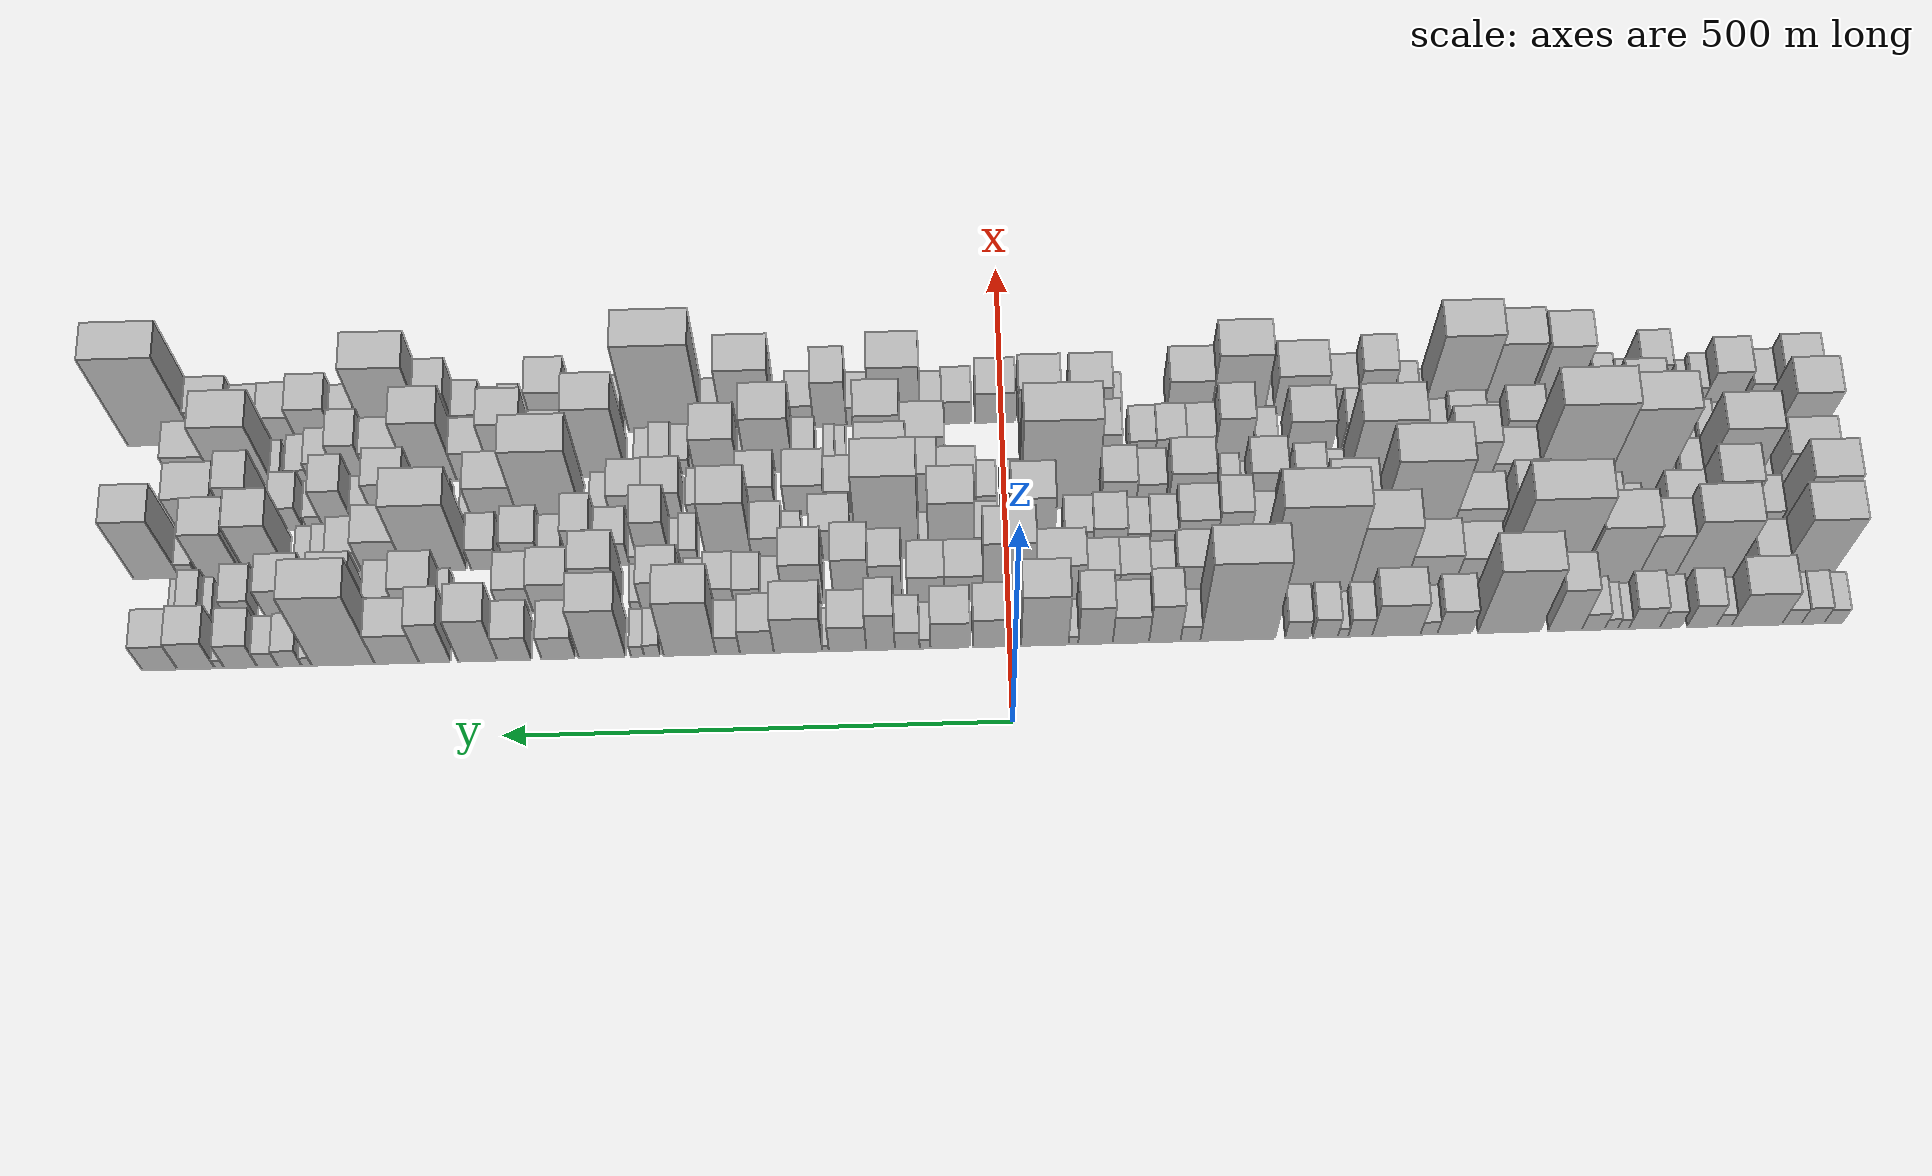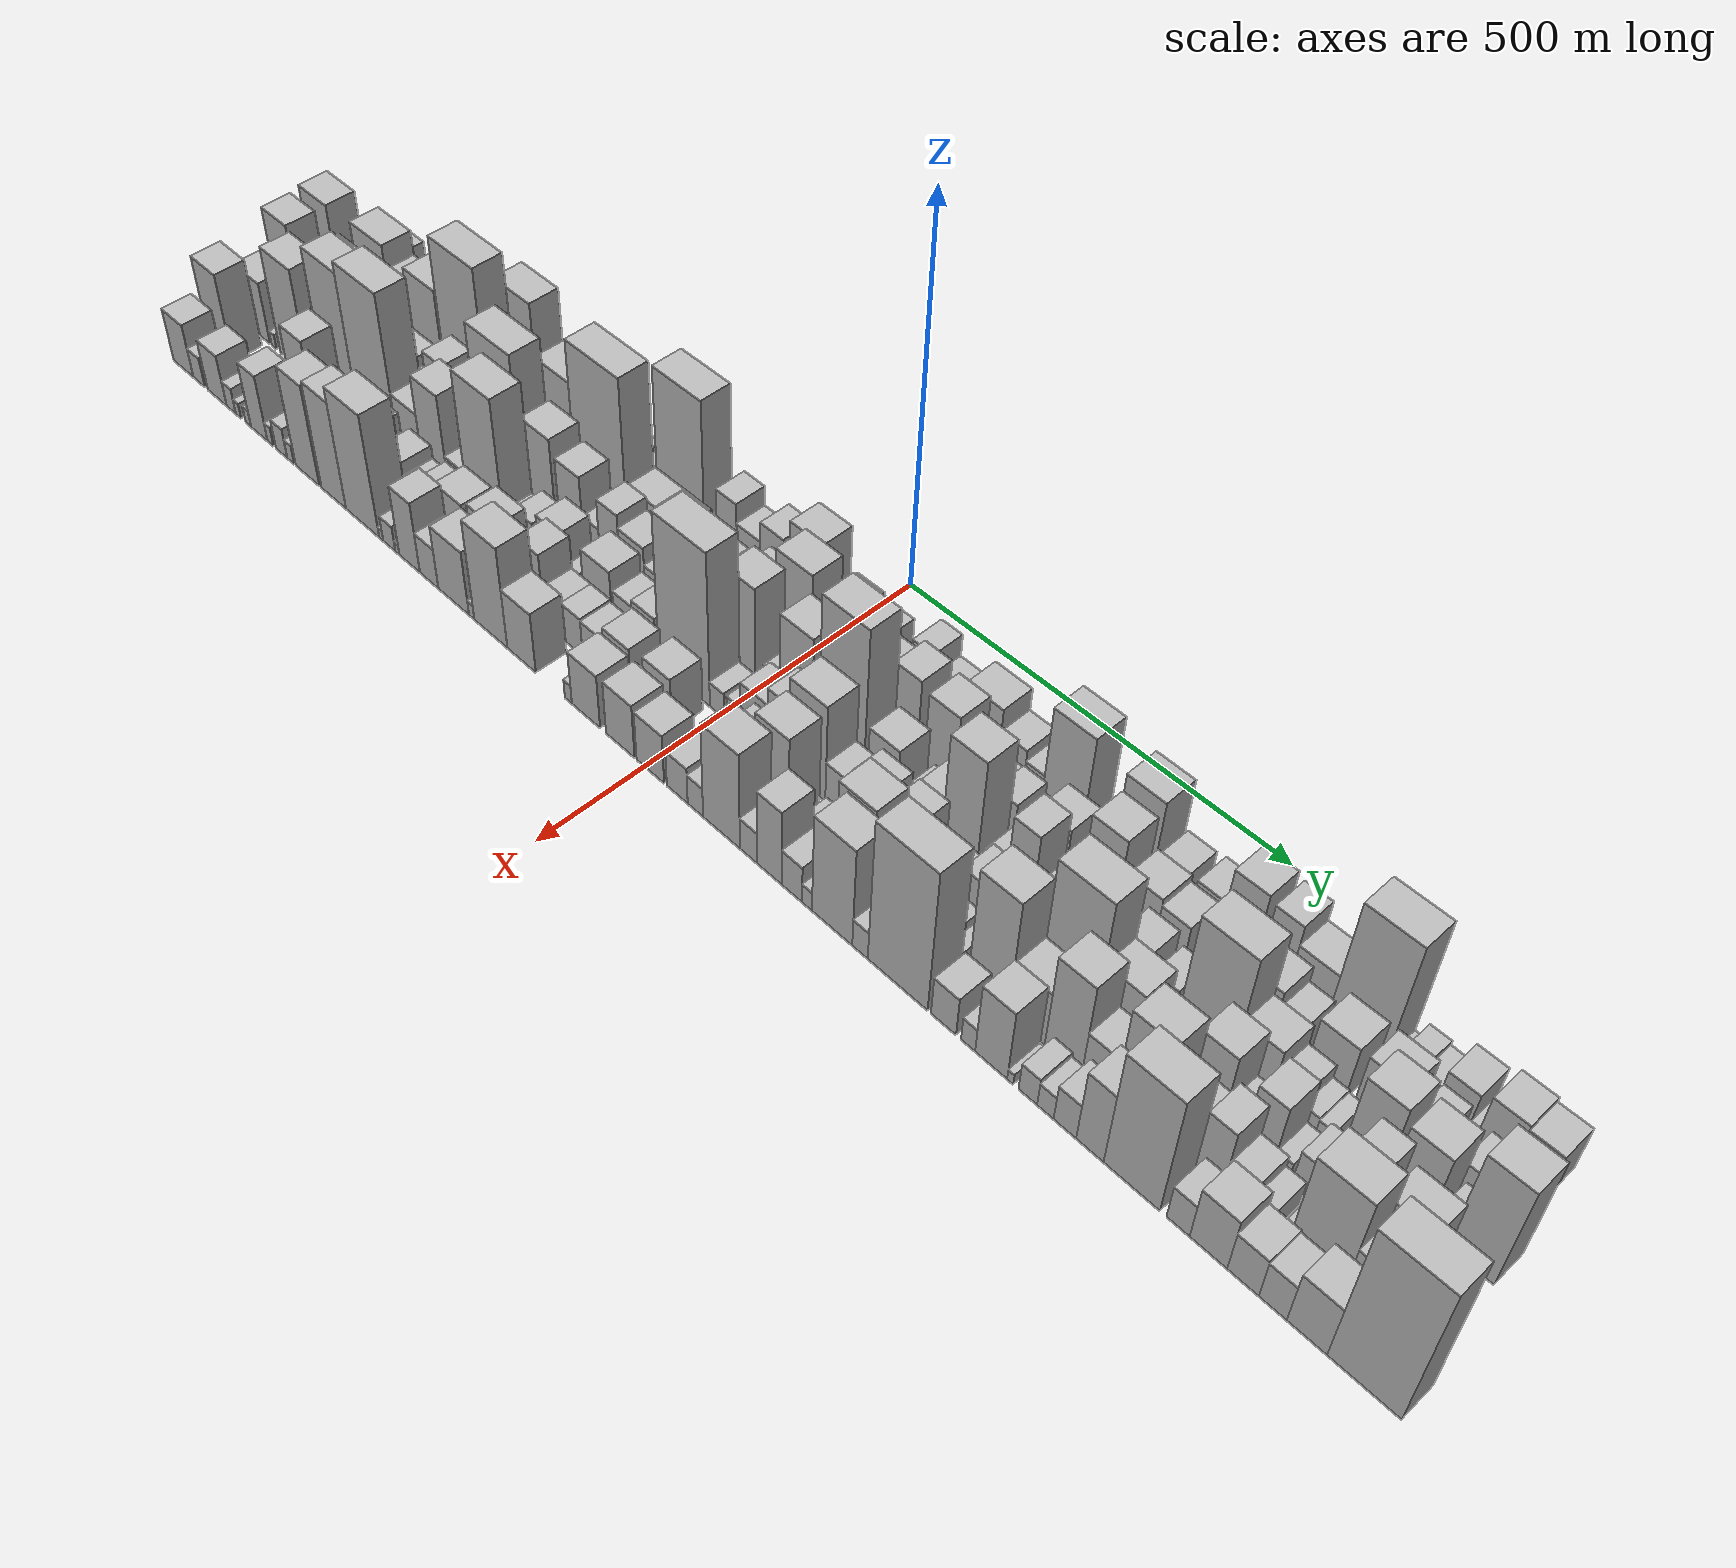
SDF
<sdf version="1.6">
 <world name="default">
  <scene>
   <sky><clouds><speed>12</speed></clouds></sky>
   <ambient>0.4 0.4 0.4 1</ambient>
   <background>0.7 0.7 0.7 1</background>
   <shadows>1</shadows>
  </scene>
  <gravity>0 0 -9.8066</gravity>
  <magnetic_field>6e-06 2.3e-05 -4.2e-05</magnetic_field>
  <physics default="0" name="default_physics" type="ode">
   <ode>
    <solver>
     <type>quick</type>
     <iters>10</iters>
     <sor>1.0</sor>
     <use_dynamic_moi_rescaling>0</use_dynamic_moi_rescaling>
    </solver>
    <constraints>
     <cfm>0</cfm>
     <erp>0.2</erp>
     <contact_max_correcting_vel>100</contact_max_correcting_vel>
     <contact_surface_layer>0.001</contact_surface_layer>
    </constraints>
   </ode>
   <max_step_size>0.004</max_step_size>
   <real_time_factor>1</real_time_factor>
   <real_time_update_rate>250</real_time_update_rate>
  </physics>
  <light name="sun" type="directional">
   <pose>0 0 10 0 0 0</pose>
   <diffuse>0.8 0.8 0.8 1</diffuse>
   <specular>0.2 0.2 0.2 1</specular>
   <attenuation>
    <range>1000</range>
    <constant>0.9</constant>
    <linear>0.01</linear>
    <quadratic>0.001</quadratic>
   </attenuation>
   <direction>-0.5 0.1 -0.9</direction>
  </light>
  <model name="building_1">
   <static>1</static>
   <pose>100.0000 -820.8194 0 0.000000 0.000000 0.000000</pose>
   <link name="link">
    <pose>0 0 18.00 0 0 0</pose>
    <collision name="collision"><geometry><box><size>40.0000 18.3613 36.0000</size></box></geometry></collision>
    <visual name="visual">
     <cast_shadows>0</cast_shadows>
     <geometry><box><size>40.0000 18.3613 36.0000</size></box></geometry>
     <material>
      <script>
       <uri>model://HANNAS_wall/materials/scripts</uri>
       <uri>model://HANNAS_wall/materials/textures</uri>
       <name>vrc/HANNAS_wall</name>
      </script>
     </material>
    </visual>
   </link>
  </model>
  <model name="building_2">
   <static>1</static>
   <pose>100.0000 -800.2883 0 0.000000 0.000000 0.000000</pose>
   <link name="link">
    <pose>0 0 21.00 0 0 0</pose>
    <collision name="collision"><geometry><box><size>40.0000 22.7009 42.0000</size></box></geometry></collision>
    <visual name="visual">
     <cast_shadows>0</cast_shadows>
     <geometry><box><size>40.0000 22.7009 42.0000</size></box></geometry>
     <material>
      <script>
       <uri>model://HANNAS_wall/materials/scripts</uri>
       <uri>model://HANNAS_wall/materials/textures</uri>
       <name>vrc/HANNAS_wall</name>
      </script>
     </material>
    </visual>
   </link>
  </model>
  <model name="building_3">
   <static>1</static>
   <pose>100.0000 -779.1160 0 0.000000 0.000000 0.000000</pose>
   <link name="link">
    <pose>0 0 19.50 0 0 0</pose>
    <collision name="collision"><geometry><box><size>40.0000 19.6437 39.0000</size></box></geometry></collision>
    <visual name="visual">
     <cast_shadows>0</cast_shadows>
     <geometry><box><size>40.0000 19.6437 39.0000</size></box></geometry>
     <material>
      <script>
       <uri>model://HANNAS_wall/materials/scripts</uri>
       <uri>model://HANNAS_wall/materials/textures</uri>
       <name>vrc/HANNAS_wall</name>
      </script>
     </material>
    </visual>
   </link>
  </model>
  <model name="building_4">
   <static>1</static>
   <pose>100.0000 -744.1241 0 0.000000 0.000000 0.000000</pose>
   <link name="link">
    <pose>0 0 42.00 0 0 0</pose>
    <collision name="collision"><geometry><box><size>40.0000 50.3401 84.0000</size></box></geometry></collision>
    <visual name="visual">
     <cast_shadows>0</cast_shadows>
     <geometry><box><size>40.0000 50.3401 84.0000</size></box></geometry>
     <material>
      <script>
       <uri>model://HANNAS_wall/materials/scripts</uri>
       <uri>model://HANNAS_wall/materials/textures</uri>
       <name>vrc/HANNAS_wall</name>
      </script>
     </material>
    </visual>
   </link>
  </model>
  <model name="building_5">
   <static>1</static>
   <pose>100.0000 -711.3848 0 0.000000 0.000000 0.000000</pose>
   <link name="link">
    <pose>0 0 15.00 0 0 0</pose>
    <collision name="collision"><geometry><box><size>40.0000 15.1385 30.0000</size></box></geometry></collision>
    <visual name="visual">
     <cast_shadows>0</cast_shadows>
     <geometry><box><size>40.0000 15.1385 30.0000</size></box></geometry>
     <material>
      <script>
       <uri>model://HANNAS_wall/materials/scripts</uri>
       <uri>model://HANNAS_wall/materials/textures</uri>
       <name>vrc/HANNAS_wall</name>
      </script>
     </material>
    </visual>
   </link>
  </model>
  <model name="building_6">
   <static>1</static>
   <pose>100.0000 -689.0686 0 0.000000 0.000000 0.000000</pose>
   <link name="link">
    <pose>0 0 28.50 0 0 0</pose>
    <collision name="collision"><geometry><box><size>40.0000 29.4938 57.0000</size></box></geometry></collision>
    <visual name="visual">
     <cast_shadows>0</cast_shadows>
     <geometry><box><size>40.0000 29.4938 57.0000</size></box></geometry>
     <material>
      <script>
       <uri>model://HANNAS_wall/materials/scripts</uri>
       <uri>model://HANNAS_wall/materials/textures</uri>
       <name>vrc/HANNAS_wall</name>
      </script>
     </material>
    </visual>
   </link>
  </model>
  <model name="building_7">
   <static>1</static>
   <pose>100.0000 -657.7556 0 0.000000 0.000000 0.000000</pose>
   <link name="link">
    <pose>0 0 21.00 0 0 0</pose>
    <collision name="collision"><geometry><box><size>40.0000 21.1322 42.0000</size></box></geometry></collision>
    <visual name="visual">
     <cast_shadows>0</cast_shadows>
     <geometry><box><size>40.0000 21.1322 42.0000</size></box></geometry>
     <material>
      <script>
       <uri>model://HANNAS_wall/materials/scripts</uri>
       <uri>model://HANNAS_wall/materials/textures</uri>
       <name>vrc/HANNAS_wall</name>
      </script>
     </material>
    </visual>
   </link>
  </model>
  <model name="building_8">
   <static>1</static>
   <pose>100.0000 -631.7947 0 0.000000 0.000000 0.000000</pose>
   <link name="link">
    <pose>0 0 27.00 0 0 0</pose>
    <collision name="collision"><geometry><box><size>40.0000 30.7895 54.0000</size></box></geometry></collision>
    <visual name="visual">
     <cast_shadows>0</cast_shadows>
     <geometry><box><size>40.0000 30.7895 54.0000</size></box></geometry>
     <material>
      <script>
       <uri>model://HANNAS_wall/materials/scripts</uri>
       <uri>model://HANNAS_wall/materials/textures</uri>
       <name>vrc/HANNAS_wall</name>
      </script>
     </material>
    </visual>
   </link>
  </model>
  <model name="building_9">
   <static>1</static>
   <pose>100.0000 -610.9002 0 0.000000 0.000000 0.000000</pose>
   <link name="link">
    <pose>0 0 12.00 0 0 0</pose>
    <collision name="collision"><geometry><box><size>40.0000 10.9995 24.0000</size></box></geometry></collision>
    <visual name="visual">
     <cast_shadows>0</cast_shadows>
     <geometry><box><size>40.0000 10.9995 24.0000</size></box></geometry>
     <material>
      <script>
       <uri>model://HANNAS_wall/materials/scripts</uri>
       <uri>model://HANNAS_wall/materials/textures</uri>
       <name>vrc/HANNAS_wall</name>
      </script>
     </material>
    </visual>
   </link>
  </model>
  <model name="building_10">
   <static>1</static>
   <pose>100.0000 -598.8212 0 0.000000 0.000000 0.000000</pose>
   <link name="link">
    <pose>0 0 13.50 0 0 0</pose>
    <collision name="collision"><geometry><box><size>40.0000 13.1584 27.0000</size></box></geometry></collision>
    <visual name="visual">
     <cast_shadows>0</cast_shadows>
     <geometry><box><size>40.0000 13.1584 27.0000</size></box></geometry>
     <material>
      <script>
       <uri>model://HANNAS_wall/materials/scripts</uri>
       <uri>model://HANNAS_wall/materials/textures</uri>
       <name>vrc/HANNAS_wall</name>
      </script>
     </material>
    </visual>
   </link>
  </model>
  <model name="building_11">
   <static>1</static>
   <pose>100.0000 -580.7037 0 0.000000 0.000000 0.000000</pose>
   <link name="link">
    <pose>0 0 21.00 0 0 0</pose>
    <collision name="collision"><geometry><box><size>40.0000 23.0767 42.0000</size></box></geometry></collision>
    <visual name="visual">
     <cast_shadows>0</cast_shadows>
     <geometry><box><size>40.0000 23.0767 42.0000</size></box></geometry>
     <material>
      <script>
       <uri>model://HANNAS_wall/materials/scripts</uri>
       <uri>model://HANNAS_wall/materials/textures</uri>
       <name>vrc/HANNAS_wall</name>
      </script>
     </material>
    </visual>
   </link>
  </model>
  <model name="building_12">
   <static>1</static>
   <pose>100.0000 -552.4752 0 0.000000 0.000000 0.000000</pose>
   <link name="link">
    <pose>0 0 54.00 0 0 0</pose>
    <collision name="collision"><geometry><box><size>40.0000 33.3803 108.0000</size></box></geometry></collision>
    <visual name="visual">
     <cast_shadows>0</cast_shadows>
     <geometry><box><size>40.0000 33.3803 108.0000</size></box></geometry>
     <material>
      <script>
       <uri>model://HANNAS_wall/materials/scripts</uri>
       <uri>model://HANNAS_wall/materials/textures</uri>
       <name>vrc/HANNAS_wall</name>
      </script>
     </material>
    </visual>
   </link>
  </model>
  <model name="building_13">
   <static>1</static>
   <pose>100.0000 -496.6385 0 0.000000 0.000000 0.000000</pose>
   <link name="link">
    <pose>0 0 81.00 0 0 0</pose>
    <collision name="collision"><geometry><box><size>40.0000 62.2931 162.0000</size></box></geometry></collision>
    <visual name="visual">
     <cast_shadows>0</cast_shadows>
     <geometry><box><size>40.0000 62.2931 162.0000</size></box></geometry>
     <material>
      <script>
       <uri>model://HANNAS_wall/materials/scripts</uri>
       <uri>model://HANNAS_wall/materials/textures</uri>
       <name>vrc/HANNAS_wall</name>
      </script>
     </material>
    </visual>
   </link>
  </model>
  <model name="building_14">
   <static>1</static>
   <pose>100.0000 -442.3028 0 0.000000 0.000000 0.000000</pose>
   <link name="link">
    <pose>0 0 30.00 0 0 0</pose>
    <collision name="collision"><geometry><box><size>40.0000 34.3782 60.0000</size></box></geometry></collision>
    <visual name="visual">
     <cast_shadows>0</cast_shadows>
     <geometry><box><size>40.0000 34.3782 60.0000</size></box></geometry>
     <material>
      <script>
       <uri>model://HANNAS_wall/materials/scripts</uri>
       <uri>model://HANNAS_wall/materials/textures</uri>
       <name>vrc/HANNAS_wall</name>
      </script>
     </material>
    </visual>
   </link>
  </model>
  <model name="building_15">
   <static>1</static>
   <pose>100.0000 -416.7286 0 0.000000 0.000000 0.000000</pose>
   <link name="link">
    <pose>0 0 16.50 0 0 0</pose>
    <collision name="collision"><geometry><box><size>40.0000 16.7703 33.0000</size></box></geometry></collision>
    <visual name="visual">
     <cast_shadows>0</cast_shadows>
     <geometry><box><size>40.0000 16.7703 33.0000</size></box></geometry>
     <material>
      <script>
       <uri>model://HANNAS_wall/materials/scripts</uri>
       <uri>model://HANNAS_wall/materials/textures</uri>
       <name>vrc/HANNAS_wall</name>
      </script>
     </material>
    </visual>
   </link>
  </model>
  <model name="building_16">
   <static>1</static>
   <pose>100.0000 -384.2721 0 0.000000 0.000000 0.000000</pose>
   <link name="link">
    <pose>0 0 40.50 0 0 0</pose>
    <collision name="collision"><geometry><box><size>40.0000 48.1426 81.0000</size></box></geometry></collision>
    <visual name="visual">
     <cast_shadows>0</cast_shadows>
     <geometry><box><size>40.0000 48.1426 81.0000</size></box></geometry>
     <material>
      <script>
       <uri>model://HANNAS_wall/materials/scripts</uri>
       <uri>model://HANNAS_wall/materials/textures</uri>
       <name>vrc/HANNAS_wall</name>
      </script>
     </material>
    </visual>
   </link>
  </model>
  <model name="building_17">
   <static>1</static>
   <pose>100.0000 -348.2777 0 0.000000 0.000000 0.000000</pose>
   <link name="link">
    <pose>0 0 22.50 0 0 0</pose>
    <collision name="collision"><geometry><box><size>40.0000 23.8463 45.0000</size></box></geometry></collision>
    <visual name="visual">
     <cast_shadows>0</cast_shadows>
     <geometry><box><size>40.0000 23.8463 45.0000</size></box></geometry>
     <material>
      <script>
       <uri>model://HANNAS_wall/materials/scripts</uri>
       <uri>model://HANNAS_wall/materials/textures</uri>
       <name>vrc/HANNAS_wall</name>
      </script>
     </material>
    </visual>
   </link>
  </model>
  <model name="building_18">
   <static>1</static>
   <pose>100.0000 -331.1946 0 0.000000 0.000000 0.000000</pose>
   <link name="link">
    <pose>0 0 10.50 0 0 0</pose>
    <collision name="collision"><geometry><box><size>40.0000 10.3200 21.0000</size></box></geometry></collision>
    <visual name="visual">
     <cast_shadows>0</cast_shadows>
     <geometry><box><size>40.0000 10.3200 21.0000</size></box></geometry>
     <material>
      <script>
       <uri>model://HANNAS_wall/materials/scripts</uri>
       <uri>model://HANNAS_wall/materials/textures</uri>
       <name>vrc/HANNAS_wall</name>
      </script>
     </material>
    </visual>
   </link>
  </model>
  <model name="building_19">
   <static>1</static>
   <pose>100.0000 -313.4795 0 0.000000 0.000000 0.000000</pose>
   <link name="link">
    <pose>0 0 24.00 0 0 0</pose>
    <collision name="collision"><geometry><box><size>40.0000 25.1102 48.0000</size></box></geometry></collision>
    <visual name="visual">
     <cast_shadows>0</cast_shadows>
     <geometry><box><size>40.0000 25.1102 48.0000</size></box></geometry>
     <material>
      <script>
       <uri>model://HANNAS_wall/materials/scripts</uri>
       <uri>model://HANNAS_wall/materials/textures</uri>
       <name>vrc/HANNAS_wall</name>
      </script>
     </material>
    </visual>
   </link>
  </model>
  <model name="building_20">
   <static>1</static>
   <pose>100.0000 -285.6841 0 0.000000 0.000000 0.000000</pose>
   <link name="link">
    <pose>0 0 22.50 0 0 0</pose>
    <collision name="collision"><geometry><box><size>40.0000 24.4805 45.0000</size></box></geometry></collision>
    <visual name="visual">
     <cast_shadows>0</cast_shadows>
     <geometry><box><size>40.0000 24.4805 45.0000</size></box></geometry>
     <material>
      <script>
       <uri>model://HANNAS_wall/materials/scripts</uri>
       <uri>model://HANNAS_wall/materials/textures</uri>
       <name>vrc/HANNAS_wall</name>
      </script>
     </material>
    </visual>
   </link>
  </model>
  <model name="building_21">
   <static>1</static>
   <pose>100.0000 -226.2490 0 0.000000 0.000000 0.000000</pose>
   <link name="link">
    <pose>0 0 100.50 0 0 0</pose>
    <collision name="collision"><geometry><box><size>40.0000 74.3897 201.0000</size></box></geometry></collision>
    <visual name="visual">
     <cast_shadows>0</cast_shadows>
     <geometry><box><size>40.0000 74.3897 201.0000</size></box></geometry>
     <material>
      <script>
       <uri>model://HANNAS_wall/materials/scripts</uri>
       <uri>model://HANNAS_wall/materials/textures</uri>
       <name>vrc/HANNAS_wall</name>
      </script>
     </material>
    </visual>
   </link>
  </model>
  <model name="building_22">
   <static>1</static>
   <pose>100.0000 -179.1868 0 0.000000 0.000000 0.000000</pose>
   <link name="link">
    <pose>0 0 19.50 0 0 0</pose>
    <collision name="collision"><geometry><box><size>40.0000 19.7347 39.0000</size></box></geometry></collision>
    <visual name="visual">
     <cast_shadows>0</cast_shadows>
     <geometry><box><size>40.0000 19.7347 39.0000</size></box></geometry>
     <material>
      <script>
       <uri>model://HANNAS_wall/materials/scripts</uri>
       <uri>model://HANNAS_wall/materials/textures</uri>
       <name>vrc/HANNAS_wall</name>
      </script>
     </material>
    </visual>
   </link>
  </model>
  <model name="building_23">
   <static>1</static>
   <pose>100.0000 -153.6673 0 0.000000 0.000000 0.000000</pose>
   <link name="link">
    <pose>0 0 48.00 0 0 0</pose>
    <collision name="collision"><geometry><box><size>40.0000 31.3043 96.0000</size></box></geometry></collision>
    <visual name="visual">
     <cast_shadows>0</cast_shadows>
     <geometry><box><size>40.0000 31.3043 96.0000</size></box></geometry>
     <material>
      <script>
       <uri>model://HANNAS_wall/materials/scripts</uri>
       <uri>model://HANNAS_wall/materials/textures</uri>
       <name>vrc/HANNAS_wall</name>
      </script>
     </material>
    </visual>
   </link>
  </model>
  <model name="building_24">
   <static>1</static>
   <pose>100.0000 -119.9857 0 0.000000 0.000000 0.000000</pose>
   <link name="link">
    <pose>0 0 34.50 0 0 0</pose>
    <collision name="collision"><geometry><box><size>40.0000 36.0590 69.0000</size></box></geometry></collision>
    <visual name="visual">
     <cast_shadows>0</cast_shadows>
     <geometry><box><size>40.0000 36.0590 69.0000</size></box></geometry>
     <material>
      <script>
       <uri>model://HANNAS_wall/materials/scripts</uri>
       <uri>model://HANNAS_wall/materials/textures</uri>
       <name>vrc/HANNAS_wall</name>
      </script>
     </material>
    </visual>
   </link>
  </model>
  <model name="building_25">
   <static>1</static>
   <pose>100.0000 -84.7607 0 0.000000 0.000000 0.000000</pose>
   <link name="link">
    <pose>0 0 48.00 0 0 0</pose>
    <collision name="collision"><geometry><box><size>40.0000 34.3909 96.0000</size></box></geometry></collision>
    <visual name="visual">
     <cast_shadows>0</cast_shadows>
     <geometry><box><size>40.0000 34.3909 96.0000</size></box></geometry>
     <material>
      <script>
       <uri>model://HANNAS_wall/materials/scripts</uri>
       <uri>model://HANNAS_wall/materials/textures</uri>
       <name>vrc/HANNAS_wall</name>
      </script>
     </material>
    </visual>
   </link>
  </model>
  <model name="building_26">
   <static>1</static>
   <pose>100.0000 -62.7450 0 0.000000 0.000000 0.000000</pose>
   <link name="link">
    <pose>0 0 10.50 0 0 0</pose>
    <collision name="collision"><geometry><box><size>40.0000 9.6406 21.0000</size></box></geometry></collision>
    <visual name="visual">
     <cast_shadows>0</cast_shadows>
     <geometry><box><size>40.0000 9.6406 21.0000</size></box></geometry>
     <material>
      <script>
       <uri>model://HANNAS_wall/materials/scripts</uri>
       <uri>model://HANNAS_wall/materials/textures</uri>
       <name>vrc/HANNAS_wall</name>
      </script>
     </material>
    </visual>
   </link>
  </model>
  <model name="building_27">
   <static>1</static>
   <pose>100.0000 -34.4189 0 0.000000 0.000000 0.000000</pose>
   <link name="link">
    <pose>0 0 64.50 0 0 0</pose>
    <collision name="collision"><geometry><box><size>40.0000 47.0114 129.0000</size></box></geometry></collision>
    <visual name="visual">
     <cast_shadows>0</cast_shadows>
     <geometry><box><size>40.0000 47.0114 129.0000</size></box></geometry>
     <material>
      <script>
       <uri>model://HANNAS_wall/materials/scripts</uri>
       <uri>model://HANNAS_wall/materials/textures</uri>
       <name>vrc/HANNAS_wall</name>
      </script>
     </material>
    </visual>
   </link>
  </model>
  <model name="building_28">
   <static>1</static>
   <pose>100.0000 18.0639 0 0.000000 0.000000 0.000000</pose>
   <link name="link">
    <pose>0 0 36.00 0 0 0</pose>
    <collision name="collision"><geometry><box><size>40.0000 37.9542 72.0000</size></box></geometry></collision>
    <visual name="visual">
     <cast_shadows>0</cast_shadows>
     <geometry><box><size>40.0000 37.9542 72.0000</size></box></geometry>
     <material>
      <script>
       <uri>model://HANNAS_wall/materials/scripts</uri>
       <uri>model://HANNAS_wall/materials/textures</uri>
       <name>vrc/HANNAS_wall</name>
      </script>
     </material>
    </visual>
   </link>
  </model>
  <model name="building_29">
   <static>1</static>
   <pose>100.0000 59.5976 0 0.000000 0.000000 0.000000</pose>
   <link name="link">
    <pose>0 0 33.00 0 0 0</pose>
    <collision name="collision"><geometry><box><size>40.0000 39.1133 66.0000</size></box></geometry></collision>
    <visual name="visual">
     <cast_shadows>0</cast_shadows>
     <geometry><box><size>40.0000 39.1133 66.0000</size></box></geometry>
     <material>
      <script>
       <uri>model://HANNAS_wall/materials/scripts</uri>
       <uri>model://HANNAS_wall/materials/textures</uri>
       <name>vrc/HANNAS_wall</name>
      </script>
     </material>
    </visual>
   </link>
  </model>
  <model name="building_30">
   <static>1</static>
   <pose>100.0000 84.5505 0 0.000000 0.000000 0.000000</pose>
   <link name="link">
    <pose>0 0 12.00 0 0 0</pose>
    <collision name="collision"><geometry><box><size>40.0000 10.7926 24.0000</size></box></geometry></collision>
    <visual name="visual">
     <cast_shadows>0</cast_shadows>
     <geometry><box><size>40.0000 10.7926 24.0000</size></box></geometry>
     <material>
      <script>
       <uri>model://HANNAS_wall/materials/scripts</uri>
       <uri>model://HANNAS_wall/materials/textures</uri>
       <name>vrc/HANNAS_wall</name>
      </script>
     </material>
    </visual>
   </link>
  </model>
  <model name="building_31">
   <static>1</static>
   <pose>100.0000 102.2200 0 0.000000 0.000000 0.000000</pose>
   <link name="link">
    <pose>0 0 22.50 0 0 0</pose>
    <collision name="collision"><geometry><box><size>40.0000 24.5463 45.0000</size></box></geometry></collision>
    <visual name="visual">
     <cast_shadows>0</cast_shadows>
     <geometry><box><size>40.0000 24.5463 45.0000</size></box></geometry>
     <material>
      <script>
       <uri>model://HANNAS_wall/materials/scripts</uri>
       <uri>model://HANNAS_wall/materials/textures</uri>
       <name>vrc/HANNAS_wall</name>
      </script>
     </material>
    </visual>
   </link>
  </model>
  <model name="building_32">
   <static>1</static>
   <pose>100.0000 128.6464 0 0.000000 0.000000 0.000000</pose>
   <link name="link">
    <pose>0 0 46.50 0 0 0</pose>
    <collision name="collision"><geometry><box><size>40.0000 28.3064 93.0000</size></box></geometry></collision>
    <visual name="visual">
     <cast_shadows>0</cast_shadows>
     <geometry><box><size>40.0000 28.3064 93.0000</size></box></geometry>
     <material>
      <script>
       <uri>model://HANNAS_wall/materials/scripts</uri>
       <uri>model://HANNAS_wall/materials/textures</uri>
       <name>vrc/HANNAS_wall</name>
      </script>
     </material>
    </visual>
   </link>
  </model>
  <model name="building_33">
   <static>1</static>
   <pose>100.0000 161.4105 0 0.000000 0.000000 0.000000</pose>
   <link name="link">
    <pose>0 0 31.50 0 0 0</pose>
    <collision name="collision"><geometry><box><size>40.0000 37.2217 63.0000</size></box></geometry></collision>
    <visual name="visual">
     <cast_shadows>0</cast_shadows>
     <geometry><box><size>40.0000 37.2217 63.0000</size></box></geometry>
     <material>
      <script>
       <uri>model://HANNAS_wall/materials/scripts</uri>
       <uri>model://HANNAS_wall/materials/textures</uri>
       <name>vrc/HANNAS_wall</name>
      </script>
     </material>
    </visual>
   </link>
  </model>
  <model name="building_34">
   <static>1</static>
   <pose>100.0000 183.2729 0 0.000000 0.000000 0.000000</pose>
   <link name="link">
    <pose>0 0 7.50 0 0 0</pose>
    <collision name="collision"><geometry><box><size>40.0000 6.5032 15.0000</size></box></geometry></collision>
    <visual name="visual">
     <cast_shadows>0</cast_shadows>
     <geometry><box><size>40.0000 6.5032 15.0000</size></box></geometry>
     <material>
      <script>
       <uri>model://HANNAS_wall/materials/scripts</uri>
       <uri>model://HANNAS_wall/materials/textures</uri>
       <name>vrc/HANNAS_wall</name>
      </script>
     </material>
    </visual>
   </link>
  </model>
  <model name="building_35">
   <static>1</static>
   <pose>100.0000 210.5609 0 0.000000 0.000000 0.000000</pose>
   <link name="link">
    <pose>0 0 45.00 0 0 0</pose>
    <collision name="collision"><geometry><box><size>40.0000 48.0727 90.0000</size></box></geometry></collision>
    <visual name="visual">
     <cast_shadows>0</cast_shadows>
     <geometry><box><size>40.0000 48.0727 90.0000</size></box></geometry>
     <material>
      <script>
       <uri>model://HANNAS_wall/materials/scripts</uri>
       <uri>model://HANNAS_wall/materials/textures</uri>
       <name>vrc/HANNAS_wall</name>
      </script>
     </material>
    </visual>
   </link>
  </model>
  <model name="building_36">
   <static>1</static>
   <pose>100.0000 251.3579 0 0.000000 0.000000 0.000000</pose>
   <link name="link">
    <pose>0 0 30.00 0 0 0</pose>
    <collision name="collision"><geometry><box><size>40.0000 33.5214 60.0000</size></box></geometry></collision>
    <visual name="visual">
     <cast_shadows>0</cast_shadows>
     <geometry><box><size>40.0000 33.5214 60.0000</size></box></geometry>
     <material>
      <script>
       <uri>model://HANNAS_wall/materials/scripts</uri>
       <uri>model://HANNAS_wall/materials/textures</uri>
       <name>vrc/HANNAS_wall</name>
      </script>
     </material>
    </visual>
   </link>
  </model>
  <model name="building_37">
   <static>1</static>
   <pose>100.0000 279.9803 0 0.000000 0.000000 0.000000</pose>
   <link name="link">
    <pose>0 0 22.50 0 0 0</pose>
    <collision name="collision"><geometry><box><size>40.0000 23.7235 45.0000</size></box></geometry></collision>
    <visual name="visual">
     <cast_shadows>0</cast_shadows>
     <geometry><box><size>40.0000 23.7235 45.0000</size></box></geometry>
     <material>
      <script>
       <uri>model://HANNAS_wall/materials/scripts</uri>
       <uri>model://HANNAS_wall/materials/textures</uri>
       <name>vrc/HANNAS_wall</name>
      </script>
     </material>
    </visual>
   </link>
  </model>
  <model name="building_38">
   <static>1</static>
   <pose>100.0000 317.8048 0 0.000000 0.000000 0.000000</pose>
   <link name="link">
    <pose>0 0 70.50 0 0 0</pose>
    <collision name="collision"><geometry><box><size>40.0000 51.9255 141.0000</size></box></geometry></collision>
    <visual name="visual">
     <cast_shadows>0</cast_shadows>
     <geometry><box><size>40.0000 51.9255 141.0000</size></box></geometry>
     <material>
      <script>
       <uri>model://HANNAS_wall/materials/scripts</uri>
       <uri>model://HANNAS_wall/materials/textures</uri>
       <name>vrc/HANNAS_wall</name>
      </script>
     </material>
    </visual>
   </link>
  </model>
  <model name="building_39">
   <static>1</static>
   <pose>100.0000 354.8430 0 0.000000 0.000000 0.000000</pose>
   <link name="link">
    <pose>0 0 15.00 0 0 0</pose>
    <collision name="collision"><geometry><box><size>40.0000 16.1508 30.0000</size></box></geometry></collision>
    <visual name="visual">
     <cast_shadows>0</cast_shadows>
     <geometry><box><size>40.0000 16.1508 30.0000</size></box></geometry>
     <material>
      <script>
       <uri>model://HANNAS_wall/materials/scripts</uri>
       <uri>model://HANNAS_wall/materials/textures</uri>
       <name>vrc/HANNAS_wall</name>
      </script>
     </material>
    </visual>
   </link>
  </model>
  <model name="building_40">
   <static>1</static>
   <pose>100.0000 369.5333 0 0.000000 0.000000 0.000000</pose>
   <link name="link">
    <pose>0 0 13.50 0 0 0</pose>
    <collision name="collision"><geometry><box><size>40.0000 13.2298 27.0000</size></box></geometry></collision>
    <visual name="visual">
     <cast_shadows>0</cast_shadows>
     <geometry><box><size>40.0000 13.2298 27.0000</size></box></geometry>
     <material>
      <script>
       <uri>model://HANNAS_wall/materials/scripts</uri>
       <uri>model://HANNAS_wall/materials/textures</uri>
       <name>vrc/HANNAS_wall</name>
      </script>
     </material>
    </visual>
   </link>
  </model>
  <model name="building_41">
   <static>1</static>
   <pose>100.0000 404.4747 0 0.000000 0.000000 0.000000</pose>
   <link name="link">
    <pose>0 0 63.00 0 0 0</pose>
    <collision name="collision"><geometry><box><size>40.0000 46.6530 126.0000</size></box></geometry></collision>
    <visual name="visual">
     <cast_shadows>0</cast_shadows>
     <geometry><box><size>40.0000 46.6530 126.0000</size></box></geometry>
     <material>
      <script>
       <uri>model://HANNAS_wall/materials/scripts</uri>
       <uri>model://HANNAS_wall/materials/textures</uri>
       <name>vrc/HANNAS_wall</name>
      </script>
     </material>
    </visual>
   </link>
  </model>
  <model name="building_42">
   <static>1</static>
   <pose>100.0000 447.7379 0 0.000000 0.000000 0.000000</pose>
   <link name="link">
    <pose>0 0 28.50 0 0 0</pose>
    <collision name="collision"><geometry><box><size>40.0000 33.8734 57.0000</size></box></geometry></collision>
    <visual name="visual">
     <cast_shadows>0</cast_shadows>
     <geometry><box><size>40.0000 33.8734 57.0000</size></box></geometry>
     <material>
      <script>
       <uri>model://HANNAS_wall/materials/scripts</uri>
       <uri>model://HANNAS_wall/materials/textures</uri>
       <name>vrc/HANNAS_wall</name>
      </script>
     </material>
    </visual>
   </link>
  </model>
  <model name="building_43">
   <static>1</static>
   <pose>100.0000 491.4651 0 0.000000 0.000000 0.000000</pose>
   <link name="link">
    <pose>0 0 30.00 0 0 0</pose>
    <collision name="collision"><geometry><box><size>40.0000 33.5811 60.0000</size></box></geometry></collision>
    <visual name="visual">
     <cast_shadows>0</cast_shadows>
     <geometry><box><size>40.0000 33.5811 60.0000</size></box></geometry>
     <material>
      <script>
       <uri>model://HANNAS_wall/materials/scripts</uri>
       <uri>model://HANNAS_wall/materials/textures</uri>
       <name>vrc/HANNAS_wall</name>
      </script>
     </material>
    </visual>
   </link>
  </model>
  <model name="building_44">
   <static>1</static>
   <pose>100.0000 527.8401 0 0.000000 0.000000 0.000000</pose>
   <link name="link">
    <pose>0 0 54.00 0 0 0</pose>
    <collision name="collision"><geometry><box><size>40.0000 39.1689 108.0000</size></box></geometry></collision>
    <visual name="visual">
     <cast_shadows>0</cast_shadows>
     <geometry><box><size>40.0000 39.1689 108.0000</size></box></geometry>
     <material>
      <script>
       <uri>model://HANNAS_wall/materials/scripts</uri>
       <uri>model://HANNAS_wall/materials/textures</uri>
       <name>vrc/HANNAS_wall</name>
      </script>
     </material>
    </visual>
   </link>
  </model>
  <model name="building_45">
   <static>1</static>
   <pose>100.0000 570.1736 0 0.000000 0.000000 0.000000</pose>
   <link name="link">
    <pose>0 0 51.00 0 0 0</pose>
    <collision name="collision"><geometry><box><size>40.0000 31.4981 102.0000</size></box></geometry></collision>
    <visual name="visual">
     <cast_shadows>0</cast_shadows>
     <geometry><box><size>40.0000 31.4981 102.0000</size></box></geometry>
     <material>
      <script>
       <uri>model://HANNAS_wall/materials/scripts</uri>
       <uri>model://HANNAS_wall/materials/textures</uri>
       <name>vrc/HANNAS_wall</name>
      </script>
     </material>
    </visual>
   </link>
  </model>
  <model name="building_46">
   <static>1</static>
   <pose>100.0000 607.7697 0 0.000000 0.000000 0.000000</pose>
   <link name="link">
    <pose>0 0 37.50 0 0 0</pose>
    <collision name="collision"><geometry><box><size>40.0000 43.6942 75.0000</size></box></geometry></collision>
    <visual name="visual">
     <cast_shadows>0</cast_shadows>
     <geometry><box><size>40.0000 43.6942 75.0000</size></box></geometry>
     <material>
      <script>
       <uri>model://HANNAS_wall/materials/scripts</uri>
       <uri>model://HANNAS_wall/materials/textures</uri>
       <name>vrc/HANNAS_wall</name>
      </script>
     </material>
    </visual>
   </link>
  </model>
  <model name="building_47">
   <static>1</static>
   <pose>100.0000 660.7658 0 0.000000 0.000000 0.000000</pose>
   <link name="link">
    <pose>0 0 90.00 0 0 0</pose>
    <collision name="collision"><geometry><box><size>40.0000 62.2980 180.0000</size></box></geometry></collision>
    <visual name="visual">
     <cast_shadows>0</cast_shadows>
     <geometry><box><size>40.0000 62.2980 180.0000</size></box></geometry>
     <material>
      <script>
       <uri>model://HANNAS_wall/materials/scripts</uri>
       <uri>model://HANNAS_wall/materials/textures</uri>
       <name>vrc/HANNAS_wall</name>
      </script>
     </material>
    </visual>
   </link>
  </model>
  <model name="building_48">
   <static>1</static>
   <pose>100.0000 696.9448 0 0.000000 0.000000 0.000000</pose>
   <link name="link">
    <pose>0 0 10.50 0 0 0</pose>
    <collision name="collision"><geometry><box><size>40.0000 10.0598 21.0000</size></box></geometry></collision>
    <visual name="visual">
     <cast_shadows>0</cast_shadows>
     <geometry><box><size>40.0000 10.0598 21.0000</size></box></geometry>
     <material>
      <script>
       <uri>model://HANNAS_wall/materials/scripts</uri>
       <uri>model://HANNAS_wall/materials/textures</uri>
       <name>vrc/HANNAS_wall</name>
      </script>
     </material>
    </visual>
   </link>
  </model>
  <model name="building_49">
   <static>1</static>
   <pose>100.0000 713.6967 0 0.000000 0.000000 0.000000</pose>
   <link name="link">
    <pose>0 0 21.00 0 0 0</pose>
    <collision name="collision"><geometry><box><size>40.0000 23.4441 42.0000</size></box></geometry></collision>
    <visual name="visual">
     <cast_shadows>0</cast_shadows>
     <geometry><box><size>40.0000 23.4441 42.0000</size></box></geometry>
     <material>
      <script>
       <uri>model://HANNAS_wall/materials/scripts</uri>
       <uri>model://HANNAS_wall/materials/textures</uri>
       <name>vrc/HANNAS_wall</name>
      </script>
     </material>
    </visual>
   </link>
  </model>
  <model name="building_50">
   <static>1</static>
   <pose>100.0000 735.4919 0 0.000000 0.000000 0.000000</pose>
   <link name="link">
    <pose>0 0 18.00 0 0 0</pose>
    <collision name="collision"><geometry><box><size>40.0000 20.1462 36.0000</size></box></geometry></collision>
    <visual name="visual">
     <cast_shadows>0</cast_shadows>
     <geometry><box><size>40.0000 20.1462 36.0000</size></box></geometry>
     <material>
      <script>
       <uri>model://HANNAS_wall/materials/scripts</uri>
       <uri>model://HANNAS_wall/materials/textures</uri>
       <name>vrc/HANNAS_wall</name>
      </script>
     </material>
    </visual>
   </link>
  </model>
  <model name="building_51">
   <static>1</static>
   <pose>100.0000 761.9363 0 0.000000 0.000000 0.000000</pose>
   <link name="link">
    <pose>0 0 30.00 0 0 0</pose>
    <collision name="collision"><geometry><box><size>40.0000 32.7426 60.0000</size></box></geometry></collision>
    <visual name="visual">
     <cast_shadows>0</cast_shadows>
     <geometry><box><size>40.0000 32.7426 60.0000</size></box></geometry>
     <material>
      <script>
       <uri>model://HANNAS_wall/materials/scripts</uri>
       <uri>model://HANNAS_wall/materials/textures</uri>
       <name>vrc/HANNAS_wall</name>
      </script>
     </material>
    </visual>
   </link>
  </model>
  <model name="building_52">
   <static>1</static>
   <pose>100.0000 782.8696 0 0.000000 0.000000 0.000000</pose>
   <link name="link">
    <pose>0 0 10.50 0 0 0</pose>
    <collision name="collision"><geometry><box><size>40.0000 9.1240 21.0000</size></box></geometry></collision>
    <visual name="visual">
     <cast_shadows>0</cast_shadows>
     <geometry><box><size>40.0000 9.1240 21.0000</size></box></geometry>
     <material>
      <script>
       <uri>model://HANNAS_wall/materials/scripts</uri>
       <uri>model://HANNAS_wall/materials/textures</uri>
       <name>vrc/HANNAS_wall</name>
      </script>
     </material>
    </visual>
   </link>
  </model>
  <model name="building_53">
   <static>1</static>
   <pose>100.0000 805.9386 0 0.000000 0.000000 0.000000</pose>
   <link name="link">
    <pose>0 0 34.50 0 0 0</pose>
    <collision name="collision"><geometry><box><size>40.0000 37.0140 69.0000</size></box></geometry></collision>
    <visual name="visual">
     <cast_shadows>0</cast_shadows>
     <geometry><box><size>40.0000 37.0140 69.0000</size></box></geometry>
     <material>
      <script>
       <uri>model://HANNAS_wall/materials/scripts</uri>
       <uri>model://HANNAS_wall/materials/textures</uri>
       <name>vrc/HANNAS_wall</name>
      </script>
     </material>
    </visual>
   </link>
  </model>
  <model name="building_54">
   <static>1</static>
   <pose>100.0000 841.8840 0 0.000000 0.000000 0.000000</pose>
   <link name="link">
    <pose>0 0 31.50 0 0 0</pose>
    <collision name="collision"><geometry><box><size>40.0000 34.8770 63.0000</size></box></geometry></collision>
    <visual name="visual">
     <cast_shadows>0</cast_shadows>
     <geometry><box><size>40.0000 34.8770 63.0000</size></box></geometry>
     <material>
      <script>
       <uri>model://HANNAS_wall/materials/scripts</uri>
       <uri>model://HANNAS_wall/materials/textures</uri>
       <name>vrc/HANNAS_wall</name>
      </script>
     </material>
    </visual>
   </link>
  </model>
  <model name="building_55">
   <static>1</static>
   <pose>149.0000 -798.3148 0 0.000000 0.000000 0.000000</pose>
   <link name="link">
    <pose>0 0 75.00 0 0 0</pose>
    <collision name="collision"><geometry><box><size>40.0000 53.3705 150.0000</size></box></geometry></collision>
    <visual name="visual">
     <cast_shadows>0</cast_shadows>
     <geometry><box><size>40.0000 53.3705 150.0000</size></box></geometry>
     <material>
      <script>
       <uri>model://HANNAS_wall/materials/scripts</uri>
       <uri>model://HANNAS_wall/materials/textures</uri>
       <name>vrc/HANNAS_wall</name>
      </script>
     </material>
    </visual>
   </link>
  </model>
  <model name="building_56">
   <static>1</static>
   <pose>149.0000 -755.5750 0 0.000000 0.000000 0.000000</pose>
   <link name="link">
    <pose>0 0 30.00 0 0 0</pose>
    <collision name="collision"><geometry><box><size>40.0000 32.1091 60.0000</size></box></geometry></collision>
    <visual name="visual">
     <cast_shadows>0</cast_shadows>
     <geometry><box><size>40.0000 32.1091 60.0000</size></box></geometry>
     <material>
      <script>
       <uri>model://HANNAS_wall/materials/scripts</uri>
       <uri>model://HANNAS_wall/materials/textures</uri>
       <name>vrc/HANNAS_wall</name>
      </script>
     </material>
    </visual>
   </link>
  </model>
  <model name="building_57">
   <static>1</static>
   <pose>149.0000 -730.8483 0 0.000000 0.000000 0.000000</pose>
   <link name="link">
    <pose>0 0 12.00 0 0 0</pose>
    <collision name="collision"><geometry><box><size>40.0000 11.3441 24.0000</size></box></geometry></collision>
    <visual name="visual">
     <cast_shadows>0</cast_shadows>
     <geometry><box><size>40.0000 11.3441 24.0000</size></box></geometry>
     <material>
      <script>
       <uri>model://HANNAS_wall/materials/scripts</uri>
       <uri>model://HANNAS_wall/materials/textures</uri>
       <name>vrc/HANNAS_wall</name>
      </script>
     </material>
    </visual>
   </link>
  </model>
  <model name="building_58">
   <static>1</static>
   <pose>149.0000 -695.2119 0 0.000000 0.000000 0.000000</pose>
   <link name="link">
    <pose>0 0 76.50 0 0 0</pose>
    <collision name="collision"><geometry><box><size>40.0000 59.9288 153.0000</size></box></geometry></collision>
    <visual name="visual">
     <cast_shadows>0</cast_shadows>
     <geometry><box><size>40.0000 59.9288 153.0000</size></box></geometry>
     <material>
      <script>
       <uri>model://HANNAS_wall/materials/scripts</uri>
       <uri>model://HANNAS_wall/materials/textures</uri>
       <name>vrc/HANNAS_wall</name>
      </script>
     </material>
    </visual>
   </link>
  </model>
  <model name="building_59">
   <static>1</static>
   <pose>149.0000 -646.7721 0 0.000000 0.000000 0.000000</pose>
   <link name="link">
    <pose>0 0 60.00 0 0 0</pose>
    <collision name="collision"><geometry><box><size>40.0000 36.9507 120.0000</size></box></geometry></collision>
    <visual name="visual">
     <cast_shadows>0</cast_shadows>
     <geometry><box><size>40.0000 36.9507 120.0000</size></box></geometry>
     <material>
      <script>
       <uri>model://HANNAS_wall/materials/scripts</uri>
       <uri>model://HANNAS_wall/materials/textures</uri>
       <name>vrc/HANNAS_wall</name>
      </script>
     </material>
    </visual>
   </link>
  </model>
  <model name="building_60">
   <static>1</static>
   <pose>149.0000 -600.3379 0 0.000000 0.000000 0.000000</pose>
   <link name="link">
    <pose>0 0 72.00 0 0 0</pose>
    <collision name="collision"><geometry><box><size>40.0000 55.9176 144.0000</size></box></geometry></collision>
    <visual name="visual">
     <cast_shadows>0</cast_shadows>
     <geometry><box><size>40.0000 55.9176 144.0000</size></box></geometry>
     <material>
      <script>
       <uri>model://HANNAS_wall/materials/scripts</uri>
       <uri>model://HANNAS_wall/materials/textures</uri>
       <name>vrc/HANNAS_wall</name>
      </script>
     </material>
    </visual>
   </link>
  </model>
  <model name="building_61">
   <static>1</static>
   <pose>149.0000 -530.8320 0 0.000000 0.000000 0.000000</pose>
   <link name="link">
    <pose>0 0 109.50 0 0 0</pose>
    <collision name="collision"><geometry><box><size>40.0000 77.0943 219.0000</size></box></geometry></collision>
    <visual name="visual">
     <cast_shadows>0</cast_shadows>
     <geometry><box><size>40.0000 77.0943 219.0000</size></box></geometry>
     <material>
      <script>
       <uri>model://HANNAS_wall/materials/scripts</uri>
       <uri>model://HANNAS_wall/materials/textures</uri>
       <name>vrc/HANNAS_wall</name>
      </script>
     </material>
    </visual>
   </link>
  </model>
  <model name="building_62">
   <static>1</static>
   <pose>149.0000 -466.6032 0 0.000000 0.000000 0.000000</pose>
   <link name="link">
    <pose>0 0 37.50 0 0 0</pose>
    <collision name="collision"><geometry><box><size>40.0000 41.3634 75.0000</size></box></geometry></collision>
    <visual name="visual">
     <cast_shadows>0</cast_shadows>
     <geometry><box><size>40.0000 41.3634 75.0000</size></box></geometry>
     <material>
      <script>
       <uri>model://HANNAS_wall/materials/scripts</uri>
       <uri>model://HANNAS_wall/materials/textures</uri>
       <name>vrc/HANNAS_wall</name>
      </script>
     </material>
    </visual>
   </link>
  </model>
  <model name="building_63">
   <static>1</static>
   <pose>149.0000 -421.0508 0 0.000000 0.000000 0.000000</pose>
   <link name="link">
    <pose>0 0 42.00 0 0 0</pose>
    <collision name="collision"><geometry><box><size>40.0000 49.7414 84.0000</size></box></geometry></collision>
    <visual name="visual">
     <cast_shadows>0</cast_shadows>
     <geometry><box><size>40.0000 49.7414 84.0000</size></box></geometry>
     <material>
      <script>
       <uri>model://HANNAS_wall/materials/scripts</uri>
       <uri>model://HANNAS_wall/materials/textures</uri>
       <name>vrc/HANNAS_wall</name>
      </script>
     </material>
    </visual>
   </link>
  </model>
  <model name="building_64">
   <static>1</static>
   <pose>149.0000 -368.4921 0 0.000000 0.000000 0.000000</pose>
   <link name="link">
    <pose>0 0 79.50 0 0 0</pose>
    <collision name="collision"><geometry><box><size>40.0000 55.3758 159.0000</size></box></geometry></collision>
    <visual name="visual">
     <cast_shadows>0</cast_shadows>
     <geometry><box><size>40.0000 55.3758 159.0000</size></box></geometry>
     <material>
      <script>
       <uri>model://HANNAS_wall/materials/scripts</uri>
       <uri>model://HANNAS_wall/materials/textures</uri>
       <name>vrc/HANNAS_wall</name>
      </script>
     </material>
    </visual>
   </link>
  </model>
  <model name="building_65">
   <static>1</static>
   <pose>149.0000 -298.9910 0 0.000000 0.000000 0.000000</pose>
   <link name="link">
    <pose>0 0 108.00 0 0 0</pose>
    <collision name="collision"><geometry><box><size>40.0000 83.6264 216.0000</size></box></geometry></collision>
    <visual name="visual">
     <cast_shadows>0</cast_shadows>
     <geometry><box><size>40.0000 83.6264 216.0000</size></box></geometry>
     <material>
      <script>
       <uri>model://HANNAS_wall/materials/scripts</uri>
       <uri>model://HANNAS_wall/materials/textures</uri>
       <name>vrc/HANNAS_wall</name>
      </script>
     </material>
    </visual>
   </link>
  </model>
  <model name="building_66">
   <static>1</static>
   <pose>149.0000 -230.9438 0 0.000000 0.000000 0.000000</pose>
   <link name="link">
    <pose>0 0 37.50 0 0 0</pose>
    <collision name="collision"><geometry><box><size>40.0000 44.4682 75.0000</size></box></geometry></collision>
    <visual name="visual">
     <cast_shadows>0</cast_shadows>
     <geometry><box><size>40.0000 44.4682 75.0000</size></box></geometry>
     <material>
      <script>
       <uri>model://HANNAS_wall/materials/scripts</uri>
       <uri>model://HANNAS_wall/materials/textures</uri>
       <name>vrc/HANNAS_wall</name>
      </script>
     </material>
    </visual>
   </link>
  </model>
  <model name="building_67">
   <static>1</static>
   <pose>149.0000 -187.2051 0 0.000000 0.000000 0.000000</pose>
   <link name="link">
    <pose>0 0 37.50 0 0 0</pose>
    <collision name="collision"><geometry><box><size>40.0000 43.0090 75.0000</size></box></geometry></collision>
    <visual name="visual">
     <cast_shadows>0</cast_shadows>
     <geometry><box><size>40.0000 43.0090 75.0000</size></box></geometry>
     <material>
      <script>
       <uri>model://HANNAS_wall/materials/scripts</uri>
       <uri>model://HANNAS_wall/materials/textures</uri>
       <name>vrc/HANNAS_wall</name>
      </script>
     </material>
    </visual>
   </link>
  </model>
  <model name="building_68">
   <static>1</static>
   <pose>149.0000 -153.0070 0 0.000000 0.000000 0.000000</pose>
   <link name="link">
    <pose>0 0 24.00 0 0 0</pose>
    <collision name="collision"><geometry><box><size>40.0000 25.3873 48.0000</size></box></geometry></collision>
    <visual name="visual">
     <cast_shadows>0</cast_shadows>
     <geometry><box><size>40.0000 25.3873 48.0000</size></box></geometry>
     <material>
      <script>
       <uri>model://HANNAS_wall/materials/scripts</uri>
       <uri>model://HANNAS_wall/materials/textures</uri>
       <name>vrc/HANNAS_wall</name>
      </script>
     </material>
    </visual>
   </link>
  </model>
  <model name="building_69">
   <static>1</static>
   <pose>149.0000 -125.1310 0 0.000000 0.000000 0.000000</pose>
   <link name="link">
    <pose>0 0 30.00 0 0 0</pose>
    <collision name="collision"><geometry><box><size>40.0000 30.3646 60.0000</size></box></geometry></collision>
    <visual name="visual">
     <cast_shadows>0</cast_shadows>
     <geometry><box><size>40.0000 30.3646 60.0000</size></box></geometry>
     <material>
      <script>
       <uri>model://HANNAS_wall/materials/scripts</uri>
       <uri>model://HANNAS_wall/materials/textures</uri>
       <name>vrc/HANNAS_wall</name>
      </script>
     </material>
    </visual>
   </link>
  </model>
  <model name="building_70">
   <static>1</static>
   <pose>149.0000 -93.2545 0 0.000000 0.000000 0.000000</pose>
   <link name="link">
    <pose>0 0 30.00 0 0 0</pose>
    <collision name="collision"><geometry><box><size>40.0000 33.3884 60.0000</size></box></geometry></collision>
    <visual name="visual">
     <cast_shadows>0</cast_shadows>
     <geometry><box><size>40.0000 33.3884 60.0000</size></box></geometry>
     <material>
      <script>
       <uri>model://HANNAS_wall/materials/scripts</uri>
       <uri>model://HANNAS_wall/materials/textures</uri>
       <name>vrc/HANNAS_wall</name>
      </script>
     </material>
    </visual>
   </link>
  </model>
  <model name="building_71">
   <static>1</static>
   <pose>149.0000 -51.3370 0 0.000000 0.000000 0.000000</pose>
   <link name="link">
    <pose>0 0 43.50 0 0 0</pose>
    <collision name="collision"><geometry><box><size>40.0000 50.4467 87.0000</size></box></geometry></collision>
    <visual name="visual">
     <cast_shadows>0</cast_shadows>
     <geometry><box><size>40.0000 50.4467 87.0000</size></box></geometry>
     <material>
      <script>
       <uri>model://HANNAS_wall/materials/scripts</uri>
       <uri>model://HANNAS_wall/materials/textures</uri>
       <name>vrc/HANNAS_wall</name>
      </script>
     </material>
    </visual>
   </link>
  </model>
  <model name="building_72">
   <static>1</static>
   <pose>149.0000 -0.3029 0 0.000000 0.000000 0.000000</pose>
   <link name="link">
    <pose>0 0 73.50 0 0 0</pose>
    <collision name="collision"><geometry><box><size>40.0000 51.6215 147.0000</size></box></geometry></collision>
    <visual name="visual">
     <cast_shadows>0</cast_shadows>
     <geometry><box><size>40.0000 51.6215 147.0000</size></box></geometry>
     <material>
      <script>
       <uri>model://HANNAS_wall/materials/scripts</uri>
       <uri>model://HANNAS_wall/materials/textures</uri>
       <name>vrc/HANNAS_wall</name>
      </script>
     </material>
    </visual>
   </link>
  </model>
  <model name="building_73">
   <static>1</static>
   <pose>149.0000 44.7026 0 0.000000 0.000000 0.000000</pose>
   <link name="link">
    <pose>0 0 33.00 0 0 0</pose>
    <collision name="collision"><geometry><box><size>40.0000 38.3895 66.0000</size></box></geometry></collision>
    <visual name="visual">
     <cast_shadows>0</cast_shadows>
     <geometry><box><size>40.0000 38.3895 66.0000</size></box></geometry>
     <material>
      <script>
       <uri>model://HANNAS_wall/materials/scripts</uri>
       <uri>model://HANNAS_wall/materials/textures</uri>
       <name>vrc/HANNAS_wall</name>
      </script>
     </material>
    </visual>
   </link>
  </model>
  <model name="building_74">
   <static>1</static>
   <pose>149.0000 82.3184 0 0.000000 0.000000 0.000000</pose>
   <link name="link">
    <pose>0 0 33.00 0 0 0</pose>
    <collision name="collision"><geometry><box><size>40.0000 36.8420 66.0000</size></box></geometry></collision>
    <visual name="visual">
     <cast_shadows>0</cast_shadows>
     <geometry><box><size>40.0000 36.8420 66.0000</size></box></geometry>
     <material>
      <script>
       <uri>model://HANNAS_wall/materials/scripts</uri>
       <uri>model://HANNAS_wall/materials/textures</uri>
       <name>vrc/HANNAS_wall</name>
      </script>
     </material>
    </visual>
   </link>
  </model>
  <model name="building_75">
   <static>1</static>
   <pose>149.0000 122.0918 0 0.000000 0.000000 0.000000</pose>
   <link name="link">
    <pose>0 0 49.50 0 0 0</pose>
    <collision name="collision"><geometry><box><size>40.0000 32.7048 99.0000</size></box></geometry></collision>
    <visual name="visual">
     <cast_shadows>0</cast_shadows>
     <geometry><box><size>40.0000 32.7048 99.0000</size></box></geometry>
     <material>
      <script>
       <uri>model://HANNAS_wall/materials/scripts</uri>
       <uri>model://HANNAS_wall/materials/textures</uri>
       <name>vrc/HANNAS_wall</name>
      </script>
     </material>
    </visual>
   </link>
  </model>
  <model name="building_76">
   <static>1</static>
   <pose>149.0000 156.2062 0 0.000000 0.000000 0.000000</pose>
   <link name="link">
    <pose>0 0 58.50 0 0 0</pose>
    <collision name="collision"><geometry><box><size>40.0000 35.5240 117.0000</size></box></geometry></collision>
    <visual name="visual">
     <cast_shadows>0</cast_shadows>
     <geometry><box><size>40.0000 35.5240 117.0000</size></box></geometry>
     <material>
      <script>
       <uri>model://HANNAS_wall/materials/scripts</uri>
       <uri>model://HANNAS_wall/materials/textures</uri>
       <name>vrc/HANNAS_wall</name>
      </script>
     </material>
    </visual>
   </link>
  </model>
  <model name="building_77">
   <static>1</static>
   <pose>149.0000 204.3954 0 0.000000 0.000000 0.000000</pose>
   <link name="link">
    <pose>0 0 54.00 0 0 0</pose>
    <collision name="collision"><geometry><box><size>40.0000 40.8544 108.0000</size></box></geometry></collision>
    <visual name="visual">
     <cast_shadows>0</cast_shadows>
     <geometry><box><size>40.0000 40.8544 108.0000</size></box></geometry>
     <material>
      <script>
       <uri>model://HANNAS_wall/materials/scripts</uri>
       <uri>model://HANNAS_wall/materials/textures</uri>
       <name>vrc/HANNAS_wall</name>
      </script>
     </material>
    </visual>
   </link>
  </model>
  <model name="building_78">
   <static>1</static>
   <pose>149.0000 235.4901 0 0.000000 0.000000 0.000000</pose>
   <link name="link">
    <pose>0 0 18.00 0 0 0</pose>
    <collision name="collision"><geometry><box><size>40.0000 21.3351 36.0000</size></box></geometry></collision>
    <visual name="visual">
     <cast_shadows>0</cast_shadows>
     <geometry><box><size>40.0000 21.3351 36.0000</size></box></geometry>
     <material>
      <script>
       <uri>model://HANNAS_wall/materials/scripts</uri>
       <uri>model://HANNAS_wall/materials/textures</uri>
       <name>vrc/HANNAS_wall</name>
      </script>
     </material>
    </visual>
   </link>
  </model>
  <model name="building_79">
   <static>1</static>
   <pose>149.0000 259.8163 0 0.000000 0.000000 0.000000</pose>
   <link name="link">
    <pose>0 0 24.00 0 0 0</pose>
    <collision name="collision"><geometry><box><size>40.0000 27.3173 48.0000</size></box></geometry></collision>
    <visual name="visual">
     <cast_shadows>0</cast_shadows>
     <geometry><box><size>40.0000 27.3173 48.0000</size></box></geometry>
     <material>
      <script>
       <uri>model://HANNAS_wall/materials/scripts</uri>
       <uri>model://HANNAS_wall/materials/textures</uri>
       <name>vrc/HANNAS_wall</name>
      </script>
     </material>
    </visual>
   </link>
  </model>
  <model name="building_80">
   <static>1</static>
   <pose>149.0000 288.0361 0 0.000000 0.000000 0.000000</pose>
   <link name="link">
    <pose>0 0 25.50 0 0 0</pose>
    <collision name="collision"><geometry><box><size>40.0000 29.1224 51.0000</size></box></geometry></collision>
    <visual name="visual">
     <cast_shadows>0</cast_shadows>
     <geometry><box><size>40.0000 29.1224 51.0000</size></box></geometry>
     <material>
      <script>
       <uri>model://HANNAS_wall/materials/scripts</uri>
       <uri>model://HANNAS_wall/materials/textures</uri>
       <name>vrc/HANNAS_wall</name>
      </script>
     </material>
    </visual>
   </link>
  </model>
  <model name="building_81">
   <static>1</static>
   <pose>149.0000 312.6540 0 0.000000 0.000000 0.000000</pose>
   <link name="link">
    <pose>0 0 18.00 0 0 0</pose>
    <collision name="collision"><geometry><box><size>40.0000 20.1134 36.0000</size></box></geometry></collision>
    <visual name="visual">
     <cast_shadows>0</cast_shadows>
     <geometry><box><size>40.0000 20.1134 36.0000</size></box></geometry>
     <material>
      <script>
       <uri>model://HANNAS_wall/materials/scripts</uri>
       <uri>model://HANNAS_wall/materials/textures</uri>
       <name>vrc/HANNAS_wall</name>
      </script>
     </material>
    </visual>
   </link>
  </model>
  <model name="building_82">
   <static>1</static>
   <pose>149.0000 346.6049 0 0.000000 0.000000 0.000000</pose>
   <link name="link">
    <pose>0 0 36.00 0 0 0</pose>
    <collision name="collision"><geometry><box><size>40.0000 39.7886 72.0000</size></box></geometry></collision>
    <visual name="visual">
     <cast_shadows>0</cast_shadows>
     <geometry><box><size>40.0000 39.7886 72.0000</size></box></geometry>
     <material>
      <script>
       <uri>model://HANNAS_wall/materials/scripts</uri>
       <uri>model://HANNAS_wall/materials/textures</uri>
       <name>vrc/HANNAS_wall</name>
      </script>
     </material>
    </visual>
   </link>
  </model>
  <model name="building_83">
   <static>1</static>
   <pose>149.0000 371.6629 0 0.000000 0.000000 0.000000</pose>
   <link name="link">
    <pose>0 0 12.00 0 0 0</pose>
    <collision name="collision"><geometry><box><size>40.0000 10.3274 24.0000</size></box></geometry></collision>
    <visual name="visual">
     <cast_shadows>0</cast_shadows>
     <geometry><box><size>40.0000 10.3274 24.0000</size></box></geometry>
     <material>
      <script>
       <uri>model://HANNAS_wall/materials/scripts</uri>
       <uri>model://HANNAS_wall/materials/textures</uri>
       <name>vrc/HANNAS_wall</name>
      </script>
     </material>
    </visual>
   </link>
  </model>
  <model name="building_84">
   <static>1</static>
   <pose>149.0000 406.9753 0 0.000000 0.000000 0.000000</pose>
   <link name="link">
    <pose>0 0 57.00 0 0 0</pose>
    <collision name="collision"><geometry><box><size>40.0000 42.2972 114.0000</size></box></geometry></collision>
    <visual name="visual">
     <cast_shadows>0</cast_shadows>
     <geometry><box><size>40.0000 42.2972 114.0000</size></box></geometry>
     <material>
      <script>
       <uri>model://HANNAS_wall/materials/scripts</uri>
       <uri>model://HANNAS_wall/materials/textures</uri>
       <name>vrc/HANNAS_wall</name>
      </script>
     </material>
    </visual>
   </link>
  </model>
  <model name="building_85">
   <static>1</static>
   <pose>149.0000 454.0752 0 0.000000 0.000000 0.000000</pose>
   <link name="link">
    <pose>0 0 37.50 0 0 0</pose>
    <collision name="collision"><geometry><box><size>40.0000 39.9026 75.0000</size></box></geometry></collision>
    <visual name="visual">
     <cast_shadows>0</cast_shadows>
     <geometry><box><size>40.0000 39.9026 75.0000</size></box></geometry>
     <material>
      <script>
       <uri>model://HANNAS_wall/materials/scripts</uri>
       <uri>model://HANNAS_wall/materials/textures</uri>
       <name>vrc/HANNAS_wall</name>
      </script>
     </material>
    </visual>
   </link>
  </model>
  <model name="building_86">
   <static>1</static>
   <pose>149.0000 490.7361 0 0.000000 0.000000 0.000000</pose>
   <link name="link">
    <pose>0 0 33.00 0 0 0</pose>
    <collision name="collision"><geometry><box><size>40.0000 33.4193 66.0000</size></box></geometry></collision>
    <visual name="visual">
     <cast_shadows>0</cast_shadows>
     <geometry><box><size>40.0000 33.4193 66.0000</size></box></geometry>
     <material>
      <script>
       <uri>model://HANNAS_wall/materials/scripts</uri>
       <uri>model://HANNAS_wall/materials/textures</uri>
       <name>vrc/HANNAS_wall</name>
      </script>
     </material>
    </visual>
   </link>
  </model>
  <model name="building_87">
   <static>1</static>
   <pose>149.0000 561.1729 0 0.000000 0.000000 0.000000</pose>
   <link name="link">
    <pose>0 0 13.50 0 0 0</pose>
    <collision name="collision"><geometry><box><size>40.0000 11.8181 27.0000</size></box></geometry></collision>
    <visual name="visual">
     <cast_shadows>0</cast_shadows>
     <geometry><box><size>40.0000 11.8181 27.0000</size></box></geometry>
     <material>
      <script>
       <uri>model://HANNAS_wall/materials/scripts</uri>
       <uri>model://HANNAS_wall/materials/textures</uri>
       <name>vrc/HANNAS_wall</name>
      </script>
     </material>
    </visual>
   </link>
  </model>
  <model name="building_88">
   <static>1</static>
   <pose>149.0000 587.7290 0 0.000000 0.000000 0.000000</pose>
   <link name="link">
    <pose>0 0 37.50 0 0 0</pose>
    <collision name="collision"><geometry><box><size>40.0000 41.2941 75.0000</size></box></geometry></collision>
    <visual name="visual">
     <cast_shadows>0</cast_shadows>
     <geometry><box><size>40.0000 41.2941 75.0000</size></box></geometry>
     <material>
      <script>
       <uri>model://HANNAS_wall/materials/scripts</uri>
       <uri>model://HANNAS_wall/materials/textures</uri>
       <name>vrc/HANNAS_wall</name>
      </script>
     </material>
    </visual>
   </link>
  </model>
  <model name="building_89">
   <static>1</static>
   <pose>149.0000 622.4122 0 0.000000 0.000000 0.000000</pose>
   <link name="link">
    <pose>0 0 27.00 0 0 0</pose>
    <collision name="collision"><geometry><box><size>40.0000 28.0723 54.0000</size></box></geometry></collision>
    <visual name="visual">
     <cast_shadows>0</cast_shadows>
     <geometry><box><size>40.0000 28.0723 54.0000</size></box></geometry>
     <material>
      <script>
       <uri>model://HANNAS_wall/materials/scripts</uri>
       <uri>model://HANNAS_wall/materials/textures</uri>
       <name>vrc/HANNAS_wall</name>
      </script>
     </material>
    </visual>
   </link>
  </model>
  <model name="building_90">
   <static>1</static>
   <pose>149.0000 667.3184 0 0.000000 0.000000 0.000000</pose>
   <link name="link">
    <pose>0 0 39.00 0 0 0</pose>
    <collision name="collision"><geometry><box><size>40.0000 41.7401 78.0000</size></box></geometry></collision>
    <visual name="visual">
     <cast_shadows>0</cast_shadows>
     <geometry><box><size>40.0000 41.7401 78.0000</size></box></geometry>
     <material>
      <script>
       <uri>model://HANNAS_wall/materials/scripts</uri>
       <uri>model://HANNAS_wall/materials/textures</uri>
       <name>vrc/HANNAS_wall</name>
      </script>
     </material>
    </visual>
   </link>
  </model>
  <model name="building_91">
   <static>1</static>
   <pose>149.0000 717.9717 0 0.000000 0.000000 0.000000</pose>
   <link name="link">
    <pose>0 0 39.00 0 0 0</pose>
    <collision name="collision"><geometry><box><size>40.0000 41.5666 78.0000</size></box></geometry></collision>
    <visual name="visual">
     <cast_shadows>0</cast_shadows>
     <geometry><box><size>40.0000 41.5666 78.0000</size></box></geometry>
     <material>
      <script>
       <uri>model://HANNAS_wall/materials/scripts</uri>
       <uri>model://HANNAS_wall/materials/textures</uri>
       <name>vrc/HANNAS_wall</name>
      </script>
     </material>
    </visual>
   </link>
  </model>
  <model name="building_92">
   <static>1</static>
   <pose>149.0000 763.2390 0 0.000000 0.000000 0.000000</pose>
   <link name="link">
    <pose>0 0 27.00 0 0 0</pose>
    <collision name="collision"><geometry><box><size>40.0000 28.9679 54.0000</size></box></geometry></collision>
    <visual name="visual">
     <cast_shadows>0</cast_shadows>
     <geometry><box><size>40.0000 28.9679 54.0000</size></box></geometry>
     <material>
      <script>
       <uri>model://HANNAS_wall/materials/scripts</uri>
       <uri>model://HANNAS_wall/materials/textures</uri>
       <name>vrc/HANNAS_wall</name>
      </script>
     </material>
    </visual>
   </link>
  </model>
  <model name="building_93">
   <static>1</static>
   <pose>149.0000 782.0076 0 0.000000 0.000000 0.000000</pose>
   <link name="link">
    <pose>0 0 10.50 0 0 0</pose>
    <collision name="collision"><geometry><box><size>40.0000 8.5693 21.0000</size></box></geometry></collision>
    <visual name="visual">
     <cast_shadows>0</cast_shadows>
     <geometry><box><size>40.0000 8.5693 21.0000</size></box></geometry>
     <material>
      <script>
       <uri>model://HANNAS_wall/materials/scripts</uri>
       <uri>model://HANNAS_wall/materials/textures</uri>
       <name>vrc/HANNAS_wall</name>
      </script>
     </material>
    </visual>
   </link>
  </model>
  <model name="building_94">
   <static>1</static>
   <pose>149.0000 795.2549 0 0.000000 0.000000 0.000000</pose>
   <link name="link">
    <pose>0 0 10.50 0 0 0</pose>
    <collision name="collision"><geometry><box><size>40.0000 9.9253 21.0000</size></box></geometry></collision>
    <visual name="visual">
     <cast_shadows>0</cast_shadows>
     <geometry><box><size>40.0000 9.9253 21.0000</size></box></geometry>
     <material>
      <script>
       <uri>model://HANNAS_wall/materials/scripts</uri>
       <uri>model://HANNAS_wall/materials/textures</uri>
       <name>vrc/HANNAS_wall</name>
      </script>
     </material>
    </visual>
   </link>
  </model>
  <model name="building_95">
   <static>1</static>
   <pose>149.0000 811.0307 0 0.000000 0.000000 0.000000</pose>
   <link name="link">
    <pose>0 0 21.00 0 0 0</pose>
    <collision name="collision"><geometry><box><size>40.0000 21.6262 42.0000</size></box></geometry></collision>
    <visual name="visual">
     <cast_shadows>0</cast_shadows>
     <geometry><box><size>40.0000 21.6262 42.0000</size></box></geometry>
     <material>
      <script>
       <uri>model://HANNAS_wall/materials/scripts</uri>
       <uri>model://HANNAS_wall/materials/textures</uri>
       <name>vrc/HANNAS_wall</name>
      </script>
     </material>
    </visual>
   </link>
  </model>
  <model name="building_96">
   <static>1</static>
   <pose>149.0000 830.6924 0 0.000000 0.000000 0.000000</pose>
   <link name="link">
    <pose>0 0 9.00 0 0 0</pose>
    <collision name="collision"><geometry><box><size>40.0000 7.6972 18.0000</size></box></geometry></collision>
    <visual name="visual">
     <cast_shadows>0</cast_shadows>
     <geometry><box><size>40.0000 7.6972 18.0000</size></box></geometry>
     <material>
      <script>
       <uri>model://HANNAS_wall/materials/scripts</uri>
       <uri>model://HANNAS_wall/materials/textures</uri>
       <name>vrc/HANNAS_wall</name>
      </script>
     </material>
    </visual>
   </link>
  </model>
  <model name="building_97">
   <static>1</static>
   <pose>198.0000 -806.0535 0 0.000000 0.000000 0.000000</pose>
   <link name="link">
    <pose>0 0 70.50 0 0 0</pose>
    <collision name="collision"><geometry><box><size>40.0000 47.8929 141.0000</size></box></geometry></collision>
    <visual name="visual">
     <cast_shadows>0</cast_shadows>
     <geometry><box><size>40.0000 47.8929 141.0000</size></box></geometry>
     <material>
      <script>
       <uri>model://HANNAS_wall/materials/scripts</uri>
       <uri>model://HANNAS_wall/materials/textures</uri>
       <name>vrc/HANNAS_wall</name>
      </script>
     </material>
    </visual>
   </link>
  </model>
  <model name="building_98">
   <static>1</static>
   <pose>198.0000 -758.1448 0 0.000000 0.000000 0.000000</pose>
   <link name="link">
    <pose>0 0 28.50 0 0 0</pose>
    <collision name="collision"><geometry><box><size>40.0000 31.9245 57.0000</size></box></geometry></collision>
    <visual name="visual">
     <cast_shadows>0</cast_shadows>
     <geometry><box><size>40.0000 31.9245 57.0000</size></box></geometry>
     <material>
      <script>
       <uri>model://HANNAS_wall/materials/scripts</uri>
       <uri>model://HANNAS_wall/materials/textures</uri>
       <name>vrc/HANNAS_wall</name>
      </script>
     </material>
    </visual>
   </link>
  </model>
  <model name="building_99">
   <static>1</static>
   <pose>198.0000 -738.7940 0 0.000000 0.000000 0.000000</pose>
   <link name="link">
    <pose>0 0 7.50 0 0 0</pose>
    <collision name="collision"><geometry><box><size>40.0000 6.7772 15.0000</size></box></geometry></collision>
    <visual name="visual">
     <cast_shadows>0</cast_shadows>
     <geometry><box><size>40.0000 6.7772 15.0000</size></box></geometry>
     <material>
      <script>
       <uri>model://HANNAS_wall/materials/scripts</uri>
       <uri>model://HANNAS_wall/materials/textures</uri>
       <name>vrc/HANNAS_wall</name>
      </script>
     </material>
    </visual>
   </link>
  </model>
  <model name="building_100">
   <static>1</static>
   <pose>198.0000 -714.4344 0 0.000000 0.000000 0.000000</pose>
   <link name="link">
    <pose>0 0 67.50 0 0 0</pose>
    <collision name="collision"><geometry><box><size>40.0000 41.9421 135.0000</size></box></geometry></collision>
    <visual name="visual">
     <cast_shadows>0</cast_shadows>
     <geometry><box><size>40.0000 41.9421 135.0000</size></box></geometry>
     <material>
      <script>
       <uri>model://HANNAS_wall/materials/scripts</uri>
       <uri>model://HANNAS_wall/materials/textures</uri>
       <name>vrc/HANNAS_wall</name>
      </script>
     </material>
    </visual>
   </link>
  </model>
  <model name="building_101">
   <static>1</static>
   <pose>198.0000 -673.4860 0 0.000000 0.000000 0.000000</pose>
   <link name="link">
    <pose>0 0 37.50 0 0 0</pose>
    <collision name="collision"><geometry><box><size>40.0000 39.9545 75.0000</size></box></geometry></collision>
    <visual name="visual">
     <cast_shadows>0</cast_shadows>
     <geometry><box><size>40.0000 39.9545 75.0000</size></box></geometry>
     <material>
      <script>
       <uri>model://HANNAS_wall/materials/scripts</uri>
       <uri>model://HANNAS_wall/materials/textures</uri>
       <name>vrc/HANNAS_wall</name>
      </script>
     </material>
    </visual>
   </link>
  </model>
  <model name="building_102">
   <static>1</static>
   <pose>198.0000 -644.7059 0 0.000000 0.000000 0.000000</pose>
   <link name="link">
    <pose>0 0 15.00 0 0 0</pose>
    <collision name="collision"><geometry><box><size>40.0000 17.6058 30.0000</size></box></geometry></collision>
    <visual name="visual">
     <cast_shadows>0</cast_shadows>
     <geometry><box><size>40.0000 17.6058 30.0000</size></box></geometry>
     <material>
      <script>
       <uri>model://HANNAS_wall/materials/scripts</uri>
       <uri>model://HANNAS_wall/materials/textures</uri>
       <name>vrc/HANNAS_wall</name>
      </script>
     </material>
    </visual>
   </link>
  </model>
  <model name="building_103">
   <static>1</static>
   <pose>198.0000 -623.4108 0 0.000000 0.000000 0.000000</pose>
   <link name="link">
    <pose>0 0 22.50 0 0 0</pose>
    <collision name="collision"><geometry><box><size>40.0000 24.9844 45.0000</size></box></geometry></collision>
    <visual name="visual">
     <cast_shadows>0</cast_shadows>
     <geometry><box><size>40.0000 24.9844 45.0000</size></box></geometry>
     <material>
      <script>
       <uri>model://HANNAS_wall/materials/scripts</uri>
       <uri>model://HANNAS_wall/materials/textures</uri>
       <name>vrc/HANNAS_wall</name>
      </script>
     </material>
    </visual>
   </link>
  </model>
  <model name="building_104">
   <static>1</static>
   <pose>198.0000 -588.6667 0 0.000000 0.000000 0.000000</pose>
   <link name="link">
    <pose>0 0 37.50 0 0 0</pose>
    <collision name="collision"><geometry><box><size>40.0000 44.5038 75.0000</size></box></geometry></collision>
    <visual name="visual">
     <cast_shadows>0</cast_shadows>
     <geometry><box><size>40.0000 44.5038 75.0000</size></box></geometry>
     <material>
      <script>
       <uri>model://HANNAS_wall/materials/scripts</uri>
       <uri>model://HANNAS_wall/materials/textures</uri>
       <name>vrc/HANNAS_wall</name>
      </script>
     </material>
    </visual>
   </link>
  </model>
  <model name="building_105">
   <static>1</static>
   <pose>198.0000 -550.1466 0 0.000000 0.000000 0.000000</pose>
   <link name="link">
    <pose>0 0 30.00 0 0 0</pose>
    <collision name="collision"><geometry><box><size>40.0000 32.5363 60.0000</size></box></geometry></collision>
    <visual name="visual">
     <cast_shadows>0</cast_shadows>
     <geometry><box><size>40.0000 32.5363 60.0000</size></box></geometry>
     <material>
      <script>
       <uri>model://HANNAS_wall/materials/scripts</uri>
       <uri>model://HANNAS_wall/materials/textures</uri>
       <name>vrc/HANNAS_wall</name>
      </script>
     </material>
    </visual>
   </link>
  </model>
  <model name="building_106">
   <static>1</static>
   <pose>198.0000 -516.2254 0 0.000000 0.000000 0.000000</pose>
   <link name="link">
    <pose>0 0 55.50 0 0 0</pose>
    <collision name="collision"><geometry><box><size>40.0000 35.3062 111.0000</size></box></geometry></collision>
    <visual name="visual">
     <cast_shadows>0</cast_shadows>
     <geometry><box><size>40.0000 35.3062 111.0000</size></box></geometry>
     <material>
      <script>
       <uri>model://HANNAS_wall/materials/scripts</uri>
       <uri>model://HANNAS_wall/materials/textures</uri>
       <name>vrc/HANNAS_wall</name>
      </script>
     </material>
    </visual>
   </link>
  </model>
  <model name="building_107">
   <static>1</static>
   <pose>198.0000 -469.0290 0 0.000000 0.000000 0.000000</pose>
   <link name="link">
    <pose>0 0 42.00 0 0 0</pose>
    <collision name="collision"><geometry><box><size>40.0000 49.0865 84.0000</size></box></geometry></collision>
    <visual name="visual">
     <cast_shadows>0</cast_shadows>
     <geometry><box><size>40.0000 49.0865 84.0000</size></box></geometry>
     <material>
      <script>
       <uri>model://HANNAS_wall/materials/scripts</uri>
       <uri>model://HANNAS_wall/materials/textures</uri>
       <name>vrc/HANNAS_wall</name>
      </script>
     </material>
    </visual>
   </link>
  </model>
  <model name="building_108">
   <static>1</static>
   <pose>198.0000 -407.7578 0 0.000000 0.000000 0.000000</pose>
   <link name="link">
    <pose>0 0 102.00 0 0 0</pose>
    <collision name="collision"><geometry><box><size>40.0000 73.4561 204.0000</size></box></geometry></collision>
    <visual name="visual">
     <cast_shadows>0</cast_shadows>
     <geometry><box><size>40.0000 73.4561 204.0000</size></box></geometry>
     <material>
      <script>
       <uri>model://HANNAS_wall/materials/scripts</uri>
       <uri>model://HANNAS_wall/materials/textures</uri>
       <name>vrc/HANNAS_wall</name>
      </script>
     </material>
    </visual>
   </link>
  </model>
  <model name="building_109">
   <static>1</static>
   <pose>198.0000 -367.1274 0 0.000000 0.000000 0.000000</pose>
   <link name="link">
    <pose>0 0 9.00 0 0 0</pose>
    <collision name="collision"><geometry><box><size>40.0000 7.8047 18.0000</size></box></geometry></collision>
    <visual name="visual">
     <cast_shadows>0</cast_shadows>
     <geometry><box><size>40.0000 7.8047 18.0000</size></box></geometry>
     <material>
      <script>
       <uri>model://HANNAS_wall/materials/scripts</uri>
       <uri>model://HANNAS_wall/materials/textures</uri>
       <name>vrc/HANNAS_wall</name>
      </script>
     </material>
    </visual>
   </link>
  </model>
  <model name="building_110">
   <static>1</static>
   <pose>198.0000 -339.6247 0 0.000000 0.000000 0.000000</pose>
   <link name="link">
    <pose>0 0 63.00 0 0 0</pose>
    <collision name="collision"><geometry><box><size>40.0000 47.2006 126.0000</size></box></geometry></collision>
    <visual name="visual">
     <cast_shadows>0</cast_shadows>
     <geometry><box><size>40.0000 47.2006 126.0000</size></box></geometry>
     <material>
      <script>
       <uri>model://HANNAS_wall/materials/scripts</uri>
       <uri>model://HANNAS_wall/materials/textures</uri>
       <name>vrc/HANNAS_wall</name>
      </script>
     </material>
    </visual>
   </link>
  </model>
  <model name="building_111">
   <static>1</static>
   <pose>198.0000 -289.2294 0 0.000000 0.000000 0.000000</pose>
   <link name="link">
    <pose>0 0 52.50 0 0 0</pose>
    <collision name="collision"><geometry><box><size>40.0000 39.5901 105.0000</size></box></geometry></collision>
    <visual name="visual">
     <cast_shadows>0</cast_shadows>
     <geometry><box><size>40.0000 39.5901 105.0000</size></box></geometry>
     <material>
      <script>
       <uri>model://HANNAS_wall/materials/scripts</uri>
       <uri>model://HANNAS_wall/materials/textures</uri>
       <name>vrc/HANNAS_wall</name>
      </script>
     </material>
    </visual>
   </link>
  </model>
  <model name="building_112">
   <static>1</static>
   <pose>198.0000 -256.1361 0 0.000000 0.000000 0.000000</pose>
   <link name="link">
    <pose>0 0 25.50 0 0 0</pose>
    <collision name="collision"><geometry><box><size>40.0000 26.5964 51.0000</size></box></geometry></collision>
    <visual name="visual">
     <cast_shadows>0</cast_shadows>
     <geometry><box><size>40.0000 26.5964 51.0000</size></box></geometry>
     <material>
      <script>
       <uri>model://HANNAS_wall/materials/scripts</uri>
       <uri>model://HANNAS_wall/materials/textures</uri>
       <name>vrc/HANNAS_wall</name>
      </script>
     </material>
    </visual>
   </link>
  </model>
  <model name="building_113">
   <static>1</static>
   <pose>198.0000 -226.6504 0 0.000000 0.000000 0.000000</pose>
   <link name="link">
    <pose>0 0 46.50 0 0 0</pose>
    <collision name="collision"><geometry><box><size>40.0000 32.3749 93.0000</size></box></geometry></collision>
    <visual name="visual">
     <cast_shadows>0</cast_shadows>
     <geometry><box><size>40.0000 32.3749 93.0000</size></box></geometry>
     <material>
      <script>
       <uri>model://HANNAS_wall/materials/scripts</uri>
       <uri>model://HANNAS_wall/materials/textures</uri>
       <name>vrc/HANNAS_wall</name>
      </script>
     </material>
    </visual>
   </link>
  </model>
  <model name="building_114">
   <static>1</static>
   <pose>198.0000 -190.4907 0 0.000000 0.000000 0.000000</pose>
   <link name="link">
    <pose>0 0 37.50 0 0 0</pose>
    <collision name="collision"><geometry><box><size>40.0000 39.9445 75.0000</size></box></geometry></collision>
    <visual name="visual">
     <cast_shadows>0</cast_shadows>
     <geometry><box><size>40.0000 39.9445 75.0000</size></box></geometry>
     <material>
      <script>
       <uri>model://HANNAS_wall/materials/scripts</uri>
       <uri>model://HANNAS_wall/materials/textures</uri>
       <name>vrc/HANNAS_wall</name>
      </script>
     </material>
    </visual>
   </link>
  </model>
  <model name="building_115">
   <static>1</static>
   <pose>198.0000 -156.7325 0 0.000000 0.000000 0.000000</pose>
   <link name="link">
    <pose>0 0 25.50 0 0 0</pose>
    <collision name="collision"><geometry><box><size>40.0000 27.5718 51.0000</size></box></geometry></collision>
    <visual name="visual">
     <cast_shadows>0</cast_shadows>
     <geometry><box><size>40.0000 27.5718 51.0000</size></box></geometry>
     <material>
      <script>
       <uri>model://HANNAS_wall/materials/scripts</uri>
       <uri>model://HANNAS_wall/materials/textures</uri>
       <name>vrc/HANNAS_wall</name>
      </script>
     </material>
    </visual>
   </link>
  </model>
  <model name="building_116">
   <static>1</static>
   <pose>198.0000 -131.4376 0 0.000000 0.000000 0.000000</pose>
   <link name="link">
    <pose>0 0 22.50 0 0 0</pose>
    <collision name="collision"><geometry><box><size>40.0000 23.0181 45.0000</size></box></geometry></collision>
    <visual name="visual">
     <cast_shadows>0</cast_shadows>
     <geometry><box><size>40.0000 23.0181 45.0000</size></box></geometry>
     <material>
      <script>
       <uri>model://HANNAS_wall/materials/scripts</uri>
       <uri>model://HANNAS_wall/materials/textures</uri>
       <name>vrc/HANNAS_wall</name>
      </script>
     </material>
    </visual>
   </link>
  </model>
  <model name="building_117">
   <static>1</static>
   <pose>198.0000 -103.0411 0 0.000000 0.000000 0.000000</pose>
   <link name="link">
    <pose>0 0 30.00 0 0 0</pose>
    <collision name="collision"><geometry><box><size>40.0000 33.7749 60.0000</size></box></geometry></collision>
    <visual name="visual">
     <cast_shadows>0</cast_shadows>
     <geometry><box><size>40.0000 33.7749 60.0000</size></box></geometry>
     <material>
      <script>
       <uri>model://HANNAS_wall/materials/scripts</uri>
       <uri>model://HANNAS_wall/materials/textures</uri>
       <name>vrc/HANNAS_wall</name>
      </script>
     </material>
    </visual>
   </link>
  </model>
  <model name="building_118">
   <static>1</static>
   <pose>198.0000 -71.6369 0 0.000000 0.000000 0.000000</pose>
   <link name="link">
    <pose>0 0 27.00 0 0 0</pose>
    <collision name="collision"><geometry><box><size>40.0000 29.0335 54.0000</size></box></geometry></collision>
    <visual name="visual">
     <cast_shadows>0</cast_shadows>
     <geometry><box><size>40.0000 29.0335 54.0000</size></box></geometry>
     <material>
      <script>
       <uri>model://HANNAS_wall/materials/scripts</uri>
       <uri>model://HANNAS_wall/materials/textures</uri>
       <name>vrc/HANNAS_wall</name>
      </script>
     </material>
    </visual>
   </link>
  </model>
  <model name="building_119">
   <static>1</static>
   <pose>198.0000 -25.1621 0 0.000000 0.000000 0.000000</pose>
   <link name="link">
    <pose>0 0 70.50 0 0 0</pose>
    <collision name="collision"><geometry><box><size>40.0000 43.9161 141.0000</size></box></geometry></collision>
    <visual name="visual">
     <cast_shadows>0</cast_shadows>
     <geometry><box><size>40.0000 43.9161 141.0000</size></box></geometry>
     <material>
      <script>
       <uri>model://HANNAS_wall/materials/scripts</uri>
       <uri>model://HANNAS_wall/materials/textures</uri>
       <name>vrc/HANNAS_wall</name>
      </script>
     </material>
    </visual>
   </link>
  </model>
  <model name="building_120">
   <static>1</static>
   <pose>198.0000 2.7685 0 0.000000 0.000000 0.000000</pose>
   <link name="link">
    <pose>0 0 12.00 0 0 0</pose>
    <collision name="collision"><geometry><box><size>40.0000 11.9451 24.0000</size></box></geometry></collision>
    <visual name="visual">
     <cast_shadows>0</cast_shadows>
     <geometry><box><size>40.0000 11.9451 24.0000</size></box></geometry>
     <material>
      <script>
       <uri>model://HANNAS_wall/materials/scripts</uri>
       <uri>model://HANNAS_wall/materials/textures</uri>
       <name>vrc/HANNAS_wall</name>
      </script>
     </material>
    </visual>
   </link>
  </model>
  <model name="building_121">
   <static>1</static>
   <pose>198.0000 20.6902 0 0.000000 0.000000 0.000000</pose>
   <link name="link">
    <pose>0 0 22.50 0 0 0</pose>
    <collision name="collision"><geometry><box><size>40.0000 23.8984 45.0000</size></box></geometry></collision>
    <visual name="visual">
     <cast_shadows>0</cast_shadows>
     <geometry><box><size>40.0000 23.8984 45.0000</size></box></geometry>
     <material>
      <script>
       <uri>model://HANNAS_wall/materials/scripts</uri>
       <uri>model://HANNAS_wall/materials/textures</uri>
       <name>vrc/HANNAS_wall</name>
      </script>
     </material>
    </visual>
   </link>
  </model>
  <model name="building_122">
   <static>1</static>
   <pose>198.0000 55.6377 0 0.000000 0.000000 0.000000</pose>
   <link name="link">
    <pose>0 0 67.50 0 0 0</pose>
    <collision name="collision"><geometry><box><size>40.0000 45.9966 135.0000</size></box></geometry></collision>
    <visual name="visual">
     <cast_shadows>0</cast_shadows>
     <geometry><box><size>40.0000 45.9966 135.0000</size></box></geometry>
     <material>
      <script>
       <uri>model://HANNAS_wall/materials/scripts</uri>
       <uri>model://HANNAS_wall/materials/textures</uri>
       <name>vrc/HANNAS_wall</name>
      </script>
     </material>
    </visual>
   </link>
  </model>
  <model name="building_123">
   <static>1</static>
   <pose>198.0000 83.4338 0 0.000000 0.000000 0.000000</pose>
   <link name="link">
    <pose>0 0 10.50 0 0 0</pose>
    <collision name="collision"><geometry><box><size>40.0000 9.5954 21.0000</size></box></geometry></collision>
    <visual name="visual">
     <cast_shadows>0</cast_shadows>
     <geometry><box><size>40.0000 9.5954 21.0000</size></box></geometry>
     <material>
      <script>
       <uri>model://HANNAS_wall/materials/scripts</uri>
       <uri>model://HANNAS_wall/materials/textures</uri>
       <name>vrc/HANNAS_wall</name>
      </script>
     </material>
    </visual>
   </link>
  </model>
  <model name="building_124">
   <static>1</static>
   <pose>198.0000 119.6857 0 0.000000 0.000000 0.000000</pose>
   <link name="link">
    <pose>0 0 102.00 0 0 0</pose>
    <collision name="collision"><geometry><box><size>40.0000 62.9084 204.0000</size></box></geometry></collision>
    <visual name="visual">
     <cast_shadows>0</cast_shadows>
     <geometry><box><size>40.0000 62.9084 204.0000</size></box></geometry>
     <material>
      <script>
       <uri>model://HANNAS_wall/materials/scripts</uri>
       <uri>model://HANNAS_wall/materials/textures</uri>
       <name>vrc/HANNAS_wall</name>
      </script>
     </material>
    </visual>
   </link>
  </model>
  <model name="building_125">
   <static>1</static>
   <pose>198.0000 176.4149 0 0.000000 0.000000 0.000000</pose>
   <link name="link">
    <pose>0 0 37.50 0 0 0</pose>
    <collision name="collision"><geometry><box><size>40.0000 40.5501 75.0000</size></box></geometry></collision>
    <visual name="visual">
     <cast_shadows>0</cast_shadows>
     <geometry><box><size>40.0000 40.5501 75.0000</size></box></geometry>
     <material>
      <script>
       <uri>model://HANNAS_wall/materials/scripts</uri>
       <uri>model://HANNAS_wall/materials/textures</uri>
       <name>vrc/HANNAS_wall</name>
      </script>
     </material>
    </visual>
   </link>
  </model>
  <model name="building_126">
   <static>1</static>
   <pose>198.0000 215.2739 0 0.000000 0.000000 0.000000</pose>
   <link name="link">
    <pose>0 0 16.50 0 0 0</pose>
    <collision name="collision"><geometry><box><size>40.0000 19.1679 33.0000</size></box></geometry></collision>
    <visual name="visual">
     <cast_shadows>0</cast_shadows>
     <geometry><box><size>40.0000 19.1679 33.0000</size></box></geometry>
     <material>
      <script>
       <uri>model://HANNAS_wall/materials/scripts</uri>
       <uri>model://HANNAS_wall/materials/textures</uri>
       <name>vrc/HANNAS_wall</name>
      </script>
     </material>
    </visual>
   </link>
  </model>
  <model name="building_127">
   <static>1</static>
   <pose>198.0000 240.3359 0 0.000000 0.000000 0.000000</pose>
   <link name="link">
    <pose>0 0 30.00 0 0 0</pose>
    <collision name="collision"><geometry><box><size>40.0000 30.9561 60.0000</size></box></geometry></collision>
    <visual name="visual">
     <cast_shadows>0</cast_shadows>
     <geometry><box><size>40.0000 30.9561 60.0000</size></box></geometry>
     <material>
      <script>
       <uri>model://HANNAS_wall/materials/scripts</uri>
       <uri>model://HANNAS_wall/materials/textures</uri>
       <name>vrc/HANNAS_wall</name>
      </script>
     </material>
    </visual>
   </link>
  </model>
  <model name="building_128">
   <static>1</static>
   <pose>198.0000 278.6460 0 0.000000 0.000000 0.000000</pose>
   <link name="link">
    <pose>0 0 75.00 0 0 0</pose>
    <collision name="collision"><geometry><box><size>40.0000 45.6641 150.0000</size></box></geometry></collision>
    <visual name="visual">
     <cast_shadows>0</cast_shadows>
     <geometry><box><size>40.0000 45.6641 150.0000</size></box></geometry>
     <material>
      <script>
       <uri>model://HANNAS_wall/materials/scripts</uri>
       <uri>model://HANNAS_wall/materials/textures</uri>
       <name>vrc/HANNAS_wall</name>
      </script>
     </material>
    </visual>
   </link>
  </model>
  <model name="building_129">
   <static>1</static>
   <pose>198.0000 318.6688 0 0.000000 0.000000 0.000000</pose>
   <link name="link">
    <pose>0 0 18.00 0 0 0</pose>
    <collision name="collision"><geometry><box><size>40.0000 18.3814 36.0000</size></box></geometry></collision>
    <visual name="visual">
     <cast_shadows>0</cast_shadows>
     <geometry><box><size>40.0000 18.3814 36.0000</size></box></geometry>
     <material>
      <script>
       <uri>model://HANNAS_wall/materials/scripts</uri>
       <uri>model://HANNAS_wall/materials/textures</uri>
       <name>vrc/HANNAS_wall</name>
      </script>
     </material>
    </visual>
   </link>
  </model>
  <model name="building_130">
   <static>1</static>
   <pose>198.0000 332.7410 0 0.000000 0.000000 0.000000</pose>
   <link name="link">
    <pose>0 0 12.00 0 0 0</pose>
    <collision name="collision"><geometry><box><size>40.0000 9.7630 24.0000</size></box></geometry></collision>
    <visual name="visual">
     <cast_shadows>0</cast_shadows>
     <geometry><box><size>40.0000 9.7630 24.0000</size></box></geometry>
     <material>
      <script>
       <uri>model://HANNAS_wall/materials/scripts</uri>
       <uri>model://HANNAS_wall/materials/textures</uri>
       <name>vrc/HANNAS_wall</name>
      </script>
     </material>
    </visual>
   </link>
  </model>
  <model name="building_131">
   <static>1</static>
   <pose>198.0000 353.8772 0 0.000000 0.000000 0.000000</pose>
   <link name="link">
    <pose>0 0 54.00 0 0 0</pose>
    <collision name="collision"><geometry><box><size>40.0000 32.5094 108.0000</size></box></geometry></collision>
    <visual name="visual">
     <cast_shadows>0</cast_shadows>
     <geometry><box><size>40.0000 32.5094 108.0000</size></box></geometry>
     <material>
      <script>
       <uri>model://HANNAS_wall/materials/scripts</uri>
       <uri>model://HANNAS_wall/materials/textures</uri>
       <name>vrc/HANNAS_wall</name>
      </script>
     </material>
    </visual>
   </link>
  </model>
  <model name="building_132">
   <static>1</static>
   <pose>198.0000 374.6081 0 0.000000 0.000000 0.000000</pose>
   <link name="link">
    <pose>0 0 10.50 0 0 0</pose>
    <collision name="collision"><geometry><box><size>40.0000 8.9524 21.0000</size></box></geometry></collision>
    <visual name="visual">
     <cast_shadows>0</cast_shadows>
     <geometry><box><size>40.0000 8.9524 21.0000</size></box></geometry>
     <material>
      <script>
       <uri>model://HANNAS_wall/materials/scripts</uri>
       <uri>model://HANNAS_wall/materials/textures</uri>
       <name>vrc/HANNAS_wall</name>
      </script>
     </material>
    </visual>
   </link>
  </model>
  <model name="building_133">
   <static>1</static>
   <pose>198.0000 394.7956 0 0.000000 0.000000 0.000000</pose>
   <link name="link">
    <pose>0 0 28.50 0 0 0</pose>
    <collision name="collision"><geometry><box><size>40.0000 31.4226 57.0000</size></box></geometry></collision>
    <visual name="visual">
     <cast_shadows>0</cast_shadows>
     <geometry><box><size>40.0000 31.4226 57.0000</size></box></geometry>
     <material>
      <script>
       <uri>model://HANNAS_wall/materials/scripts</uri>
       <uri>model://HANNAS_wall/materials/textures</uri>
       <name>vrc/HANNAS_wall</name>
      </script>
     </material>
    </visual>
   </link>
  </model>
  <model name="building_134">
   <static>1</static>
   <pose>198.0000 424.8465 0 0.000000 0.000000 0.000000</pose>
   <link name="link">
    <pose>0 0 46.50 0 0 0</pose>
    <collision name="collision"><geometry><box><size>40.0000 28.6794 93.0000</size></box></geometry></collision>
    <visual name="visual">
     <cast_shadows>0</cast_shadows>
     <geometry><box><size>40.0000 28.6794 93.0000</size></box></geometry>
     <material>
      <script>
       <uri>model://HANNAS_wall/materials/scripts</uri>
       <uri>model://HANNAS_wall/materials/textures</uri>
       <name>vrc/HANNAS_wall</name>
      </script>
     </material>
    </visual>
   </link>
  </model>
  <model name="building_135">
   <static>1</static>
   <pose>198.0000 455.6032 0 0.000000 0.000000 0.000000</pose>
   <link name="link">
    <pose>0 0 21.00 0 0 0</pose>
    <collision name="collision"><geometry><box><size>40.0000 22.8339 42.0000</size></box></geometry></collision>
    <visual name="visual">
     <cast_shadows>0</cast_shadows>
     <geometry><box><size>40.0000 22.8339 42.0000</size></box></geometry>
     <material>
      <script>
       <uri>model://HANNAS_wall/materials/scripts</uri>
       <uri>model://HANNAS_wall/materials/textures</uri>
       <name>vrc/HANNAS_wall</name>
      </script>
     </material>
    </visual>
   </link>
  </model>
  <model name="building_136">
   <static>1</static>
   <pose>198.0000 484.7252 0 0.000000 0.000000 0.000000</pose>
   <link name="link">
    <pose>0 0 33.00 0 0 0</pose>
    <collision name="collision"><geometry><box><size>40.0000 35.4102 66.0000</size></box></geometry></collision>
    <visual name="visual">
     <cast_shadows>0</cast_shadows>
     <geometry><box><size>40.0000 35.4102 66.0000</size></box></geometry>
     <material>
      <script>
       <uri>model://HANNAS_wall/materials/scripts</uri>
       <uri>model://HANNAS_wall/materials/textures</uri>
       <name>vrc/HANNAS_wall</name>
      </script>
     </material>
    </visual>
   </link>
  </model>
  <model name="building_137">
   <static>1</static>
   <pose>198.0000 505.6870 0 0.000000 0.000000 0.000000</pose>
   <link name="link">
    <pose>0 0 7.50 0 0 0</pose>
    <collision name="collision"><geometry><box><size>40.0000 6.5134 15.0000</size></box></geometry></collision>
    <visual name="visual">
     <cast_shadows>0</cast_shadows>
     <geometry><box><size>40.0000 6.5134 15.0000</size></box></geometry>
     <material>
      <script>
       <uri>model://HANNAS_wall/materials/scripts</uri>
       <uri>model://HANNAS_wall/materials/textures</uri>
       <name>vrc/HANNAS_wall</name>
      </script>
     </material>
    </visual>
   </link>
  </model>
  <model name="building_138">
   <static>1</static>
   <pose>198.0000 523.5213 0 0.000000 0.000000 0.000000</pose>
   <link name="link">
    <pose>0 0 25.50 0 0 0</pose>
    <collision name="collision"><geometry><box><size>40.0000 29.1552 51.0000</size></box></geometry></collision>
    <visual name="visual">
     <cast_shadows>0</cast_shadows>
     <geometry><box><size>40.0000 29.1552 51.0000</size></box></geometry>
     <material>
      <script>
       <uri>model://HANNAS_wall/materials/scripts</uri>
       <uri>model://HANNAS_wall/materials/textures</uri>
       <name>vrc/HANNAS_wall</name>
      </script>
     </material>
    </visual>
   </link>
  </model>
  <model name="building_139">
   <static>1</static>
   <pose>198.0000 573.0667 0 0.000000 0.000000 0.000000</pose>
   <link name="link">
    <pose>0 0 82.50 0 0 0</pose>
    <collision name="collision"><geometry><box><size>40.0000 61.9356 165.0000</size></box></geometry></collision>
    <visual name="visual">
     <cast_shadows>0</cast_shadows>
     <geometry><box><size>40.0000 61.9356 165.0000</size></box></geometry>
     <material>
      <script>
       <uri>model://HANNAS_wall/materials/scripts</uri>
       <uri>model://HANNAS_wall/materials/textures</uri>
       <name>vrc/HANNAS_wall</name>
      </script>
     </material>
    </visual>
   </link>
  </model>
  <model name="building_140">
   <static>1</static>
   <pose>198.0000 625.4082 0 0.000000 0.000000 0.000000</pose>
   <link name="link">
    <pose>0 0 39.00 0 0 0</pose>
    <collision name="collision"><geometry><box><size>40.0000 42.7475 78.0000</size></box></geometry></collision>
    <visual name="visual">
     <cast_shadows>0</cast_shadows>
     <geometry><box><size>40.0000 42.7475 78.0000</size></box></geometry>
     <material>
      <script>
       <uri>model://HANNAS_wall/materials/scripts</uri>
       <uri>model://HANNAS_wall/materials/textures</uri>
       <name>vrc/HANNAS_wall</name>
      </script>
     </material>
    </visual>
   </link>
  </model>
  <model name="building_141">
   <static>1</static>
   <pose>198.0000 661.6534 0 0.000000 0.000000 0.000000</pose>
   <link name="link">
    <pose>0 0 25.50 0 0 0</pose>
    <collision name="collision"><geometry><box><size>40.0000 29.7428 51.0000</size></box></geometry></collision>
    <visual name="visual">
     <cast_shadows>0</cast_shadows>
     <geometry><box><size>40.0000 29.7428 51.0000</size></box></geometry>
     <material>
      <script>
       <uri>model://HANNAS_wall/materials/scripts</uri>
       <uri>model://HANNAS_wall/materials/textures</uri>
       <name>vrc/HANNAS_wall</name>
      </script>
     </material>
    </visual>
   </link>
  </model>
  <model name="building_142">
   <static>1</static>
   <pose>198.0000 685.2212 0 0.000000 0.000000 0.000000</pose>
   <link name="link">
    <pose>0 0 16.50 0 0 0</pose>
    <collision name="collision"><geometry><box><size>40.0000 17.3928 33.0000</size></box></geometry></collision>
    <visual name="visual">
     <cast_shadows>0</cast_shadows>
     <geometry><box><size>40.0000 17.3928 33.0000</size></box></geometry>
     <material>
      <script>
       <uri>model://HANNAS_wall/materials/scripts</uri>
       <uri>model://HANNAS_wall/materials/textures</uri>
       <name>vrc/HANNAS_wall</name>
      </script>
     </material>
    </visual>
   </link>
  </model>
  <model name="building_143">
   <static>1</static>
   <pose>198.0000 702.1070 0 0.000000 0.000000 0.000000</pose>
   <link name="link">
    <pose>0 0 15.00 0 0 0</pose>
    <collision name="collision"><geometry><box><size>40.0000 16.3787 30.0000</size></box></geometry></collision>
    <visual name="visual">
     <cast_shadows>0</cast_shadows>
     <geometry><box><size>40.0000 16.3787 30.0000</size></box></geometry>
     <material>
      <script>
       <uri>model://HANNAS_wall/materials/scripts</uri>
       <uri>model://HANNAS_wall/materials/textures</uri>
       <name>vrc/HANNAS_wall</name>
      </script>
     </material>
    </visual>
   </link>
  </model>
  <model name="building_144">
   <static>1</static>
   <pose>198.0000 741.1297 0 0.000000 0.000000 0.000000</pose>
   <link name="link">
    <pose>0 0 63.00 0 0 0</pose>
    <collision name="collision"><geometry><box><size>40.0000 41.6668 126.0000</size></box></geometry></collision>
    <visual name="visual">
     <cast_shadows>0</cast_shadows>
     <geometry><box><size>40.0000 41.6668 126.0000</size></box></geometry>
     <material>
      <script>
       <uri>model://HANNAS_wall/materials/scripts</uri>
       <uri>model://HANNAS_wall/materials/textures</uri>
       <name>vrc/HANNAS_wall</name>
      </script>
     </material>
    </visual>
   </link>
  </model>
  <model name="building_145">
   <static>1</static>
   <pose>198.0000 787.8426 0 0.000000 0.000000 0.000000</pose>
   <link name="link">
    <pose>0 0 54.00 0 0 0</pose>
    <collision name="collision"><geometry><box><size>40.0000 41.7590 108.0000</size></box></geometry></collision>
    <visual name="visual">
     <cast_shadows>0</cast_shadows>
     <geometry><box><size>40.0000 41.7590 108.0000</size></box></geometry>
     <material>
      <script>
       <uri>model://HANNAS_wall/materials/scripts</uri>
       <uri>model://HANNAS_wall/materials/textures</uri>
       <name>vrc/HANNAS_wall</name>
      </script>
     </material>
    </visual>
   </link>
  </model>
  <model name="building_146">
   <static>1</static>
   <pose>198.0000 820.5951 0 0.000000 0.000000 0.000000</pose>
   <link name="link">
    <pose>0 0 16.50 0 0 0</pose>
    <collision name="collision"><geometry><box><size>40.0000 17.7459 33.0000</size></box></geometry></collision>
    <visual name="visual">
     <cast_shadows>0</cast_shadows>
     <geometry><box><size>40.0000 17.7459 33.0000</size></box></geometry>
     <material>
      <script>
       <uri>model://HANNAS_wall/materials/scripts</uri>
       <uri>model://HANNAS_wall/materials/textures</uri>
       <name>vrc/HANNAS_wall</name>
      </script>
     </material>
    </visual>
   </link>
  </model>
  <model name="building_147">
   <static>1</static>
   <pose>198.0000 852.7118 0 0.000000 0.000000 0.000000</pose>
   <link name="link">
    <pose>0 0 72.00 0 0 0</pose>
    <collision name="collision"><geometry><box><size>40.0000 46.4877 144.0000</size></box></geometry></collision>
    <visual name="visual">
     <cast_shadows>0</cast_shadows>
     <geometry><box><size>40.0000 46.4877 144.0000</size></box></geometry>
     <material>
      <script>
       <uri>model://HANNAS_wall/materials/scripts</uri>
       <uri>model://HANNAS_wall/materials/textures</uri>
       <name>vrc/HANNAS_wall</name>
      </script>
     </material>
    </visual>
   </link>
  </model>
  <model name="building_148">
   <static>1</static>
   <pose>247.0000 -804.7533 0 0.000000 0.000000 0.000000</pose>
   <link name="link">
    <pose>0 0 43.50 0 0 0</pose>
    <collision name="collision"><geometry><box><size>40.0000 50.4935 87.0000</size></box></geometry></collision>
    <visual name="visual">
     <cast_shadows>0</cast_shadows>
     <geometry><box><size>40.0000 50.4935 87.0000</size></box></geometry>
     <material>
      <script>
       <uri>model://HANNAS_wall/materials/scripts</uri>
       <uri>model://HANNAS_wall/materials/textures</uri>
       <name>vrc/HANNAS_wall</name>
      </script>
     </material>
    </visual>
   </link>
  </model>
  <model name="building_149">
   <static>1</static>
   <pose>247.0000 -771.5574 0 0.000000 0.000000 0.000000</pose>
   <link name="link">
    <pose>0 0 10.50 0 0 0</pose>
    <collision name="collision"><geometry><box><size>40.0000 9.8982 21.0000</size></box></geometry></collision>
    <visual name="visual">
     <cast_shadows>0</cast_shadows>
     <geometry><box><size>40.0000 9.8982 21.0000</size></box></geometry>
     <material>
      <script>
       <uri>model://HANNAS_wall/materials/scripts</uri>
       <uri>model://HANNAS_wall/materials/textures</uri>
       <name>vrc/HANNAS_wall</name>
      </script>
     </material>
    </visual>
   </link>
  </model>
  <model name="building_150">
   <static>1</static>
   <pose>247.0000 -730.2399 0 0.000000 0.000000 0.000000</pose>
   <link name="link">
    <pose>0 0 75.00 0 0 0</pose>
    <collision name="collision"><geometry><box><size>40.0000 56.7368 150.0000</size></box></geometry></collision>
    <visual name="visual">
     <cast_shadows>0</cast_shadows>
     <geometry><box><size>40.0000 56.7368 150.0000</size></box></geometry>
     <material>
      <script>
       <uri>model://HANNAS_wall/materials/scripts</uri>
       <uri>model://HANNAS_wall/materials/textures</uri>
       <name>vrc/HANNAS_wall</name>
      </script>
     </material>
    </visual>
   </link>
  </model>
  <model name="building_151">
   <static>1</static>
   <pose>247.0000 -690.3157 0 0.000000 0.000000 0.000000</pose>
   <link name="link">
    <pose>0 0 21.00 0 0 0</pose>
    <collision name="collision"><geometry><box><size>40.0000 23.1117 42.0000</size></box></geometry></collision>
    <visual name="visual">
     <cast_shadows>0</cast_shadows>
     <geometry><box><size>40.0000 23.1117 42.0000</size></box></geometry>
     <material>
      <script>
       <uri>model://HANNAS_wall/materials/scripts</uri>
       <uri>model://HANNAS_wall/materials/textures</uri>
       <name>vrc/HANNAS_wall</name>
      </script>
     </material>
    </visual>
   </link>
  </model>
  <model name="building_152">
   <static>1</static>
   <pose>247.0000 -672.7619 0 0.000000 0.000000 0.000000</pose>
   <link name="link">
    <pose>0 0 12.00 0 0 0</pose>
    <collision name="collision"><geometry><box><size>40.0000 11.9960 24.0000</size></box></geometry></collision>
    <visual name="visual">
     <cast_shadows>0</cast_shadows>
     <geometry><box><size>40.0000 11.9960 24.0000</size></box></geometry>
     <material>
      <script>
       <uri>model://HANNAS_wall/materials/scripts</uri>
       <uri>model://HANNAS_wall/materials/textures</uri>
       <name>vrc/HANNAS_wall</name>
      </script>
     </material>
    </visual>
   </link>
  </model>
  <model name="building_153">
   <static>1</static>
   <pose>247.0000 -635.9545 0 0.000000 0.000000 0.000000</pose>
   <link name="link">
    <pose>0 0 100.50 0 0 0</pose>
    <collision name="collision"><geometry><box><size>40.0000 61.6188 201.0000</size></box></geometry></collision>
    <visual name="visual">
     <cast_shadows>0</cast_shadows>
     <geometry><box><size>40.0000 61.6188 201.0000</size></box></geometry>
     <material>
      <script>
       <uri>model://HANNAS_wall/materials/scripts</uri>
       <uri>model://HANNAS_wall/materials/textures</uri>
       <name>vrc/HANNAS_wall</name>
      </script>
     </material>
    </visual>
   </link>
  </model>
  <model name="building_154">
   <static>1</static>
   <pose>247.0000 -567.8681 0 0.000000 0.000000 0.000000</pose>
   <link name="link">
    <pose>0 0 108.00 0 0 0</pose>
    <collision name="collision"><geometry><box><size>40.0000 74.5539 216.0000</size></box></geometry></collision>
    <visual name="visual">
     <cast_shadows>0</cast_shadows>
     <geometry><box><size>40.0000 74.5539 216.0000</size></box></geometry>
     <material>
      <script>
       <uri>model://HANNAS_wall/materials/scripts</uri>
       <uri>model://HANNAS_wall/materials/textures</uri>
       <name>vrc/HANNAS_wall</name>
      </script>
     </material>
    </visual>
   </link>
  </model>
  <model name="building_155">
   <static>1</static>
   <pose>247.0000 -507.9706 0 0.000000 0.000000 0.000000</pose>
   <link name="link">
    <pose>0 0 40.50 0 0 0</pose>
    <collision name="collision"><geometry><box><size>40.0000 45.2412 81.0000</size></box></geometry></collision>
    <visual name="visual">
     <cast_shadows>0</cast_shadows>
     <geometry><box><size>40.0000 45.2412 81.0000</size></box></geometry>
     <material>
      <script>
       <uri>model://HANNAS_wall/materials/scripts</uri>
       <uri>model://HANNAS_wall/materials/textures</uri>
       <name>vrc/HANNAS_wall</name>
      </script>
     </material>
    </visual>
   </link>
  </model>
  <model name="building_156">
   <static>1</static>
   <pose>247.0000 -462.5376 0 0.000000 0.000000 0.000000</pose>
   <link name="link">
    <pose>0 0 67.50 0 0 0</pose>
    <collision name="collision"><geometry><box><size>40.0000 45.6246 135.0000</size></box></geometry></collision>
    <visual name="visual">
     <cast_shadows>0</cast_shadows>
     <geometry><box><size>40.0000 45.6246 135.0000</size></box></geometry>
     <material>
      <script>
       <uri>model://HANNAS_wall/materials/scripts</uri>
       <uri>model://HANNAS_wall/materials/textures</uri>
       <name>vrc/HANNAS_wall</name>
      </script>
     </material>
    </visual>
   </link>
  </model>
  <model name="building_157">
   <static>1</static>
   <pose>247.0000 -424.5837 0 0.000000 0.000000 0.000000</pose>
   <link name="link">
    <pose>0 0 25.50 0 0 0</pose>
    <collision name="collision"><geometry><box><size>40.0000 30.2833 51.0000</size></box></geometry></collision>
    <visual name="visual">
     <cast_shadows>0</cast_shadows>
     <geometry><box><size>40.0000 30.2833 51.0000</size></box></geometry>
     <material>
      <script>
       <uri>model://HANNAS_wall/materials/scripts</uri>
       <uri>model://HANNAS_wall/materials/textures</uri>
       <name>vrc/HANNAS_wall</name>
      </script>
     </material>
    </visual>
   </link>
  </model>
  <model name="building_158">
   <static>1</static>
   <pose>247.0000 -373.7457 0 0.000000 0.000000 0.000000</pose>
   <link name="link">
    <pose>0 0 96.00 0 0 0</pose>
    <collision name="collision"><geometry><box><size>40.0000 63.3927 192.0000</size></box></geometry></collision>
    <visual name="visual">
     <cast_shadows>0</cast_shadows>
     <geometry><box><size>40.0000 63.3927 192.0000</size></box></geometry>
     <material>
      <script>
       <uri>model://HANNAS_wall/materials/scripts</uri>
       <uri>model://HANNAS_wall/materials/textures</uri>
       <name>vrc/HANNAS_wall</name>
      </script>
     </material>
    </visual>
   </link>
  </model>
  <model name="building_159">
   <static>1</static>
   <pose>247.0000 -332.1512 0 0.000000 0.000000 0.000000</pose>
   <link name="link">
    <pose>0 0 19.50 0 0 0</pose>
    <collision name="collision"><geometry><box><size>40.0000 19.7965 39.0000</size></box></geometry></collision>
    <visual name="visual">
     <cast_shadows>0</cast_shadows>
     <geometry><box><size>40.0000 19.7965 39.0000</size></box></geometry>
     <material>
      <script>
       <uri>model://HANNAS_wall/materials/scripts</uri>
       <uri>model://HANNAS_wall/materials/textures</uri>
       <name>vrc/HANNAS_wall</name>
      </script>
     </material>
    </visual>
   </link>
  </model>
  <model name="building_160">
   <static>1</static>
   <pose>247.0000 -306.2783 0 0.000000 0.000000 0.000000</pose>
   <link name="link">
    <pose>0 0 28.50 0 0 0</pose>
    <collision name="collision"><geometry><box><size>40.0000 31.9493 57.0000</size></box></geometry></collision>
    <visual name="visual">
     <cast_shadows>0</cast_shadows>
     <geometry><box><size>40.0000 31.9493 57.0000</size></box></geometry>
     <material>
      <script>
       <uri>model://HANNAS_wall/materials/scripts</uri>
       <uri>model://HANNAS_wall/materials/textures</uri>
       <name>vrc/HANNAS_wall</name>
      </script>
     </material>
    </visual>
   </link>
  </model>
  <model name="building_161">
   <static>1</static>
   <pose>247.0000 -263.3355 0 0.000000 0.000000 0.000000</pose>
   <link name="link">
    <pose>0 0 37.50 0 0 0</pose>
    <collision name="collision"><geometry><box><size>40.0000 37.9364 75.0000</size></box></geometry></collision>
    <visual name="visual">
     <cast_shadows>0</cast_shadows>
     <geometry><box><size>40.0000 37.9364 75.0000</size></box></geometry>
     <material>
      <script>
       <uri>model://HANNAS_wall/materials/scripts</uri>
       <uri>model://HANNAS_wall/materials/textures</uri>
       <name>vrc/HANNAS_wall</name>
      </script>
     </material>
    </visual>
   </link>
  </model>
  <model name="building_162">
   <static>1</static>
   <pose>247.0000 -240.6868 0 0.000000 0.000000 0.000000</pose>
   <link name="link">
    <pose>0 0 7.50 0 0 0</pose>
    <collision name="collision"><geometry><box><size>40.0000 7.3610 15.0000</size></box></geometry></collision>
    <visual name="visual">
     <cast_shadows>0</cast_shadows>
     <geometry><box><size>40.0000 7.3610 15.0000</size></box></geometry>
     <material>
      <script>
       <uri>model://HANNAS_wall/materials/scripts</uri>
       <uri>model://HANNAS_wall/materials/textures</uri>
       <name>vrc/HANNAS_wall</name>
      </script>
     </material>
    </visual>
   </link>
  </model>
  <model name="building_163">
   <static>1</static>
   <pose>247.0000 -227.1305 0 0.000000 0.000000 0.000000</pose>
   <link name="link">
    <pose>0 0 18.00 0 0 0</pose>
    <collision name="collision"><geometry><box><size>40.0000 19.7517 36.0000</size></box></geometry></collision>
    <visual name="visual">
     <cast_shadows>0</cast_shadows>
     <geometry><box><size>40.0000 19.7517 36.0000</size></box></geometry>
     <material>
      <script>
       <uri>model://HANNAS_wall/materials/scripts</uri>
       <uri>model://HANNAS_wall/materials/textures</uri>
       <name>vrc/HANNAS_wall</name>
      </script>
     </material>
    </visual>
   </link>
  </model>
  <model name="building_164">
   <static>1</static>
   <pose>247.0000 -187.7136 0 0.000000 0.000000 0.000000</pose>
   <link name="link">
    <pose>0 0 39.00 0 0 0</pose>
    <collision name="collision"><geometry><box><size>40.0000 45.0820 78.0000</size></box></geometry></collision>
    <visual name="visual">
     <cast_shadows>0</cast_shadows>
     <geometry><box><size>40.0000 45.0820 78.0000</size></box></geometry>
     <material>
      <script>
       <uri>model://HANNAS_wall/materials/scripts</uri>
       <uri>model://HANNAS_wall/materials/textures</uri>
       <name>vrc/HANNAS_wall</name>
      </script>
     </material>
    </visual>
   </link>
  </model>
  <model name="building_165">
   <static>1</static>
   <pose>247.0000 -147.3050 0 0.000000 0.000000 0.000000</pose>
   <link name="link">
    <pose>0 0 27.00 0 0 0</pose>
    <collision name="collision"><geometry><box><size>40.0000 29.7352 54.0000</size></box></geometry></collision>
    <visual name="visual">
     <cast_shadows>0</cast_shadows>
     <geometry><box><size>40.0000 29.7352 54.0000</size></box></geometry>
     <material>
      <script>
       <uri>model://HANNAS_wall/materials/scripts</uri>
       <uri>model://HANNAS_wall/materials/textures</uri>
       <name>vrc/HANNAS_wall</name>
      </script>
     </material>
    </visual>
   </link>
  </model>
  <model name="building_166">
   <static>1</static>
   <pose>247.0000 -114.7013 0 0.000000 0.000000 0.000000</pose>
   <link name="link">
    <pose>0 0 31.50 0 0 0</pose>
    <collision name="collision"><geometry><box><size>40.0000 35.4722 63.0000</size></box></geometry></collision>
    <visual name="visual">
     <cast_shadows>0</cast_shadows>
     <geometry><box><size>40.0000 35.4722 63.0000</size></box></geometry>
     <material>
      <script>
       <uri>model://HANNAS_wall/materials/scripts</uri>
       <uri>model://HANNAS_wall/materials/textures</uri>
       <name>vrc/HANNAS_wall</name>
      </script>
     </material>
    </visual>
   </link>
  </model>
  <model name="building_167">
   <static>1</static>
   <pose>247.0000 -54.5261 0 0.000000 0.000000 0.000000</pose>
   <link name="link">
    <pose>0 0 106.50 0 0 0</pose>
    <collision name="collision"><geometry><box><size>40.0000 76.8781 213.0000</size></box></geometry></collision>
    <visual name="visual">
     <cast_shadows>0</cast_shadows>
     <geometry><box><size>40.0000 76.8781 213.0000</size></box></geometry>
     <material>
      <script>
       <uri>model://HANNAS_wall/materials/scripts</uri>
       <uri>model://HANNAS_wall/materials/textures</uri>
       <name>vrc/HANNAS_wall</name>
      </script>
     </material>
    </visual>
   </link>
  </model>
  <model name="building_168">
   <static>1</static>
   <pose>247.0000 -5.5611 0 0.000000 0.000000 0.000000</pose>
   <link name="link">
    <pose>0 0 18.00 0 0 0</pose>
    <collision name="collision"><geometry><box><size>40.0000 21.0520 36.0000</size></box></geometry></collision>
    <visual name="visual">
     <cast_shadows>0</cast_shadows>
     <geometry><box><size>40.0000 21.0520 36.0000</size></box></geometry>
     <material>
      <script>
       <uri>model://HANNAS_wall/materials/scripts</uri>
       <uri>model://HANNAS_wall/materials/textures</uri>
       <name>vrc/HANNAS_wall</name>
      </script>
     </material>
    </visual>
   </link>
  </model>
  <model name="building_169">
   <static>1</static>
   <pose>247.0000 19.1362 0 0.000000 0.000000 0.000000</pose>
   <link name="link">
    <pose>0 0 18.00 0 0 0</pose>
    <collision name="collision"><geometry><box><size>40.0000 20.3426 36.0000</size></box></geometry></collision>
    <visual name="visual">
     <cast_shadows>0</cast_shadows>
     <geometry><box><size>40.0000 20.3426 36.0000</size></box></geometry>
     <material>
      <script>
       <uri>model://HANNAS_wall/materials/scripts</uri>
       <uri>model://HANNAS_wall/materials/textures</uri>
       <name>vrc/HANNAS_wall</name>
      </script>
     </material>
    </visual>
   </link>
  </model>
  <model name="building_170">
   <static>1</static>
   <pose>247.0000 48.8560 0 0.000000 0.000000 0.000000</pose>
   <link name="link">
    <pose>0 0 36.00 0 0 0</pose>
    <collision name="collision"><geometry><box><size>40.0000 39.0970 72.0000</size></box></geometry></collision>
    <visual name="visual">
     <cast_shadows>0</cast_shadows>
     <geometry><box><size>40.0000 39.0970 72.0000</size></box></geometry>
     <material>
      <script>
       <uri>model://HANNAS_wall/materials/scripts</uri>
       <uri>model://HANNAS_wall/materials/textures</uri>
       <name>vrc/HANNAS_wall</name>
      </script>
     </material>
    </visual>
   </link>
  </model>
  <model name="building_171">
   <static>1</static>
   <pose>247.0000 83.4809 0 0.000000 0.000000 0.000000</pose>
   <link name="link">
    <pose>0 0 48.00 0 0 0</pose>
    <collision name="collision"><geometry><box><size>40.0000 30.1527 96.0000</size></box></geometry></collision>
    <visual name="visual">
     <cast_shadows>0</cast_shadows>
     <geometry><box><size>40.0000 30.1527 96.0000</size></box></geometry>
     <material>
      <script>
       <uri>model://HANNAS_wall/materials/scripts</uri>
       <uri>model://HANNAS_wall/materials/textures</uri>
       <name>vrc/HANNAS_wall</name>
      </script>
     </material>
    </visual>
   </link>
  </model>
  <model name="building_172">
   <static>1</static>
   <pose>247.0000 123.6661 0 0.000000 0.000000 0.000000</pose>
   <link name="link">
    <pose>0 0 67.50 0 0 0</pose>
    <collision name="collision"><geometry><box><size>40.0000 50.2179 135.0000</size></box></geometry></collision>
    <visual name="visual">
     <cast_shadows>0</cast_shadows>
     <geometry><box><size>40.0000 50.2179 135.0000</size></box></geometry>
     <material>
      <script>
       <uri>model://HANNAS_wall/materials/scripts</uri>
       <uri>model://HANNAS_wall/materials/textures</uri>
       <name>vrc/HANNAS_wall</name>
      </script>
     </material>
    </visual>
   </link>
  </model>
  <model name="building_173">
   <static>1</static>
   <pose>247.0000 165.4822 0 0.000000 0.000000 0.000000</pose>
   <link name="link">
    <pose>0 0 28.50 0 0 0</pose>
    <collision name="collision"><geometry><box><size>40.0000 33.4143 57.0000</size></box></geometry></collision>
    <visual name="visual">
     <cast_shadows>0</cast_shadows>
     <geometry><box><size>40.0000 33.4143 57.0000</size></box></geometry>
     <material>
      <script>
       <uri>model://HANNAS_wall/materials/scripts</uri>
       <uri>model://HANNAS_wall/materials/textures</uri>
       <name>vrc/HANNAS_wall</name>
      </script>
     </material>
    </visual>
   </link>
  </model>
  <model name="building_174">
   <static>1</static>
   <pose>247.0000 202.4006 0 0.000000 0.000000 0.000000</pose>
   <link name="link">
    <pose>0 0 37.50 0 0 0</pose>
    <collision name="collision"><geometry><box><size>40.0000 40.4224 75.0000</size></box></geometry></collision>
    <visual name="visual">
     <cast_shadows>0</cast_shadows>
     <geometry><box><size>40.0000 40.4224 75.0000</size></box></geometry>
     <material>
      <script>
       <uri>model://HANNAS_wall/materials/scripts</uri>
       <uri>model://HANNAS_wall/materials/textures</uri>
       <name>vrc/HANNAS_wall</name>
      </script>
     </material>
    </visual>
   </link>
  </model>
  <model name="building_175">
   <static>1</static>
   <pose>247.0000 250.6178 0 0.000000 0.000000 0.000000</pose>
   <link name="link">
    <pose>0 0 37.50 0 0 0</pose>
    <collision name="collision"><geometry><box><size>40.0000 38.0121 75.0000</size></box></geometry></collision>
    <visual name="visual">
     <cast_shadows>0</cast_shadows>
     <geometry><box><size>40.0000 38.0121 75.0000</size></box></geometry>
     <material>
      <script>
       <uri>model://HANNAS_wall/materials/scripts</uri>
       <uri>model://HANNAS_wall/materials/textures</uri>
       <name>vrc/HANNAS_wall</name>
      </script>
     </material>
    </visual>
   </link>
  </model>
  <model name="building_176">
   <static>1</static>
   <pose>247.0000 279.7739 0 0.000000 0.000000 0.000000</pose>
   <link name="link">
    <pose>0 0 18.00 0 0 0</pose>
    <collision name="collision"><geometry><box><size>40.0000 20.3001 36.0000</size></box></geometry></collision>
    <visual name="visual">
     <cast_shadows>0</cast_shadows>
     <geometry><box><size>40.0000 20.3001 36.0000</size></box></geometry>
     <material>
      <script>
       <uri>model://HANNAS_wall/materials/scripts</uri>
       <uri>model://HANNAS_wall/materials/textures</uri>
       <name>vrc/HANNAS_wall</name>
      </script>
     </material>
    </visual>
   </link>
  </model>
  <model name="building_177">
   <static>1</static>
   <pose>247.0000 298.1637 0 0.000000 0.000000 0.000000</pose>
   <link name="link">
    <pose>0 0 9.00 0 0 0</pose>
    <collision name="collision"><geometry><box><size>40.0000 8.4794 18.0000</size></box></geometry></collision>
    <visual name="visual">
     <cast_shadows>0</cast_shadows>
     <geometry><box><size>40.0000 8.4794 18.0000</size></box></geometry>
     <material>
      <script>
       <uri>model://HANNAS_wall/materials/scripts</uri>
       <uri>model://HANNAS_wall/materials/textures</uri>
       <name>vrc/HANNAS_wall</name>
      </script>
     </material>
    </visual>
   </link>
  </model>
  <model name="building_178">
   <static>1</static>
   <pose>247.0000 311.5621 0 0.000000 0.000000 0.000000</pose>
   <link name="link">
    <pose>0 0 18.00 0 0 0</pose>
    <collision name="collision"><geometry><box><size>40.0000 18.3175 36.0000</size></box></geometry></collision>
    <visual name="visual">
     <cast_shadows>0</cast_shadows>
     <geometry><box><size>40.0000 18.3175 36.0000</size></box></geometry>
     <material>
      <script>
       <uri>model://HANNAS_wall/materials/scripts</uri>
       <uri>model://HANNAS_wall/materials/textures</uri>
       <name>vrc/HANNAS_wall</name>
      </script>
     </material>
    </visual>
   </link>
  </model>
  <model name="building_179">
   <static>1</static>
   <pose>247.0000 344.5438 0 0.000000 0.000000 0.000000</pose>
   <link name="link">
    <pose>0 0 33.00 0 0 0</pose>
    <collision name="collision"><geometry><box><size>40.0000 37.6457 66.0000</size></box></geometry></collision>
    <visual name="visual">
     <cast_shadows>0</cast_shadows>
     <geometry><box><size>40.0000 37.6457 66.0000</size></box></geometry>
     <material>
      <script>
       <uri>model://HANNAS_wall/materials/scripts</uri>
       <uri>model://HANNAS_wall/materials/textures</uri>
       <name>vrc/HANNAS_wall</name>
      </script>
     </material>
    </visual>
   </link>
  </model>
  <model name="building_180">
   <static>1</static>
   <pose>247.0000 380.7230 0 0.000000 0.000000 0.000000</pose>
   <link name="link">
    <pose>0 0 31.50 0 0 0</pose>
    <collision name="collision"><geometry><box><size>40.0000 34.7127 63.0000</size></box></geometry></collision>
    <visual name="visual">
     <cast_shadows>0</cast_shadows>
     <geometry><box><size>40.0000 34.7127 63.0000</size></box></geometry>
     <material>
      <script>
       <uri>model://HANNAS_wall/materials/scripts</uri>
       <uri>model://HANNAS_wall/materials/textures</uri>
       <name>vrc/HANNAS_wall</name>
      </script>
     </material>
    </visual>
   </link>
  </model>
  <model name="building_181">
   <static>1</static>
   <pose>247.0000 407.7405 0 0.000000 0.000000 0.000000</pose>
   <link name="link">
    <pose>0 0 16.50 0 0 0</pose>
    <collision name="collision"><geometry><box><size>40.0000 19.3224 33.0000</size></box></geometry></collision>
    <visual name="visual">
     <cast_shadows>0</cast_shadows>
     <geometry><box><size>40.0000 19.3224 33.0000</size></box></geometry>
     <material>
      <script>
       <uri>model://HANNAS_wall/materials/scripts</uri>
       <uri>model://HANNAS_wall/materials/textures</uri>
       <name>vrc/HANNAS_wall</name>
      </script>
     </material>
    </visual>
   </link>
  </model>
  <model name="building_182">
   <static>1</static>
   <pose>247.0000 458.5554 0 0.000000 0.000000 0.000000</pose>
   <link name="link">
    <pose>0 0 87.00 0 0 0</pose>
    <collision name="collision"><geometry><box><size>40.0000 64.3074 174.0000</size></box></geometry></collision>
    <visual name="visual">
     <cast_shadows>0</cast_shadows>
     <geometry><box><size>40.0000 64.3074 174.0000</size></box></geometry>
     <material>
      <script>
       <uri>model://HANNAS_wall/materials/scripts</uri>
       <uri>model://HANNAS_wall/materials/textures</uri>
       <name>vrc/HANNAS_wall</name>
      </script>
     </material>
    </visual>
   </link>
  </model>
  <model name="building_183">
   <static>1</static>
   <pose>247.0000 513.8009 0 0.000000 0.000000 0.000000</pose>
   <link name="link">
    <pose>0 0 45.00 0 0 0</pose>
    <collision name="collision"><geometry><box><size>40.0000 46.1836 90.0000</size></box></geometry></collision>
    <visual name="visual">
     <cast_shadows>0</cast_shadows>
     <geometry><box><size>40.0000 46.1836 90.0000</size></box></geometry>
     <material>
      <script>
       <uri>model://HANNAS_wall/materials/scripts</uri>
       <uri>model://HANNAS_wall/materials/textures</uri>
       <name>vrc/HANNAS_wall</name>
      </script>
     </material>
    </visual>
   </link>
  </model>
  <model name="building_184">
   <static>1</static>
   <pose>247.0000 542.8777 0 0.000000 0.000000 0.000000</pose>
   <link name="link">
    <pose>0 0 12.00 0 0 0</pose>
    <collision name="collision"><geometry><box><size>40.0000 11.9698 24.0000</size></box></geometry></collision>
    <visual name="visual">
     <cast_shadows>0</cast_shadows>
     <geometry><box><size>40.0000 11.9698 24.0000</size></box></geometry>
     <material>
      <script>
       <uri>model://HANNAS_wall/materials/scripts</uri>
       <uri>model://HANNAS_wall/materials/textures</uri>
       <name>vrc/HANNAS_wall</name>
      </script>
     </material>
    </visual>
   </link>
  </model>
  <model name="building_185">
   <static>1</static>
   <pose>247.0000 564.8001 0 0.000000 0.000000 0.000000</pose>
   <link name="link">
    <pose>0 0 12.00 0 0 0</pose>
    <collision name="collision"><geometry><box><size>40.0000 11.8750 24.0000</size></box></geometry></collision>
    <visual name="visual">
     <cast_shadows>0</cast_shadows>
     <geometry><box><size>40.0000 11.8750 24.0000</size></box></geometry>
     <material>
      <script>
       <uri>model://HANNAS_wall/materials/scripts</uri>
       <uri>model://HANNAS_wall/materials/textures</uri>
       <name>vrc/HANNAS_wall</name>
      </script>
     </material>
    </visual>
   </link>
  </model>
  <model name="building_186">
   <static>1</static>
   <pose>247.0000 573.8648 0 0.000000 0.000000 0.000000</pose>
   <link name="link">
    <pose>0 0 7.50 0 0 0</pose>
    <collision name="collision"><geometry><box><size>40.0000 6.2544 15.0000</size></box></geometry></collision>
    <visual name="visual">
     <cast_shadows>0</cast_shadows>
     <geometry><box><size>40.0000 6.2544 15.0000</size></box></geometry>
     <material>
      <script>
       <uri>model://HANNAS_wall/materials/scripts</uri>
       <uri>model://HANNAS_wall/materials/textures</uri>
       <name>vrc/HANNAS_wall</name>
      </script>
     </material>
    </visual>
   </link>
  </model>
  <model name="building_187">
   <static>1</static>
   <pose>247.0000 589.3722 0 0.000000 0.000000 0.000000</pose>
   <link name="link">
    <pose>0 0 9.00 0 0 0</pose>
    <collision name="collision"><geometry><box><size>40.0000 8.7603 18.0000</size></box></geometry></collision>
    <visual name="visual">
     <cast_shadows>0</cast_shadows>
     <geometry><box><size>40.0000 8.7603 18.0000</size></box></geometry>
     <material>
      <script>
       <uri>model://HANNAS_wall/materials/scripts</uri>
       <uri>model://HANNAS_wall/materials/textures</uri>
       <name>vrc/HANNAS_wall</name>
      </script>
     </material>
    </visual>
   </link>
  </model>
  <model name="building_188">
   <static>1</static>
   <pose>247.0000 613.8163 0 0.000000 0.000000 0.000000</pose>
   <link name="link">
    <pose>0 0 52.50 0 0 0</pose>
    <collision name="collision"><geometry><box><size>40.0000 40.1279 105.0000</size></box></geometry></collision>
    <visual name="visual">
     <cast_shadows>0</cast_shadows>
     <geometry><box><size>40.0000 40.1279 105.0000</size></box></geometry>
     <material>
      <script>
       <uri>model://HANNAS_wall/materials/scripts</uri>
       <uri>model://HANNAS_wall/materials/textures</uri>
       <name>vrc/HANNAS_wall</name>
      </script>
     </material>
    </visual>
   </link>
  </model>
  <model name="building_189">
   <static>1</static>
   <pose>247.0000 645.3020 0 0.000000 0.000000 0.000000</pose>
   <link name="link">
    <pose>0 0 19.50 0 0 0</pose>
    <collision name="collision"><geometry><box><size>40.0000 22.8436 39.0000</size></box></geometry></collision>
    <visual name="visual">
     <cast_shadows>0</cast_shadows>
     <geometry><box><size>40.0000 22.8436 39.0000</size></box></geometry>
     <material>
      <script>
       <uri>model://HANNAS_wall/materials/scripts</uri>
       <uri>model://HANNAS_wall/materials/textures</uri>
       <name>vrc/HANNAS_wall</name>
      </script>
     </material>
    </visual>
   </link>
  </model>
  <model name="building_190">
   <static>1</static>
   <pose>247.0000 672.5135 0 0.000000 0.000000 0.000000</pose>
   <link name="link">
    <pose>0 0 46.50 0 0 0</pose>
    <collision name="collision"><geometry><box><size>40.0000 31.5794 93.0000</size></box></geometry></collision>
    <visual name="visual">
     <cast_shadows>0</cast_shadows>
     <geometry><box><size>40.0000 31.5794 93.0000</size></box></geometry>
     <material>
      <script>
       <uri>model://HANNAS_wall/materials/scripts</uri>
       <uri>model://HANNAS_wall/materials/textures</uri>
       <name>vrc/HANNAS_wall</name>
      </script>
     </material>
    </visual>
   </link>
  </model>
  <model name="building_191">
   <static>1</static>
   <pose>247.0000 696.9314 0 0.000000 0.000000 0.000000</pose>
   <link name="link">
    <pose>0 0 15.00 0 0 0</pose>
    <collision name="collision"><geometry><box><size>40.0000 17.2564 30.0000</size></box></geometry></collision>
    <visual name="visual">
     <cast_shadows>0</cast_shadows>
     <geometry><box><size>40.0000 17.2564 30.0000</size></box></geometry>
     <material>
      <script>
       <uri>model://HANNAS_wall/materials/scripts</uri>
       <uri>model://HANNAS_wall/materials/textures</uri>
       <name>vrc/HANNAS_wall</name>
      </script>
     </material>
    </visual>
   </link>
  </model>
  <model name="building_192">
   <static>1</static>
   <pose>247.0000 722.2515 0 0.000000 0.000000 0.000000</pose>
   <link name="link">
    <pose>0 0 27.00 0 0 0</pose>
    <collision name="collision"><geometry><box><size>40.0000 27.3838 54.0000</size></box></geometry></collision>
    <visual name="visual">
     <cast_shadows>0</cast_shadows>
     <geometry><box><size>40.0000 27.3838 54.0000</size></box></geometry>
     <material>
      <script>
       <uri>model://HANNAS_wall/materials/scripts</uri>
       <uri>model://HANNAS_wall/materials/textures</uri>
       <name>vrc/HANNAS_wall</name>
      </script>
     </material>
    </visual>
   </link>
  </model>
  <model name="building_193">
   <static>1</static>
   <pose>247.0000 762.4050 0 0.000000 0.000000 0.000000</pose>
   <link name="link">
    <pose>0 0 54.00 0 0 0</pose>
    <collision name="collision"><geometry><box><size>40.0000 32.9233 108.0000</size></box></geometry></collision>
    <visual name="visual">
     <cast_shadows>0</cast_shadows>
     <geometry><box><size>40.0000 32.9233 108.0000</size></box></geometry>
     <material>
      <script>
       <uri>model://HANNAS_wall/materials/scripts</uri>
       <uri>model://HANNAS_wall/materials/textures</uri>
       <name>vrc/HANNAS_wall</name>
      </script>
     </material>
    </visual>
   </link>
  </model>
  <model name="building_194">
   <static>1</static>
   <pose>247.0000 810.0331 0 0.000000 0.000000 0.000000</pose>
   <link name="link">
    <pose>0 0 42.00 0 0 0</pose>
    <collision name="collision"><geometry><box><size>40.0000 48.3327 84.0000</size></box></geometry></collision>
    <visual name="visual">
     <cast_shadows>0</cast_shadows>
     <geometry><box><size>40.0000 48.3327 84.0000</size></box></geometry>
     <material>
      <script>
       <uri>model://HANNAS_wall/materials/scripts</uri>
       <uri>model://HANNAS_wall/materials/textures</uri>
       <name>vrc/HANNAS_wall</name>
      </script>
     </material>
    </visual>
   </link>
  </model>
  <model name="building_195">
   <static>1</static>
   <pose>296.0000 -806.3328 0 0.000000 0.000000 0.000000</pose>
   <link name="link">
    <pose>0 0 61.50 0 0 0</pose>
    <collision name="collision"><geometry><box><size>40.0000 47.3344 123.0000</size></box></geometry></collision>
    <visual name="visual">
     <cast_shadows>0</cast_shadows>
     <geometry><box><size>40.0000 47.3344 123.0000</size></box></geometry>
     <material>
      <script>
       <uri>model://HANNAS_wall/materials/scripts</uri>
       <uri>model://HANNAS_wall/materials/textures</uri>
       <name>vrc/HANNAS_wall</name>
      </script>
     </material>
    </visual>
   </link>
  </model>
  <model name="building_196">
   <static>1</static>
   <pose>296.0000 -727.1356 0 0.000000 0.000000 0.000000</pose>
   <link name="link">
    <pose>0 0 10.50 0 0 0</pose>
    <collision name="collision"><geometry><box><size>40.0000 10.3534 21.0000</size></box></geometry></collision>
    <visual name="visual">
     <cast_shadows>0</cast_shadows>
     <geometry><box><size>40.0000 10.3534 21.0000</size></box></geometry>
     <material>
      <script>
       <uri>model://HANNAS_wall/materials/scripts</uri>
       <uri>model://HANNAS_wall/materials/textures</uri>
       <name>vrc/HANNAS_wall</name>
      </script>
     </material>
    </visual>
   </link>
  </model>
  <model name="building_197">
   <static>1</static>
   <pose>296.0000 -713.4287 0 0.000000 0.000000 0.000000</pose>
   <link name="link">
    <pose>0 0 15.00 0 0 0</pose>
    <collision name="collision"><geometry><box><size>40.0000 17.0604 30.0000</size></box></geometry></collision>
    <visual name="visual">
     <cast_shadows>0</cast_shadows>
     <geometry><box><size>40.0000 17.0604 30.0000</size></box></geometry>
     <material>
      <script>
       <uri>model://HANNAS_wall/materials/scripts</uri>
       <uri>model://HANNAS_wall/materials/textures</uri>
       <name>vrc/HANNAS_wall</name>
      </script>
     </material>
    </visual>
   </link>
  </model>
  <model name="building_198">
   <static>1</static>
   <pose>296.0000 -700.5576 0 0.000000 0.000000 0.000000</pose>
   <link name="link">
    <pose>0 0 9.00 0 0 0</pose>
    <collision name="collision"><geometry><box><size>40.0000 8.6819 18.0000</size></box></geometry></collision>
    <visual name="visual">
     <cast_shadows>0</cast_shadows>
     <geometry><box><size>40.0000 8.6819 18.0000</size></box></geometry>
     <material>
      <script>
       <uri>model://HANNAS_wall/materials/scripts</uri>
       <uri>model://HANNAS_wall/materials/textures</uri>
       <name>vrc/HANNAS_wall</name>
      </script>
     </material>
    </visual>
   </link>
  </model>
  <model name="building_199">
   <static>1</static>
   <pose>296.0000 -675.9183 0 0.000000 0.000000 0.000000</pose>
   <link name="link">
    <pose>0 0 25.50 0 0 0</pose>
    <collision name="collision"><geometry><box><size>40.0000 26.5966 51.0000</size></box></geometry></collision>
    <visual name="visual">
     <cast_shadows>0</cast_shadows>
     <geometry><box><size>40.0000 26.5966 51.0000</size></box></geometry>
     <material>
      <script>
       <uri>model://HANNAS_wall/materials/scripts</uri>
       <uri>model://HANNAS_wall/materials/textures</uri>
       <name>vrc/HANNAS_wall</name>
      </script>
     </material>
    </visual>
   </link>
  </model>
  <model name="building_200">
   <static>1</static>
   <pose>296.0000 -635.2861 0 0.000000 0.000000 0.000000</pose>
   <link name="link">
    <pose>0 0 64.50 0 0 0</pose>
    <collision name="collision"><geometry><box><size>40.0000 40.6678 129.0000</size></box></geometry></collision>
    <visual name="visual">
     <cast_shadows>0</cast_shadows>
     <geometry><box><size>40.0000 40.6678 129.0000</size></box></geometry>
     <material>
      <script>
       <uri>model://HANNAS_wall/materials/scripts</uri>
       <uri>model://HANNAS_wall/materials/textures</uri>
       <name>vrc/HANNAS_wall</name>
      </script>
     </material>
    </visual>
   </link>
  </model>
  <model name="building_201">
   <static>1</static>
   <pose>296.0000 -557.5713 0 0.000000 0.000000 0.000000</pose>
   <link name="link">
    <pose>0 0 12.00 0 0 0</pose>
    <collision name="collision"><geometry><box><size>40.0000 11.5873 24.0000</size></box></geometry></collision>
    <visual name="visual">
     <cast_shadows>0</cast_shadows>
     <geometry><box><size>40.0000 11.5873 24.0000</size></box></geometry>
     <material>
      <script>
       <uri>model://HANNAS_wall/materials/scripts</uri>
       <uri>model://HANNAS_wall/materials/textures</uri>
       <name>vrc/HANNAS_wall</name>
      </script>
     </material>
    </visual>
   </link>
  </model>
  <model name="building_202">
   <static>1</static>
   <pose>296.0000 -525.0498 0 0.000000 0.000000 0.000000</pose>
   <link name="link">
    <pose>0 0 37.50 0 0 0</pose>
    <collision name="collision"><geometry><box><size>40.0000 39.4557 75.0000</size></box></geometry></collision>
    <visual name="visual">
     <cast_shadows>0</cast_shadows>
     <geometry><box><size>40.0000 39.4557 75.0000</size></box></geometry>
     <material>
      <script>
       <uri>model://HANNAS_wall/materials/scripts</uri>
       <uri>model://HANNAS_wall/materials/textures</uri>
       <name>vrc/HANNAS_wall</name>
      </script>
     </material>
    </visual>
   </link>
  </model>
  <model name="building_203">
   <static>1</static>
   <pose>296.0000 -495.8493 0 0.000000 0.000000 0.000000</pose>
   <link name="link">
    <pose>0 0 18.00 0 0 0</pose>
    <collision name="collision"><geometry><box><size>40.0000 18.9454 36.0000</size></box></geometry></collision>
    <visual name="visual">
     <cast_shadows>0</cast_shadows>
     <geometry><box><size>40.0000 18.9454 36.0000</size></box></geometry>
     <material>
      <script>
       <uri>model://HANNAS_wall/materials/scripts</uri>
       <uri>model://HANNAS_wall/materials/textures</uri>
       <name>vrc/HANNAS_wall</name>
      </script>
     </material>
    </visual>
   </link>
  </model>
  <model name="building_204">
   <static>1</static>
   <pose>296.0000 -467.4009 0 0.000000 0.000000 0.000000</pose>
   <link name="link">
    <pose>0 0 33.00 0 0 0</pose>
    <collision name="collision"><geometry><box><size>40.0000 37.9512 66.0000</size></box></geometry></collision>
    <visual name="visual">
     <cast_shadows>0</cast_shadows>
     <geometry><box><size>40.0000 37.9512 66.0000</size></box></geometry>
     <material>
      <script>
       <uri>model://HANNAS_wall/materials/scripts</uri>
       <uri>model://HANNAS_wall/materials/textures</uri>
       <name>vrc/HANNAS_wall</name>
      </script>
     </material>
    </visual>
   </link>
  </model>
  <model name="building_205">
   <static>1</static>
   <pose>296.0000 -436.2064 0 0.000000 0.000000 0.000000</pose>
   <link name="link">
    <pose>0 0 24.00 0 0 0</pose>
    <collision name="collision"><geometry><box><size>40.0000 24.4380 48.0000</size></box></geometry></collision>
    <visual name="visual">
     <cast_shadows>0</cast_shadows>
     <geometry><box><size>40.0000 24.4380 48.0000</size></box></geometry>
     <material>
      <script>
       <uri>model://HANNAS_wall/materials/scripts</uri>
       <uri>model://HANNAS_wall/materials/textures</uri>
       <name>vrc/HANNAS_wall</name>
      </script>
     </material>
    </visual>
   </link>
  </model>
  <model name="building_206">
   <static>1</static>
   <pose>296.0000 -406.4669 0 0.000000 0.000000 0.000000</pose>
   <link name="link">
    <pose>0 0 30.00 0 0 0</pose>
    <collision name="collision"><geometry><box><size>40.0000 35.0410 60.0000</size></box></geometry></collision>
    <visual name="visual">
     <cast_shadows>0</cast_shadows>
     <geometry><box><size>40.0000 35.0410 60.0000</size></box></geometry>
     <material>
      <script>
       <uri>model://HANNAS_wall/materials/scripts</uri>
       <uri>model://HANNAS_wall/materials/textures</uri>
       <name>vrc/HANNAS_wall</name>
      </script>
     </material>
    </visual>
   </link>
  </model>
  <model name="building_207">
   <static>1</static>
   <pose>296.0000 -365.8236 0 0.000000 0.000000 0.000000</pose>
   <link name="link">
    <pose>0 0 39.00 0 0 0</pose>
    <collision name="collision"><geometry><box><size>40.0000 46.2455 78.0000</size></box></geometry></collision>
    <visual name="visual">
     <cast_shadows>0</cast_shadows>
     <geometry><box><size>40.0000 46.2455 78.0000</size></box></geometry>
     <material>
      <script>
       <uri>model://HANNAS_wall/materials/scripts</uri>
       <uri>model://HANNAS_wall/materials/textures</uri>
       <name>vrc/HANNAS_wall</name>
      </script>
     </material>
    </visual>
   </link>
  </model>
  <model name="building_208">
   <static>1</static>
   <pose>296.0000 -309.5665 0 0.000000 0.000000 0.000000</pose>
   <link name="link">
    <pose>0 0 43.50 0 0 0</pose>
    <collision name="collision"><geometry><box><size>40.0000 46.2688 87.0000</size></box></geometry></collision>
    <visual name="visual">
     <cast_shadows>0</cast_shadows>
     <geometry><box><size>40.0000 46.2688 87.0000</size></box></geometry>
     <material>
      <script>
       <uri>model://HANNAS_wall/materials/scripts</uri>
       <uri>model://HANNAS_wall/materials/textures</uri>
       <name>vrc/HANNAS_wall</name>
      </script>
     </material>
    </visual>
   </link>
  </model>
  <model name="building_209">
   <static>1</static>
   <pose>296.0000 -265.9965 0 0.000000 0.000000 0.000000</pose>
   <link name="link">
    <pose>0 0 19.50 0 0 0</pose>
    <collision name="collision"><geometry><box><size>40.0000 22.8713 39.0000</size></box></geometry></collision>
    <visual name="visual">
     <cast_shadows>0</cast_shadows>
     <geometry><box><size>40.0000 22.8713 39.0000</size></box></geometry>
     <material>
      <script>
       <uri>model://HANNAS_wall/materials/scripts</uri>
       <uri>model://HANNAS_wall/materials/textures</uri>
       <name>vrc/HANNAS_wall</name>
      </script>
     </material>
    </visual>
   </link>
  </model>
  <model name="building_210">
   <static>1</static>
   <pose>296.0000 -232.5227 0 0.000000 0.000000 0.000000</pose>
   <link name="link">
    <pose>0 0 49.50 0 0 0</pose>
    <collision name="collision"><geometry><box><size>40.0000 36.0762 99.0000</size></box></geometry></collision>
    <visual name="visual">
     <cast_shadows>0</cast_shadows>
     <geometry><box><size>40.0000 36.0762 99.0000</size></box></geometry>
     <material>
      <script>
       <uri>model://HANNAS_wall/materials/scripts</uri>
       <uri>model://HANNAS_wall/materials/textures</uri>
       <name>vrc/HANNAS_wall</name>
      </script>
     </material>
    </visual>
   </link>
  </model>
  <model name="building_211">
   <static>1</static>
   <pose>296.0000 -199.3762 0 0.000000 0.000000 0.000000</pose>
   <link name="link">
    <pose>0 0 27.00 0 0 0</pose>
    <collision name="collision"><geometry><box><size>40.0000 30.2170 54.0000</size></box></geometry></collision>
    <visual name="visual">
     <cast_shadows>0</cast_shadows>
     <geometry><box><size>40.0000 30.2170 54.0000</size></box></geometry>
     <material>
      <script>
       <uri>model://HANNAS_wall/materials/scripts</uri>
       <uri>model://HANNAS_wall/materials/textures</uri>
       <name>vrc/HANNAS_wall</name>
      </script>
     </material>
    </visual>
   </link>
  </model>
  <model name="building_212">
   <static>1</static>
   <pose>296.0000 -169.0251 0 0.000000 0.000000 0.000000</pose>
   <link name="link">
    <pose>0 0 27.00 0 0 0</pose>
    <collision name="collision"><geometry><box><size>40.0000 30.4851 54.0000</size></box></geometry></collision>
    <visual name="visual">
     <cast_shadows>0</cast_shadows>
     <geometry><box><size>40.0000 30.4851 54.0000</size></box></geometry>
     <material>
      <script>
       <uri>model://HANNAS_wall/materials/scripts</uri>
       <uri>model://HANNAS_wall/materials/textures</uri>
       <name>vrc/HANNAS_wall</name>
      </script>
     </material>
    </visual>
   </link>
  </model>
  <model name="building_213">
   <static>1</static>
   <pose>296.0000 -140.1931 0 0.000000 0.000000 0.000000</pose>
   <link name="link">
    <pose>0 0 25.50 0 0 0</pose>
    <collision name="collision"><geometry><box><size>40.0000 27.1789 51.0000</size></box></geometry></collision>
    <visual name="visual">
     <cast_shadows>0</cast_shadows>
     <geometry><box><size>40.0000 27.1789 51.0000</size></box></geometry>
     <material>
      <script>
       <uri>model://HANNAS_wall/materials/scripts</uri>
       <uri>model://HANNAS_wall/materials/textures</uri>
       <name>vrc/HANNAS_wall</name>
      </script>
     </material>
    </visual>
   </link>
  </model>
  <model name="building_214">
   <static>1</static>
   <pose>296.0000 -98.4318 0 0.000000 0.000000 0.000000</pose>
   <link name="link">
    <pose>0 0 34.50 0 0 0</pose>
    <collision name="collision"><geometry><box><size>40.0000 40.3436 69.0000</size></box></geometry></collision>
    <visual name="visual">
     <cast_shadows>0</cast_shadows>
     <geometry><box><size>40.0000 40.3436 69.0000</size></box></geometry>
     <material>
      <script>
       <uri>model://HANNAS_wall/materials/scripts</uri>
       <uri>model://HANNAS_wall/materials/textures</uri>
       <name>vrc/HANNAS_wall</name>
      </script>
     </material>
    </visual>
   </link>
  </model>
  <model name="building_215">
   <static>1</static>
   <pose>296.0000 -67.9985 0 0.000000 0.000000 0.000000</pose>
   <link name="link">
    <pose>0 0 18.00 0 0 0</pose>
    <collision name="collision"><geometry><box><size>40.0000 20.5231 36.0000</size></box></geometry></collision>
    <visual name="visual">
     <cast_shadows>0</cast_shadows>
     <geometry><box><size>40.0000 20.5231 36.0000</size></box></geometry>
     <material>
      <script>
       <uri>model://HANNAS_wall/materials/scripts</uri>
       <uri>model://HANNAS_wall/materials/textures</uri>
       <name>vrc/HANNAS_wall</name>
      </script>
     </material>
    </visual>
   </link>
  </model>
  <model name="building_216">
   <static>1</static>
   <pose>296.0000 -37.2171 0 0.000000 0.000000 0.000000</pose>
   <link name="link">
    <pose>0 0 37.50 0 0 0</pose>
    <collision name="collision"><geometry><box><size>40.0000 41.0396 75.0000</size></box></geometry></collision>
    <visual name="visual">
     <cast_shadows>0</cast_shadows>
     <geometry><box><size>40.0000 41.0396 75.0000</size></box></geometry>
     <material>
      <script>
       <uri>model://HANNAS_wall/materials/scripts</uri>
       <uri>model://HANNAS_wall/materials/textures</uri>
       <name>vrc/HANNAS_wall</name>
      </script>
     </material>
    </visual>
   </link>
  </model>
  <model name="building_217">
   <static>1</static>
   <pose>296.0000 81.9464 0 0.000000 0.000000 0.000000</pose>
   <link name="link">
    <pose>0 0 37.50 0 0 0</pose>
    <collision name="collision"><geometry><box><size>40.0000 44.4291 75.0000</size></box></geometry></collision>
    <visual name="visual">
     <cast_shadows>0</cast_shadows>
     <geometry><box><size>40.0000 44.4291 75.0000</size></box></geometry>
     <material>
      <script>
       <uri>model://HANNAS_wall/materials/scripts</uri>
       <uri>model://HANNAS_wall/materials/textures</uri>
       <name>vrc/HANNAS_wall</name>
      </script>
     </material>
    </visual>
   </link>
  </model>
  <model name="building_218">
   <static>1</static>
   <pose>296.0000 127.0547 0 0.000000 0.000000 0.000000</pose>
   <link name="link">
    <pose>0 0 64.50 0 0 0</pose>
    <collision name="collision"><geometry><box><size>40.0000 45.7874 129.0000</size></box></geometry></collision>
    <visual name="visual">
     <cast_shadows>0</cast_shadows>
     <geometry><box><size>40.0000 45.7874 129.0000</size></box></geometry>
     <material>
      <script>
       <uri>model://HANNAS_wall/materials/scripts</uri>
       <uri>model://HANNAS_wall/materials/textures</uri>
       <name>vrc/HANNAS_wall</name>
      </script>
     </material>
    </visual>
   </link>
  </model>
  <model name="building_219">
   <static>1</static>
   <pose>296.0000 165.5115 0 0.000000 0.000000 0.000000</pose>
   <link name="link">
    <pose>0 0 12.00 0 0 0</pose>
    <collision name="collision"><geometry><box><size>40.0000 11.1263 24.0000</size></box></geometry></collision>
    <visual name="visual">
     <cast_shadows>0</cast_shadows>
     <geometry><box><size>40.0000 11.1263 24.0000</size></box></geometry>
     <material>
      <script>
       <uri>model://HANNAS_wall/materials/scripts</uri>
       <uri>model://HANNAS_wall/materials/textures</uri>
       <name>vrc/HANNAS_wall</name>
      </script>
     </material>
    </visual>
   </link>
  </model>
  <model name="building_220">
   <static>1</static>
   <pose>296.0000 176.9770 0 0.000000 0.000000 0.000000</pose>
   <link name="link">
    <pose>0 0 13.50 0 0 0</pose>
    <collision name="collision"><geometry><box><size>40.0000 11.8046 27.0000</size></box></geometry></collision>
    <visual name="visual">
     <cast_shadows>0</cast_shadows>
     <geometry><box><size>40.0000 11.8046 27.0000</size></box></geometry>
     <material>
      <script>
       <uri>model://HANNAS_wall/materials/scripts</uri>
       <uri>model://HANNAS_wall/materials/textures</uri>
       <name>vrc/HANNAS_wall</name>
      </script>
     </material>
    </visual>
   </link>
  </model>
  <model name="building_221">
   <static>1</static>
   <pose>296.0000 202.5879 0 0.000000 0.000000 0.000000</pose>
   <link name="link">
    <pose>0 0 22.50 0 0 0</pose>
    <collision name="collision"><geometry><box><size>40.0000 23.4172 45.0000</size></box></geometry></collision>
    <visual name="visual">
     <cast_shadows>0</cast_shadows>
     <geometry><box><size>40.0000 23.4172 45.0000</size></box></geometry>
     <material>
      <script>
       <uri>model://HANNAS_wall/materials/scripts</uri>
       <uri>model://HANNAS_wall/materials/textures</uri>
       <name>vrc/HANNAS_wall</name>
      </script>
     </material>
    </visual>
   </link>
  </model>
  <model name="building_222">
   <static>1</static>
   <pose>296.0000 238.3592 0 0.000000 0.000000 0.000000</pose>
   <link name="link">
    <pose>0 0 64.50 0 0 0</pose>
    <collision name="collision"><geometry><box><size>40.0000 48.1253 129.0000</size></box></geometry></collision>
    <visual name="visual">
     <cast_shadows>0</cast_shadows>
     <geometry><box><size>40.0000 48.1253 129.0000</size></box></geometry>
     <material>
      <script>
       <uri>model://HANNAS_wall/materials/scripts</uri>
       <uri>model://HANNAS_wall/materials/textures</uri>
       <name>vrc/HANNAS_wall</name>
      </script>
     </material>
    </visual>
   </link>
  </model>
  <model name="building_223">
   <static>1</static>
   <pose>296.0000 266.4129 0 0.000000 0.000000 0.000000</pose>
   <link name="link">
    <pose>0 0 9.00 0 0 0</pose>
    <collision name="collision"><geometry><box><size>40.0000 7.9820 18.0000</size></box></geometry></collision>
    <visual name="visual">
     <cast_shadows>0</cast_shadows>
     <geometry><box><size>40.0000 7.9820 18.0000</size></box></geometry>
     <material>
      <script>
       <uri>model://HANNAS_wall/materials/scripts</uri>
       <uri>model://HANNAS_wall/materials/textures</uri>
       <name>vrc/HANNAS_wall</name>
      </script>
     </material>
    </visual>
   </link>
  </model>
  <model name="building_224">
   <static>1</static>
   <pose>296.0000 292.6496 0 0.000000 0.000000 0.000000</pose>
   <link name="link">
    <pose>0 0 42.00 0 0 0</pose>
    <collision name="collision"><geometry><box><size>40.0000 44.4914 84.0000</size></box></geometry></collision>
    <visual name="visual">
     <cast_shadows>0</cast_shadows>
     <geometry><box><size>40.0000 44.4914 84.0000</size></box></geometry>
     <material>
      <script>
       <uri>model://HANNAS_wall/materials/scripts</uri>
       <uri>model://HANNAS_wall/materials/textures</uri>
       <name>vrc/HANNAS_wall</name>
      </script>
     </material>
    </visual>
   </link>
  </model>
  <model name="building_225">
   <static>1</static>
   <pose>296.0000 327.9748 0 0.000000 0.000000 0.000000</pose>
   <link name="link">
    <pose>0 0 18.00 0 0 0</pose>
    <collision name="collision"><geometry><box><size>40.0000 18.1591 36.0000</size></box></geometry></collision>
    <visual name="visual">
     <cast_shadows>0</cast_shadows>
     <geometry><box><size>40.0000 18.1591 36.0000</size></box></geometry>
     <material>
      <script>
       <uri>model://HANNAS_wall/materials/scripts</uri>
       <uri>model://HANNAS_wall/materials/textures</uri>
       <name>vrc/HANNAS_wall</name>
      </script>
     </material>
    </visual>
   </link>
  </model>
  <model name="building_226">
   <static>1</static>
   <pose>296.0000 347.7772 0 0.000000 0.000000 0.000000</pose>
   <link name="link">
    <pose>0 0 21.00 0 0 0</pose>
    <collision name="collision"><geometry><box><size>40.0000 21.4456 42.0000</size></box></geometry></collision>
    <visual name="visual">
     <cast_shadows>0</cast_shadows>
     <geometry><box><size>40.0000 21.4456 42.0000</size></box></geometry>
     <material>
      <script>
       <uri>model://HANNAS_wall/materials/scripts</uri>
       <uri>model://HANNAS_wall/materials/textures</uri>
       <name>vrc/HANNAS_wall</name>
      </script>
     </material>
    </visual>
   </link>
  </model>
  <model name="building_227">
   <static>1</static>
   <pose>296.0000 366.3346 0 0.000000 0.000000 0.000000</pose>
   <link name="link">
    <pose>0 0 15.00 0 0 0</pose>
    <collision name="collision"><geometry><box><size>40.0000 15.6692 30.0000</size></box></geometry></collision>
    <visual name="visual">
     <cast_shadows>0</cast_shadows>
     <geometry><box><size>40.0000 15.6692 30.0000</size></box></geometry>
     <material>
      <script>
       <uri>model://HANNAS_wall/materials/scripts</uri>
       <uri>model://HANNAS_wall/materials/textures</uri>
       <name>vrc/HANNAS_wall</name>
      </script>
     </material>
    </visual>
   </link>
  </model>
  <model name="building_228">
   <static>1</static>
   <pose>296.0000 408.5920 0 0.000000 0.000000 0.000000</pose>
   <link name="link">
    <pose>0 0 81.00 0 0 0</pose>
    <collision name="collision"><geometry><box><size>40.0000 48.8456 162.0000</size></box></geometry></collision>
    <visual name="visual">
     <cast_shadows>0</cast_shadows>
     <geometry><box><size>40.0000 48.8456 162.0000</size></box></geometry>
     <material>
      <script>
       <uri>model://HANNAS_wall/materials/scripts</uri>
       <uri>model://HANNAS_wall/materials/textures</uri>
       <name>vrc/HANNAS_wall</name>
      </script>
     </material>
    </visual>
   </link>
  </model>
  <model name="building_229">
   <static>1</static>
   <pose>296.0000 454.8022 0 0.000000 0.000000 0.000000</pose>
   <link name="link">
    <pose>0 0 39.00 0 0 0</pose>
    <collision name="collision"><geometry><box><size>40.0000 43.5747 78.0000</size></box></geometry></collision>
    <visual name="visual">
     <cast_shadows>0</cast_shadows>
     <geometry><box><size>40.0000 43.5747 78.0000</size></box></geometry>
     <material>
      <script>
       <uri>model://HANNAS_wall/materials/scripts</uri>
       <uri>model://HANNAS_wall/materials/textures</uri>
       <name>vrc/HANNAS_wall</name>
      </script>
     </material>
    </visual>
   </link>
  </model>
  <model name="building_230">
   <static>1</static>
   <pose>296.0000 497.9890 0 0.000000 0.000000 0.000000</pose>
   <link name="link">
    <pose>0 0 66.00 0 0 0</pose>
    <collision name="collision"><geometry><box><size>40.0000 42.7989 132.0000</size></box></geometry></collision>
    <visual name="visual">
     <cast_shadows>0</cast_shadows>
     <geometry><box><size>40.0000 42.7989 132.0000</size></box></geometry>
     <material>
      <script>
       <uri>model://HANNAS_wall/materials/scripts</uri>
       <uri>model://HANNAS_wall/materials/textures</uri>
       <name>vrc/HANNAS_wall</name>
      </script>
     </material>
    </visual>
   </link>
  </model>
  <model name="building_231">
   <static>1</static>
   <pose>296.0000 537.8273 0 0.000000 0.000000 0.000000</pose>
   <link name="link">
    <pose>0 0 33.00 0 0 0</pose>
    <collision name="collision"><geometry><box><size>40.0000 36.8778 66.0000</size></box></geometry></collision>
    <visual name="visual">
     <cast_shadows>0</cast_shadows>
     <geometry><box><size>40.0000 36.8778 66.0000</size></box></geometry>
     <material>
      <script>
       <uri>model://HANNAS_wall/materials/scripts</uri>
       <uri>model://HANNAS_wall/materials/textures</uri>
       <name>vrc/HANNAS_wall</name>
      </script>
     </material>
    </visual>
   </link>
  </model>
  <model name="building_232">
   <static>1</static>
   <pose>296.0000 579.9804 0 0.000000 0.000000 0.000000</pose>
   <link name="link">
    <pose>0 0 70.50 0 0 0</pose>
    <collision name="collision"><geometry><box><size>40.0000 47.4284 141.0000</size></box></geometry></collision>
    <visual name="visual">
     <cast_shadows>0</cast_shadows>
     <geometry><box><size>40.0000 47.4284 141.0000</size></box></geometry>
     <material>
      <script>
       <uri>model://HANNAS_wall/materials/scripts</uri>
       <uri>model://HANNAS_wall/materials/textures</uri>
       <name>vrc/HANNAS_wall</name>
      </script>
     </material>
    </visual>
   </link>
  </model>
  <model name="building_233">
   <static>1</static>
   <pose>296.0000 624.2475 0 0.000000 0.000000 0.000000</pose>
   <link name="link">
    <pose>0 0 36.00 0 0 0</pose>
    <collision name="collision"><geometry><box><size>40.0000 41.1059 72.0000</size></box></geometry></collision>
    <visual name="visual">
     <cast_shadows>0</cast_shadows>
     <geometry><box><size>40.0000 41.1059 72.0000</size></box></geometry>
     <material>
      <script>
       <uri>model://HANNAS_wall/materials/scripts</uri>
       <uri>model://HANNAS_wall/materials/textures</uri>
       <name>vrc/HANNAS_wall</name>
      </script>
     </material>
    </visual>
   </link>
  </model>
  <model name="building_234">
   <static>1</static>
   <pose>296.0000 659.6930 0 0.000000 0.000000 0.000000</pose>
   <link name="link">
    <pose>0 0 46.50 0 0 0</pose>
    <collision name="collision"><geometry><box><size>40.0000 29.7851 93.0000</size></box></geometry></collision>
    <visual name="visual">
     <cast_shadows>0</cast_shadows>
     <geometry><box><size>40.0000 29.7851 93.0000</size></box></geometry>
     <material>
      <script>
       <uri>model://HANNAS_wall/materials/scripts</uri>
       <uri>model://HANNAS_wall/materials/textures</uri>
       <name>vrc/HANNAS_wall</name>
      </script>
     </material>
    </visual>
   </link>
  </model>
  <model name="building_235">
   <static>1</static>
   <pose>296.0000 689.2675 0 0.000000 0.000000 0.000000</pose>
   <link name="link">
    <pose>0 0 25.50 0 0 0</pose>
    <collision name="collision"><geometry><box><size>40.0000 29.3638 51.0000</size></box></geometry></collision>
    <visual name="visual">
     <cast_shadows>0</cast_shadows>
     <geometry><box><size>40.0000 29.3638 51.0000</size></box></geometry>
     <material>
      <script>
       <uri>model://HANNAS_wall/materials/scripts</uri>
       <uri>model://HANNAS_wall/materials/textures</uri>
       <name>vrc/HANNAS_wall</name>
      </script>
     </material>
    </visual>
   </link>
  </model>
  <model name="building_236">
   <static>1</static>
   <pose>296.0000 714.4704 0 0.000000 0.000000 0.000000</pose>
   <link name="link">
    <pose>0 0 18.00 0 0 0</pose>
    <collision name="collision"><geometry><box><size>40.0000 21.0419 36.0000</size></box></geometry></collision>
    <visual name="visual">
     <cast_shadows>0</cast_shadows>
     <geometry><box><size>40.0000 21.0419 36.0000</size></box></geometry>
     <material>
      <script>
       <uri>model://HANNAS_wall/materials/scripts</uri>
       <uri>model://HANNAS_wall/materials/textures</uri>
       <name>vrc/HANNAS_wall</name>
      </script>
     </material>
    </visual>
   </link>
  </model>
  <model name="building_237">
   <static>1</static>
   <pose>296.0000 737.0585 0 0.000000 0.000000 0.000000</pose>
   <link name="link">
    <pose>0 0 12.00 0 0 0</pose>
    <collision name="collision"><geometry><box><size>40.0000 10.1344 24.0000</size></box></geometry></collision>
    <visual name="visual">
     <cast_shadows>0</cast_shadows>
     <geometry><box><size>40.0000 10.1344 24.0000</size></box></geometry>
     <material>
      <script>
       <uri>model://HANNAS_wall/materials/scripts</uri>
       <uri>model://HANNAS_wall/materials/textures</uri>
       <name>vrc/HANNAS_wall</name>
      </script>
     </material>
    </visual>
   </link>
  </model>
  <model name="building_238">
   <static>1</static>
   <pose>296.0000 770.3159 0 0.000000 0.000000 0.000000</pose>
   <link name="link">
    <pose>0 0 72.00 0 0 0</pose>
    <collision name="collision"><geometry><box><size>40.0000 56.3804 144.0000</size></box></geometry></collision>
    <visual name="visual">
     <cast_shadows>0</cast_shadows>
     <geometry><box><size>40.0000 56.3804 144.0000</size></box></geometry>
     <material>
      <script>
       <uri>model://HANNAS_wall/materials/scripts</uri>
       <uri>model://HANNAS_wall/materials/textures</uri>
       <name>vrc/HANNAS_wall</name>
      </script>
     </material>
    </visual>
   </link>
  </model>
  <model name="building_239">
   <static>1</static>
   <pose>296.0000 819.7992 0 0.000000 0.000000 0.000000</pose>
   <link name="link">
    <pose>0 0 37.50 0 0 0</pose>
    <collision name="collision"><geometry><box><size>40.0000 42.5861 75.0000</size></box></geometry></collision>
    <visual name="visual">
     <cast_shadows>0</cast_shadows>
     <geometry><box><size>40.0000 42.5861 75.0000</size></box></geometry>
     <material>
      <script>
       <uri>model://HANNAS_wall/materials/scripts</uri>
       <uri>model://HANNAS_wall/materials/textures</uri>
       <name>vrc/HANNAS_wall</name>
      </script>
     </material>
    </visual>
   </link>
  </model>
  <model name="building_240">
   <static>1</static>
   <pose>345.0000 -809.5345 0 0.000000 0.000000 0.000000</pose>
   <link name="link">
    <pose>0 0 37.50 0 0 0</pose>
    <collision name="collision"><geometry><box><size>40.0000 40.9310 75.0000</size></box></geometry></collision>
    <visual name="visual">
     <cast_shadows>0</cast_shadows>
     <geometry><box><size>40.0000 40.9310 75.0000</size></box></geometry>
     <material>
      <script>
       <uri>model://HANNAS_wall/materials/scripts</uri>
       <uri>model://HANNAS_wall/materials/textures</uri>
       <name>vrc/HANNAS_wall</name>
      </script>
     </material>
    </visual>
   </link>
  </model>
  <model name="building_241">
   <static>1</static>
   <pose>345.0000 -777.3941 0 0.000000 0.000000 0.000000</pose>
   <link name="link">
    <pose>0 0 21.00 0 0 0</pose>
    <collision name="collision"><geometry><box><size>40.0000 23.3498 42.0000</size></box></geometry></collision>
    <visual name="visual">
     <cast_shadows>0</cast_shadows>
     <geometry><box><size>40.0000 23.3498 42.0000</size></box></geometry>
     <material>
      <script>
       <uri>model://HANNAS_wall/materials/scripts</uri>
       <uri>model://HANNAS_wall/materials/textures</uri>
       <name>vrc/HANNAS_wall</name>
      </script>
     </material>
    </visual>
   </link>
  </model>
  <model name="building_242">
   <static>1</static>
   <pose>345.0000 -740.6537 0 0.000000 0.000000 0.000000</pose>
   <link name="link">
    <pose>0 0 36.00 0 0 0</pose>
    <collision name="collision"><geometry><box><size>40.0000 38.1309 72.0000</size></box></geometry></collision>
    <visual name="visual">
     <cast_shadows>0</cast_shadows>
     <geometry><box><size>40.0000 38.1309 72.0000</size></box></geometry>
     <material>
      <script>
       <uri>model://HANNAS_wall/materials/scripts</uri>
       <uri>model://HANNAS_wall/materials/textures</uri>
       <name>vrc/HANNAS_wall</name>
      </script>
     </material>
    </visual>
   </link>
  </model>
  <model name="building_243">
   <static>1</static>
   <pose>345.0000 -712.5260 0 0.000000 0.000000 0.000000</pose>
   <link name="link">
    <pose>0 0 18.00 0 0 0</pose>
    <collision name="collision"><geometry><box><size>40.0000 18.1247 36.0000</size></box></geometry></collision>
    <visual name="visual">
     <cast_shadows>0</cast_shadows>
     <geometry><box><size>40.0000 18.1247 36.0000</size></box></geometry>
     <material>
      <script>
       <uri>model://HANNAS_wall/materials/scripts</uri>
       <uri>model://HANNAS_wall/materials/textures</uri>
       <name>vrc/HANNAS_wall</name>
      </script>
     </material>
    </visual>
   </link>
  </model>
  <model name="building_244">
   <static>1</static>
   <pose>345.0000 -698.2707 0 0.000000 0.000000 0.000000</pose>
   <link name="link">
    <pose>0 0 10.50 0 0 0</pose>
    <collision name="collision"><geometry><box><size>40.0000 10.3859 21.0000</size></box></geometry></collision>
    <visual name="visual">
     <cast_shadows>0</cast_shadows>
     <geometry><box><size>40.0000 10.3859 21.0000</size></box></geometry>
     <material>
      <script>
       <uri>model://HANNAS_wall/materials/scripts</uri>
       <uri>model://HANNAS_wall/materials/textures</uri>
       <name>vrc/HANNAS_wall</name>
      </script>
     </material>
    </visual>
   </link>
  </model>
  <model name="building_245">
   <static>1</static>
   <pose>345.0000 -678.6069 0 0.000000 0.000000 0.000000</pose>
   <link name="link">
    <pose>0 0 12.00 0 0 0</pose>
    <collision name="collision"><geometry><box><size>40.0000 10.9417 24.0000</size></box></geometry></collision>
    <visual name="visual">
     <cast_shadows>0</cast_shadows>
     <geometry><box><size>40.0000 10.9417 24.0000</size></box></geometry>
     <material>
      <script>
       <uri>model://HANNAS_wall/materials/scripts</uri>
       <uri>model://HANNAS_wall/materials/textures</uri>
       <name>vrc/HANNAS_wall</name>
      </script>
     </material>
    </visual>
   </link>
  </model>
  <model name="building_246">
   <static>1</static>
   <pose>345.0000 -656.9819 0 0.000000 0.000000 0.000000</pose>
   <link name="link">
    <pose>0 0 46.50 0 0 0</pose>
    <collision name="collision"><geometry><box><size>40.0000 32.3084 93.0000</size></box></geometry></collision>
    <visual name="visual">
     <cast_shadows>0</cast_shadows>
     <geometry><box><size>40.0000 32.3084 93.0000</size></box></geometry>
     <material>
      <script>
       <uri>model://HANNAS_wall/materials/scripts</uri>
       <uri>model://HANNAS_wall/materials/textures</uri>
       <name>vrc/HANNAS_wall</name>
      </script>
     </material>
    </visual>
   </link>
  </model>
  <model name="building_247">
   <static>1</static>
   <pose>345.0000 -635.2665 0 0.000000 0.000000 0.000000</pose>
   <link name="link">
    <pose>0 0 13.50 0 0 0</pose>
    <collision name="collision"><geometry><box><size>40.0000 11.1223 27.0000</size></box></geometry></collision>
    <visual name="visual">
     <cast_shadows>0</cast_shadows>
     <geometry><box><size>40.0000 11.1223 27.0000</size></box></geometry>
     <material>
      <script>
       <uri>model://HANNAS_wall/materials/scripts</uri>
       <uri>model://HANNAS_wall/materials/textures</uri>
       <name>vrc/HANNAS_wall</name>
      </script>
     </material>
    </visual>
   </link>
  </model>
  <model name="building_248">
   <static>1</static>
   <pose>345.0000 -613.8930 0 0.000000 0.000000 0.000000</pose>
   <link name="link">
    <pose>0 0 21.00 0 0 0</pose>
    <collision name="collision"><geometry><box><size>40.0000 21.6246 42.0000</size></box></geometry></collision>
    <visual name="visual">
     <cast_shadows>0</cast_shadows>
     <geometry><box><size>40.0000 21.6246 42.0000</size></box></geometry>
     <material>
      <script>
       <uri>model://HANNAS_wall/materials/scripts</uri>
       <uri>model://HANNAS_wall/materials/textures</uri>
       <name>vrc/HANNAS_wall</name>
      </script>
     </material>
    </visual>
   </link>
  </model>
  <model name="building_249">
   <static>1</static>
   <pose>345.0000 -596.4548 0 0.000000 0.000000 0.000000</pose>
   <link name="link">
    <pose>0 0 13.50 0 0 0</pose>
    <collision name="collision"><geometry><box><size>40.0000 13.2519 27.0000</size></box></geometry></collision>
    <visual name="visual">
     <cast_shadows>0</cast_shadows>
     <geometry><box><size>40.0000 13.2519 27.0000</size></box></geometry>
     <material>
      <script>
       <uri>model://HANNAS_wall/materials/scripts</uri>
       <uri>model://HANNAS_wall/materials/textures</uri>
       <name>vrc/HANNAS_wall</name>
      </script>
     </material>
    </visual>
   </link>
  </model>
  <model name="building_250">
   <static>1</static>
   <pose>345.0000 -564.6423 0 0.000000 0.000000 0.000000</pose>
   <link name="link">
    <pose>0 0 70.50 0 0 0</pose>
    <collision name="collision"><geometry><box><size>40.0000 44.3729 141.0000</size></box></geometry></collision>
    <visual name="visual">
     <cast_shadows>0</cast_shadows>
     <geometry><box><size>40.0000 44.3729 141.0000</size></box></geometry>
     <material>
      <script>
       <uri>model://HANNAS_wall/materials/scripts</uri>
       <uri>model://HANNAS_wall/materials/textures</uri>
       <name>vrc/HANNAS_wall</name>
      </script>
     </material>
    </visual>
   </link>
  </model>
  <model name="building_251">
   <static>1</static>
   <pose>345.0000 -515.7700 0 0.000000 0.000000 0.000000</pose>
   <link name="link">
    <pose>0 0 75.00 0 0 0</pose>
    <collision name="collision"><geometry><box><size>40.0000 45.3716 150.0000</size></box></geometry></collision>
    <visual name="visual">
     <cast_shadows>0</cast_shadows>
     <geometry><box><size>40.0000 45.3716 150.0000</size></box></geometry>
     <material>
      <script>
       <uri>model://HANNAS_wall/materials/scripts</uri>
       <uri>model://HANNAS_wall/materials/textures</uri>
       <name>vrc/HANNAS_wall</name>
      </script>
     </material>
    </visual>
   </link>
  </model>
  <model name="building_252">
   <static>1</static>
   <pose>345.0000 -463.0744 0 0.000000 0.000000 0.000000</pose>
   <link name="link">
    <pose>0 0 85.50 0 0 0</pose>
    <collision name="collision"><geometry><box><size>40.0000 60.0196 171.0000</size></box></geometry></collision>
    <visual name="visual">
     <cast_shadows>0</cast_shadows>
     <geometry><box><size>40.0000 60.0196 171.0000</size></box></geometry>
     <material>
      <script>
       <uri>model://HANNAS_wall/materials/scripts</uri>
       <uri>model://HANNAS_wall/materials/textures</uri>
       <name>vrc/HANNAS_wall</name>
      </script>
     </material>
    </visual>
   </link>
  </model>
  <model name="building_253">
   <static>1</static>
   <pose>345.0000 -429.4648 0 0.000000 0.000000 0.000000</pose>
   <link name="link">
    <pose>0 0 7.50 0 0 0</pose>
    <collision name="collision"><geometry><box><size>40.0000 7.1996 15.0000</size></box></geometry></collision>
    <visual name="visual">
     <cast_shadows>0</cast_shadows>
     <geometry><box><size>40.0000 7.1996 15.0000</size></box></geometry>
     <material>
      <script>
       <uri>model://HANNAS_wall/materials/scripts</uri>
       <uri>model://HANNAS_wall/materials/textures</uri>
       <name>vrc/HANNAS_wall</name>
      </script>
     </material>
    </visual>
   </link>
  </model>
  <model name="building_254">
   <static>1</static>
   <pose>345.0000 -415.1422 0 0.000000 0.000000 0.000000</pose>
   <link name="link">
    <pose>0 0 18.00 0 0 0</pose>
    <collision name="collision"><geometry><box><size>40.0000 21.4457 36.0000</size></box></geometry></collision>
    <visual name="visual">
     <cast_shadows>0</cast_shadows>
     <geometry><box><size>40.0000 21.4457 36.0000</size></box></geometry>
     <material>
      <script>
       <uri>model://HANNAS_wall/materials/scripts</uri>
       <uri>model://HANNAS_wall/materials/textures</uri>
       <name>vrc/HANNAS_wall</name>
      </script>
     </material>
    </visual>
   </link>
  </model>
  <model name="building_255">
   <static>1</static>
   <pose>345.0000 -400.7184 0 0.000000 0.000000 0.000000</pose>
   <link name="link">
    <pose>0 0 7.50 0 0 0</pose>
    <collision name="collision"><geometry><box><size>40.0000 7.4019 15.0000</size></box></geometry></collision>
    <visual name="visual">
     <cast_shadows>0</cast_shadows>
     <geometry><box><size>40.0000 7.4019 15.0000</size></box></geometry>
     <material>
      <script>
       <uri>model://HANNAS_wall/materials/scripts</uri>
       <uri>model://HANNAS_wall/materials/textures</uri>
       <name>vrc/HANNAS_wall</name>
      </script>
     </material>
    </visual>
   </link>
  </model>
  <model name="building_256">
   <static>1</static>
   <pose>345.0000 -379.1298 0 0.000000 0.000000 0.000000</pose>
   <link name="link">
    <pose>0 0 49.50 0 0 0</pose>
    <collision name="collision"><geometry><box><size>40.0000 35.7753 99.0000</size></box></geometry></collision>
    <visual name="visual">
     <cast_shadows>0</cast_shadows>
     <geometry><box><size>40.0000 35.7753 99.0000</size></box></geometry>
     <material>
      <script>
       <uri>model://HANNAS_wall/materials/scripts</uri>
       <uri>model://HANNAS_wall/materials/textures</uri>
       <name>vrc/HANNAS_wall</name>
      </script>
     </material>
    </visual>
   </link>
  </model>
  <model name="building_257">
   <static>1</static>
   <pose>345.0000 -345.3256 0 0.000000 0.000000 0.000000</pose>
   <link name="link">
    <pose>0 0 28.50 0 0 0</pose>
    <collision name="collision"><geometry><box><size>40.0000 31.8331 57.0000</size></box></geometry></collision>
    <visual name="visual">
     <cast_shadows>0</cast_shadows>
     <geometry><box><size>40.0000 31.8331 57.0000</size></box></geometry>
     <material>
      <script>
       <uri>model://HANNAS_wall/materials/scripts</uri>
       <uri>model://HANNAS_wall/materials/textures</uri>
       <name>vrc/HANNAS_wall</name>
      </script>
     </material>
    </visual>
   </link>
  </model>
  <model name="building_258">
   <static>1</static>
   <pose>345.0000 -303.5461 0 0.000000 0.000000 0.000000</pose>
   <link name="link">
    <pose>0 0 45.00 0 0 0</pose>
    <collision name="collision"><geometry><box><size>40.0000 51.7259 90.0000</size></box></geometry></collision>
    <visual name="visual">
     <cast_shadows>0</cast_shadows>
     <geometry><box><size>40.0000 51.7259 90.0000</size></box></geometry>
     <material>
      <script>
       <uri>model://HANNAS_wall/materials/scripts</uri>
       <uri>model://HANNAS_wall/materials/textures</uri>
       <name>vrc/HANNAS_wall</name>
      </script>
     </material>
    </visual>
   </link>
  </model>
  <model name="building_259">
   <static>1</static>
   <pose>345.0000 -273.2544 0 0.000000 0.000000 0.000000</pose>
   <link name="link">
    <pose>0 0 10.50 0 0 0</pose>
    <collision name="collision"><geometry><box><size>40.0000 8.8574 21.0000</size></box></geometry></collision>
    <visual name="visual">
     <cast_shadows>0</cast_shadows>
     <geometry><box><size>40.0000 8.8574 21.0000</size></box></geometry>
     <material>
      <script>
       <uri>model://HANNAS_wall/materials/scripts</uri>
       <uri>model://HANNAS_wall/materials/textures</uri>
       <name>vrc/HANNAS_wall</name>
      </script>
     </material>
    </visual>
   </link>
  </model>
  <model name="building_260">
   <static>1</static>
   <pose>345.0000 -241.5630 0 0.000000 0.000000 0.000000</pose>
   <link name="link">
    <pose>0 0 70.50 0 0 0</pose>
    <collision name="collision"><geometry><box><size>40.0000 54.5254 141.0000</size></box></geometry></collision>
    <visual name="visual">
     <cast_shadows>0</cast_shadows>
     <geometry><box><size>40.0000 54.5254 141.0000</size></box></geometry>
     <material>
      <script>
       <uri>model://HANNAS_wall/materials/scripts</uri>
       <uri>model://HANNAS_wall/materials/textures</uri>
       <name>vrc/HANNAS_wall</name>
      </script>
     </material>
    </visual>
   </link>
  </model>
  <model name="building_261">
   <static>1</static>
   <pose>345.0000 -191.3598 0 0.000000 0.000000 0.000000</pose>
   <link name="link">
    <pose>0 0 42.00 0 0 0</pose>
    <collision name="collision"><geometry><box><size>40.0000 45.8811 84.0000</size></box></geometry></collision>
    <visual name="visual">
     <cast_shadows>0</cast_shadows>
     <geometry><box><size>40.0000 45.8811 84.0000</size></box></geometry>
     <material>
      <script>
       <uri>model://HANNAS_wall/materials/scripts</uri>
       <uri>model://HANNAS_wall/materials/textures</uri>
       <name>vrc/HANNAS_wall</name>
      </script>
     </material>
    </visual>
   </link>
  </model>
  <model name="building_262">
   <static>1</static>
   <pose>345.0000 -117.0344 0 0.000000 0.000000 0.000000</pose>
   <link name="link">
    <pose>0 0 13.50 0 0 0</pose>
    <collision name="collision"><geometry><box><size>40.0000 10.9232 27.0000</size></box></geometry></collision>
    <visual name="visual">
     <cast_shadows>0</cast_shadows>
     <geometry><box><size>40.0000 10.9232 27.0000</size></box></geometry>
     <material>
      <script>
       <uri>model://HANNAS_wall/materials/scripts</uri>
       <uri>model://HANNAS_wall/materials/textures</uri>
       <name>vrc/HANNAS_wall</name>
      </script>
     </material>
    </visual>
   </link>
  </model>
  <model name="building_263">
   <static>1</static>
   <pose>345.0000 -89.8178 0 0.000000 0.000000 0.000000</pose>
   <link name="link">
    <pose>0 0 37.50 0 0 0</pose>
    <collision name="collision"><geometry><box><size>40.0000 43.5100 75.0000</size></box></geometry></collision>
    <visual name="visual">
     <cast_shadows>0</cast_shadows>
     <geometry><box><size>40.0000 43.5100 75.0000</size></box></geometry>
     <material>
      <script>
       <uri>model://HANNAS_wall/materials/scripts</uri>
       <uri>model://HANNAS_wall/materials/textures</uri>
       <name>vrc/HANNAS_wall</name>
      </script>
     </material>
    </visual>
   </link>
  </model>
  <model name="building_264">
   <static>1</static>
   <pose>345.0000 -37.6045 0 0.000000 0.000000 0.000000</pose>
   <link name="link">
    <pose>0 0 37.50 0 0 0</pose>
    <collision name="collision"><geometry><box><size>40.0000 42.9166 75.0000</size></box></geometry></collision>
    <visual name="visual">
     <cast_shadows>0</cast_shadows>
     <geometry><box><size>40.0000 42.9166 75.0000</size></box></geometry>
     <material>
      <script>
       <uri>model://HANNAS_wall/materials/scripts</uri>
       <uri>model://HANNAS_wall/materials/textures</uri>
       <name>vrc/HANNAS_wall</name>
      </script>
     </material>
    </visual>
   </link>
  </model>
  <model name="building_265">
   <static>1</static>
   <pose>345.0000 7.2177 0 0.000000 0.000000 0.000000</pose>
   <link name="link">
    <pose>0 0 34.50 0 0 0</pose>
    <collision name="collision"><geometry><box><size>40.0000 40.7277 69.0000</size></box></geometry></collision>
    <visual name="visual">
     <cast_shadows>0</cast_shadows>
     <geometry><box><size>40.0000 40.7277 69.0000</size></box></geometry>
     <material>
      <script>
       <uri>model://HANNAS_wall/materials/scripts</uri>
       <uri>model://HANNAS_wall/materials/textures</uri>
       <name>vrc/HANNAS_wall</name>
      </script>
     </material>
    </visual>
   </link>
  </model>
  <model name="building_266">
   <static>1</static>
   <pose>345.0000 46.6898 0 0.000000 0.000000 0.000000</pose>
   <link name="link">
    <pose>0 0 25.50 0 0 0</pose>
    <collision name="collision"><geometry><box><size>40.0000 30.2165 51.0000</size></box></geometry></collision>
    <visual name="visual">
     <cast_shadows>0</cast_shadows>
     <geometry><box><size>40.0000 30.2165 51.0000</size></box></geometry>
     <material>
      <script>
       <uri>model://HANNAS_wall/materials/scripts</uri>
       <uri>model://HANNAS_wall/materials/textures</uri>
       <name>vrc/HANNAS_wall</name>
      </script>
     </material>
    </visual>
   </link>
  </model>
  <model name="building_267">
   <static>1</static>
   <pose>345.0000 72.8412 0 0.000000 0.000000 0.000000</pose>
   <link name="link">
    <pose>0 0 21.00 0 0 0</pose>
    <collision name="collision"><geometry><box><size>40.0000 22.0863 42.0000</size></box></geometry></collision>
    <visual name="visual">
     <cast_shadows>0</cast_shadows>
     <geometry><box><size>40.0000 22.0863 42.0000</size></box></geometry>
     <material>
      <script>
       <uri>model://HANNAS_wall/materials/scripts</uri>
       <uri>model://HANNAS_wall/materials/textures</uri>
       <name>vrc/HANNAS_wall</name>
      </script>
     </material>
    </visual>
   </link>
  </model>
  <model name="building_268">
   <static>1</static>
   <pose>345.0000 109.7788 0 0.000000 0.000000 0.000000</pose>
   <link name="link">
    <pose>0 0 67.50 0 0 0</pose>
    <collision name="collision"><geometry><box><size>40.0000 51.7890 135.0000</size></box></geometry></collision>
    <visual name="visual">
     <cast_shadows>0</cast_shadows>
     <geometry><box><size>40.0000 51.7890 135.0000</size></box></geometry>
     <material>
      <script>
       <uri>model://HANNAS_wall/materials/scripts</uri>
       <uri>model://HANNAS_wall/materials/textures</uri>
       <name>vrc/HANNAS_wall</name>
      </script>
     </material>
    </visual>
   </link>
  </model>
  <model name="building_269">
   <static>1</static>
   <pose>345.0000 147.3693 0 0.000000 0.000000 0.000000</pose>
   <link name="link">
    <pose>0 0 22.50 0 0 0</pose>
    <collision name="collision"><geometry><box><size>40.0000 23.3920 45.0000</size></box></geometry></collision>
    <visual name="visual">
     <cast_shadows>0</cast_shadows>
     <geometry><box><size>40.0000 23.3920 45.0000</size></box></geometry>
     <material>
      <script>
       <uri>model://HANNAS_wall/materials/scripts</uri>
       <uri>model://HANNAS_wall/materials/textures</uri>
       <name>vrc/HANNAS_wall</name>
      </script>
     </material>
    </visual>
   </link>
  </model>
  <model name="building_270">
   <static>1</static>
   <pose>345.0000 176.0108 0 0.000000 0.000000 0.000000</pose>
   <link name="link">
    <pose>0 0 52.50 0 0 0</pose>
    <collision name="collision"><geometry><box><size>40.0000 33.8910 105.0000</size></box></geometry></collision>
    <visual name="visual">
     <cast_shadows>0</cast_shadows>
     <geometry><box><size>40.0000 33.8910 105.0000</size></box></geometry>
     <material>
      <script>
       <uri>model://HANNAS_wall/materials/scripts</uri>
       <uri>model://HANNAS_wall/materials/textures</uri>
       <name>vrc/HANNAS_wall</name>
      </script>
     </material>
    </visual>
   </link>
  </model>
  <model name="building_271">
   <static>1</static>
   <pose>345.0000 206.6415 0 0.000000 0.000000 0.000000</pose>
   <link name="link">
    <pose>0 0 25.50 0 0 0</pose>
    <collision name="collision"><geometry><box><size>40.0000 27.3703 51.0000</size></box></geometry></collision>
    <visual name="visual">
     <cast_shadows>0</cast_shadows>
     <geometry><box><size>40.0000 27.3703 51.0000</size></box></geometry>
     <material>
      <script>
       <uri>model://HANNAS_wall/materials/scripts</uri>
       <uri>model://HANNAS_wall/materials/textures</uri>
       <name>vrc/HANNAS_wall</name>
      </script>
     </material>
    </visual>
   </link>
  </model>
  <model name="building_272">
   <static>1</static>
   <pose>345.0000 226.9585 0 0.000000 0.000000 0.000000</pose>
   <link name="link">
    <pose>0 0 13.50 0 0 0</pose>
    <collision name="collision"><geometry><box><size>40.0000 13.2638 27.0000</size></box></geometry></collision>
    <visual name="visual">
     <cast_shadows>0</cast_shadows>
     <geometry><box><size>40.0000 13.2638 27.0000</size></box></geometry>
     <material>
      <script>
       <uri>model://HANNAS_wall/materials/scripts</uri>
       <uri>model://HANNAS_wall/materials/textures</uri>
       <name>vrc/HANNAS_wall</name>
      </script>
     </material>
    </visual>
   </link>
  </model>
  <model name="building_273">
   <static>1</static>
   <pose>345.0000 260.0415 0 0.000000 0.000000 0.000000</pose>
   <link name="link">
    <pose>0 0 69.00 0 0 0</pose>
    <collision name="collision"><geometry><box><size>40.0000 52.9022 138.0000</size></box></geometry></collision>
    <visual name="visual">
     <cast_shadows>0</cast_shadows>
     <geometry><box><size>40.0000 52.9022 138.0000</size></box></geometry>
     <material>
      <script>
       <uri>model://HANNAS_wall/materials/scripts</uri>
       <uri>model://HANNAS_wall/materials/textures</uri>
       <name>vrc/HANNAS_wall</name>
      </script>
     </material>
    </visual>
   </link>
  </model>
  <model name="building_274">
   <static>1</static>
   <pose>345.0000 296.5070 0 0.000000 0.000000 0.000000</pose>
   <link name="link">
    <pose>0 0 19.50 0 0 0</pose>
    <collision name="collision"><geometry><box><size>40.0000 20.0287 39.0000</size></box></geometry></collision>
    <visual name="visual">
     <cast_shadows>0</cast_shadows>
     <geometry><box><size>40.0000 20.0287 39.0000</size></box></geometry>
     <material>
      <script>
       <uri>model://HANNAS_wall/materials/scripts</uri>
       <uri>model://HANNAS_wall/materials/textures</uri>
       <name>vrc/HANNAS_wall</name>
      </script>
     </material>
    </visual>
   </link>
  </model>
  <model name="building_275">
   <static>1</static>
   <pose>345.0000 344.2817 0 0.000000 0.000000 0.000000</pose>
   <link name="link">
    <pose>0 0 99.00 0 0 0</pose>
    <collision name="collision"><geometry><box><size>40.0000 75.5209 198.0000</size></box></geometry></collision>
    <visual name="visual">
     <cast_shadows>0</cast_shadows>
     <geometry><box><size>40.0000 75.5209 198.0000</size></box></geometry>
     <material>
      <script>
       <uri>model://HANNAS_wall/materials/scripts</uri>
       <uri>model://HANNAS_wall/materials/textures</uri>
       <name>vrc/HANNAS_wall</name>
      </script>
     </material>
    </visual>
   </link>
  </model>
  <model name="building_276">
   <static>1</static>
   <pose>345.0000 401.4520 0 0.000000 0.000000 0.000000</pose>
   <link name="link">
    <pose>0 0 27.00 0 0 0</pose>
    <collision name="collision"><geometry><box><size>40.0000 30.8196 54.0000</size></box></geometry></collision>
    <visual name="visual">
     <cast_shadows>0</cast_shadows>
     <geometry><box><size>40.0000 30.8196 54.0000</size></box></geometry>
     <material>
      <script>
       <uri>model://HANNAS_wall/materials/scripts</uri>
       <uri>model://HANNAS_wall/materials/textures</uri>
       <name>vrc/HANNAS_wall</name>
      </script>
     </material>
    </visual>
   </link>
  </model>
  <model name="building_277">
   <static>1</static>
   <pose>345.0000 431.3257 0 0.000000 0.000000 0.000000</pose>
   <link name="link">
    <pose>0 0 16.50 0 0 0</pose>
    <collision name="collision"><geometry><box><size>40.0000 16.9277 33.0000</size></box></geometry></collision>
    <visual name="visual">
     <cast_shadows>0</cast_shadows>
     <geometry><box><size>40.0000 16.9277 33.0000</size></box></geometry>
     <material>
      <script>
       <uri>model://HANNAS_wall/materials/scripts</uri>
       <uri>model://HANNAS_wall/materials/textures</uri>
       <name>vrc/HANNAS_wall</name>
      </script>
     </material>
    </visual>
   </link>
  </model>
  <model name="building_278">
   <static>1</static>
   <pose>345.0000 458.8889 0 0.000000 0.000000 0.000000</pose>
   <link name="link">
    <pose>0 0 49.50 0 0 0</pose>
    <collision name="collision"><geometry><box><size>40.0000 38.1987 99.0000</size></box></geometry></collision>
    <visual name="visual">
     <cast_shadows>0</cast_shadows>
     <geometry><box><size>40.0000 38.1987 99.0000</size></box></geometry>
     <material>
      <script>
       <uri>model://HANNAS_wall/materials/scripts</uri>
       <uri>model://HANNAS_wall/materials/textures</uri>
       <name>vrc/HANNAS_wall</name>
      </script>
     </material>
    </visual>
   </link>
  </model>
  <model name="building_279">
   <static>1</static>
   <pose>345.0000 481.6784 0 0.000000 0.000000 0.000000</pose>
   <link name="link">
    <pose>0 0 7.50 0 0 0</pose>
    <collision name="collision"><geometry><box><size>40.0000 7.3803 15.0000</size></box></geometry></collision>
    <visual name="visual">
     <cast_shadows>0</cast_shadows>
     <geometry><box><size>40.0000 7.3803 15.0000</size></box></geometry>
     <material>
      <script>
       <uri>model://HANNAS_wall/materials/scripts</uri>
       <uri>model://HANNAS_wall/materials/textures</uri>
       <name>vrc/HANNAS_wall</name>
      </script>
     </material>
    </visual>
   </link>
  </model>
  <model name="building_280">
   <static>1</static>
   <pose>345.0000 502.1620 0 0.000000 0.000000 0.000000</pose>
   <link name="link">
    <pose>0 0 19.50 0 0 0</pose>
    <collision name="collision"><geometry><box><size>40.0000 21.5867 39.0000</size></box></geometry></collision>
    <visual name="visual">
     <cast_shadows>0</cast_shadows>
     <geometry><box><size>40.0000 21.5867 39.0000</size></box></geometry>
     <material>
      <script>
       <uri>model://HANNAS_wall/materials/scripts</uri>
       <uri>model://HANNAS_wall/materials/textures</uri>
       <name>vrc/HANNAS_wall</name>
      </script>
     </material>
    </visual>
   </link>
  </model>
  <model name="building_281">
   <static>1</static>
   <pose>345.0000 522.4015 0 0.000000 0.000000 0.000000</pose>
   <link name="link">
    <pose>0 0 16.50 0 0 0</pose>
    <collision name="collision"><geometry><box><size>40.0000 18.8924 33.0000</size></box></geometry></collision>
    <visual name="visual">
     <cast_shadows>0</cast_shadows>
     <geometry><box><size>40.0000 18.8924 33.0000</size></box></geometry>
     <material>
      <script>
       <uri>model://HANNAS_wall/materials/scripts</uri>
       <uri>model://HANNAS_wall/materials/textures</uri>
       <name>vrc/HANNAS_wall</name>
      </script>
     </material>
    </visual>
   </link>
  </model>
  <model name="building_282">
   <static>1</static>
   <pose>345.0000 544.6863 0 0.000000 0.000000 0.000000</pose>
   <link name="link">
    <pose>0 0 25.50 0 0 0</pose>
    <collision name="collision"><geometry><box><size>40.0000 25.6772 51.0000</size></box></geometry></collision>
    <visual name="visual">
     <cast_shadows>0</cast_shadows>
     <geometry><box><size>40.0000 25.6772 51.0000</size></box></geometry>
     <material>
      <script>
       <uri>model://HANNAS_wall/materials/scripts</uri>
       <uri>model://HANNAS_wall/materials/textures</uri>
       <name>vrc/HANNAS_wall</name>
      </script>
     </material>
    </visual>
   </link>
  </model>
  <model name="building_283">
   <static>1</static>
   <pose>345.0000 572.9410 0 0.000000 0.000000 0.000000</pose>
   <link name="link">
    <pose>0 0 51.00 0 0 0</pose>
    <collision name="collision"><geometry><box><size>40.0000 30.8322 102.0000</size></box></geometry></collision>
    <visual name="visual">
     <cast_shadows>0</cast_shadows>
     <geometry><box><size>40.0000 30.8322 102.0000</size></box></geometry>
     <material>
      <script>
       <uri>model://HANNAS_wall/materials/scripts</uri>
       <uri>model://HANNAS_wall/materials/textures</uri>
       <name>vrc/HANNAS_wall</name>
      </script>
     </material>
    </visual>
   </link>
  </model>
  <model name="building_284">
   <static>1</static>
   <pose>345.0000 619.2839 0 0.000000 0.000000 0.000000</pose>
   <link name="link">
    <pose>0 0 82.50 0 0 0</pose>
    <collision name="collision"><geometry><box><size>40.0000 61.8537 165.0000</size></box></geometry></collision>
    <visual name="visual">
     <cast_shadows>0</cast_shadows>
     <geometry><box><size>40.0000 61.8537 165.0000</size></box></geometry>
     <material>
      <script>
       <uri>model://HANNAS_wall/materials/scripts</uri>
       <uri>model://HANNAS_wall/materials/textures</uri>
       <name>vrc/HANNAS_wall</name>
      </script>
     </material>
    </visual>
   </link>
  </model>
  <model name="building_285">
   <static>1</static>
   <pose>345.0000 669.5306 0 0.000000 0.000000 0.000000</pose>
   <link name="link">
    <pose>0 0 24.00 0 0 0</pose>
    <collision name="collision"><geometry><box><size>40.0000 24.6397 48.0000</size></box></geometry></collision>
    <visual name="visual">
     <cast_shadows>0</cast_shadows>
     <geometry><box><size>40.0000 24.6397 48.0000</size></box></geometry>
     <material>
      <script>
       <uri>model://HANNAS_wall/materials/scripts</uri>
       <uri>model://HANNAS_wall/materials/textures</uri>
       <name>vrc/HANNAS_wall</name>
      </script>
     </material>
    </visual>
   </link>
  </model>
  <model name="building_286">
   <static>1</static>
   <pose>345.0000 701.5153 0 0.000000 0.000000 0.000000</pose>
   <link name="link">
    <pose>0 0 37.50 0 0 0</pose>
    <collision name="collision"><geometry><box><size>40.0000 39.3297 75.0000</size></box></geometry></collision>
    <visual name="visual">
     <cast_shadows>0</cast_shadows>
     <geometry><box><size>40.0000 39.3297 75.0000</size></box></geometry>
     <material>
      <script>
       <uri>model://HANNAS_wall/materials/scripts</uri>
       <uri>model://HANNAS_wall/materials/textures</uri>
       <name>vrc/HANNAS_wall</name>
      </script>
     </material>
    </visual>
   </link>
  </model>
  <model name="building_287">
   <static>1</static>
   <pose>345.0000 737.4183 0 0.000000 0.000000 0.000000</pose>
   <link name="link">
    <pose>0 0 28.50 0 0 0</pose>
    <collision name="collision"><geometry><box><size>40.0000 32.4762 57.0000</size></box></geometry></collision>
    <visual name="visual">
     <cast_shadows>0</cast_shadows>
     <geometry><box><size>40.0000 32.4762 57.0000</size></box></geometry>
     <material>
      <script>
       <uri>model://HANNAS_wall/materials/scripts</uri>
       <uri>model://HANNAS_wall/materials/textures</uri>
       <name>vrc/HANNAS_wall</name>
      </script>
     </material>
    </visual>
   </link>
  </model>
  <model name="building_288">
   <static>1</static>
   <pose>345.0000 767.8039 0 0.000000 0.000000 0.000000</pose>
   <link name="link">
    <pose>0 0 27.00 0 0 0</pose>
    <collision name="collision"><geometry><box><size>40.0000 28.2949 54.0000</size></box></geometry></collision>
    <visual name="visual">
     <cast_shadows>0</cast_shadows>
     <geometry><box><size>40.0000 28.2949 54.0000</size></box></geometry>
     <material>
      <script>
       <uri>model://HANNAS_wall/materials/scripts</uri>
       <uri>model://HANNAS_wall/materials/textures</uri>
       <name>vrc/HANNAS_wall</name>
      </script>
     </material>
    </visual>
   </link>
  </model>
  <model name="building_289">
   <static>1</static>
   <pose>345.0000 801.9651 0 0.000000 0.000000 0.000000</pose>
   <link name="link">
    <pose>0 0 37.50 0 0 0</pose>
    <collision name="collision"><geometry><box><size>40.0000 40.0276 75.0000</size></box></geometry></collision>
    <visual name="visual">
     <cast_shadows>0</cast_shadows>
     <geometry><box><size>40.0000 40.0276 75.0000</size></box></geometry>
     <material>
      <script>
       <uri>model://HANNAS_wall/materials/scripts</uri>
       <uri>model://HANNAS_wall/materials/textures</uri>
       <name>vrc/HANNAS_wall</name>
      </script>
     </material>
    </visual>
   </link>
  </model>
  <model name="building_290">
   <static>1</static>
   <pose>345.0000 857.9693 0 0.000000 0.000000 0.000000</pose>
   <link name="link">
    <pose>0 0 100.50 0 0 0</pose>
    <collision name="collision"><geometry><box><size>40.0000 71.9807 201.0000</size></box></geometry></collision>
    <visual name="visual">
     <cast_shadows>0</cast_shadows>
     <geometry><box><size>40.0000 71.9807 201.0000</size></box></geometry>
     <material>
      <script>
       <uri>model://HANNAS_wall/materials/scripts</uri>
       <uri>model://HANNAS_wall/materials/textures</uri>
       <name>vrc/HANNAS_wall</name>
      </script>
     </material>
    </visual>
   </link>
  </model>
 </world>
</sdf>
